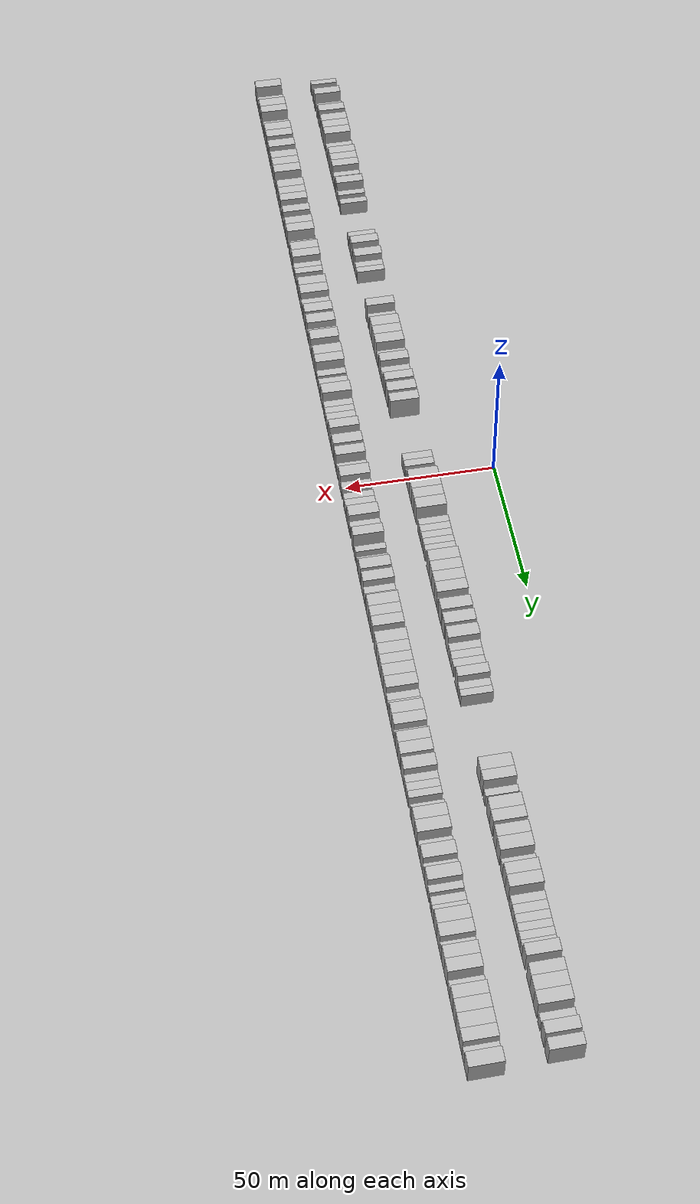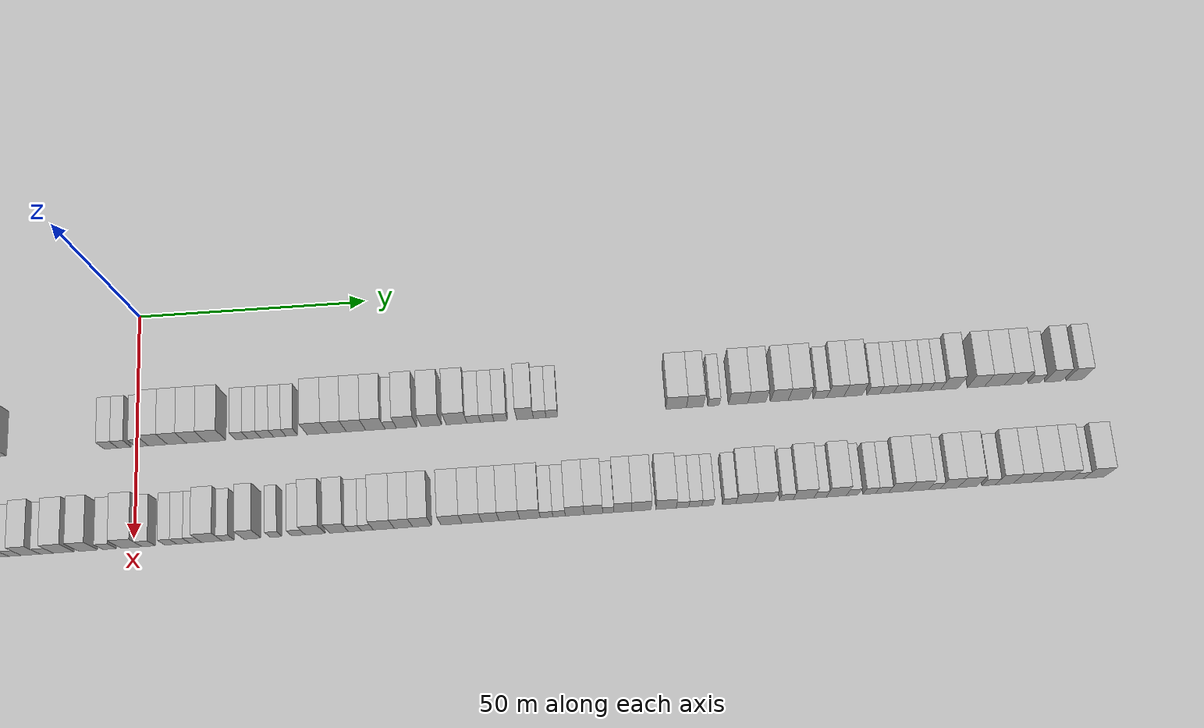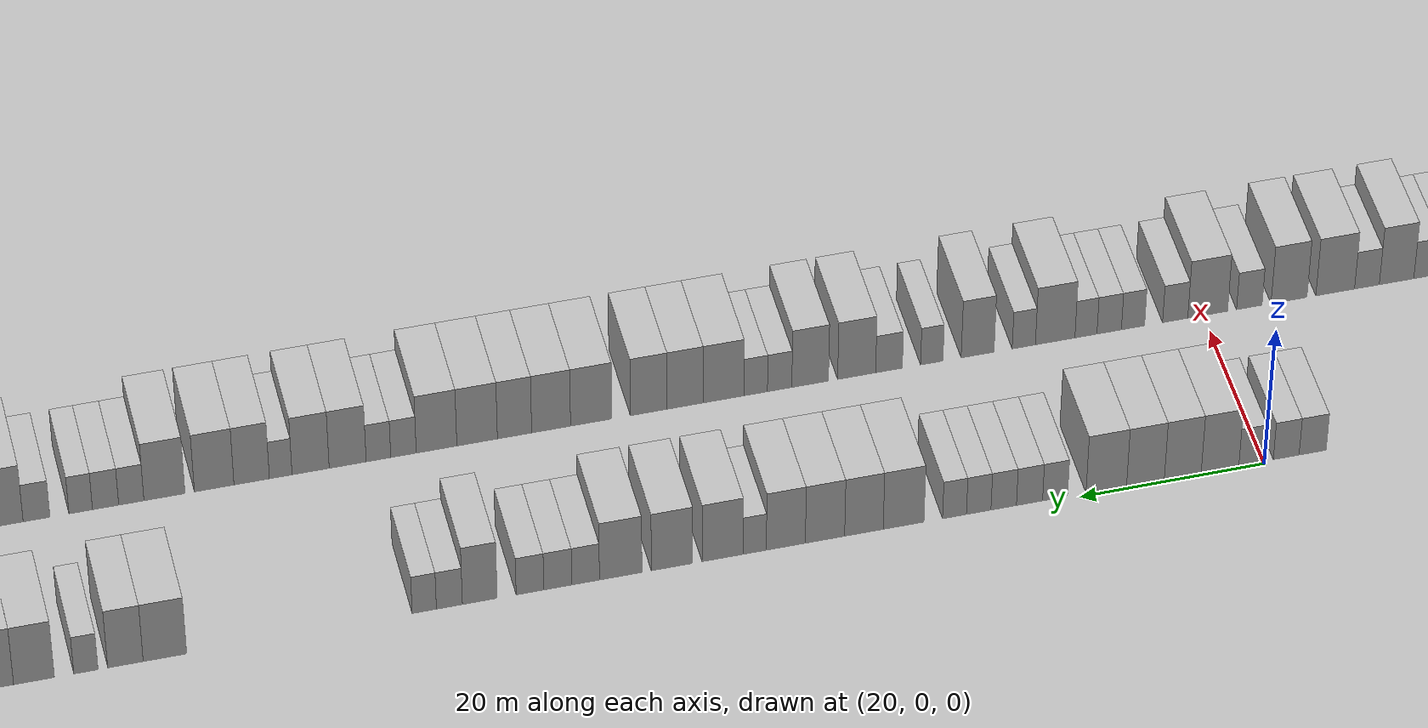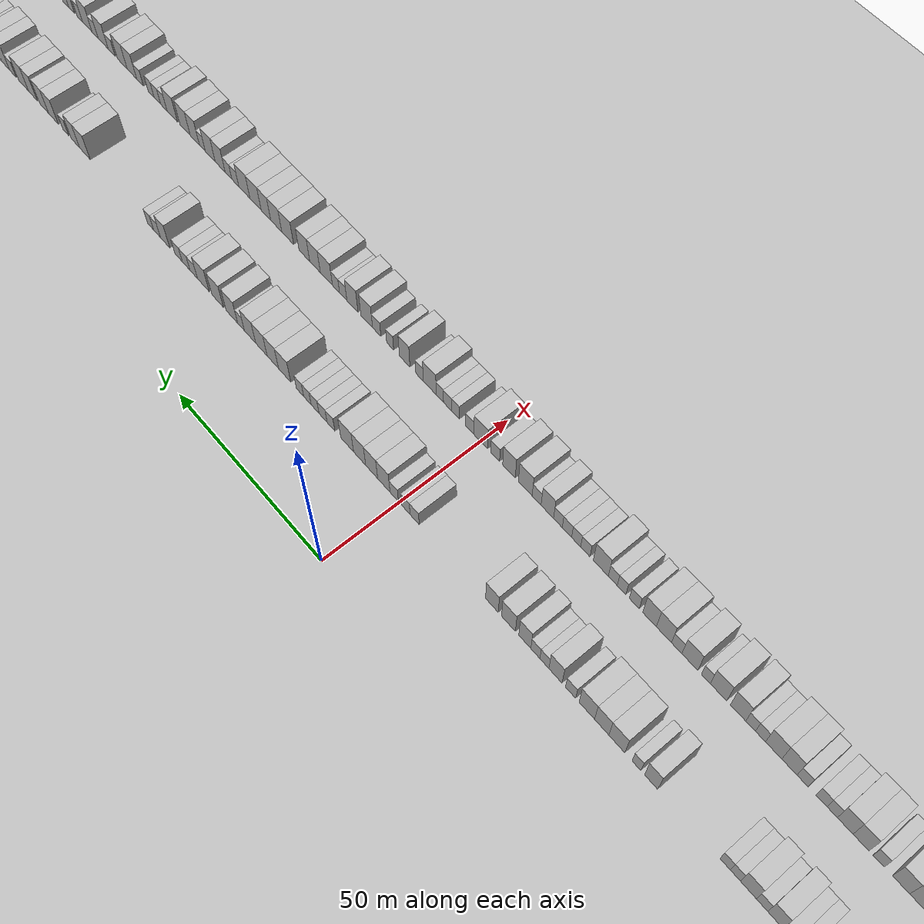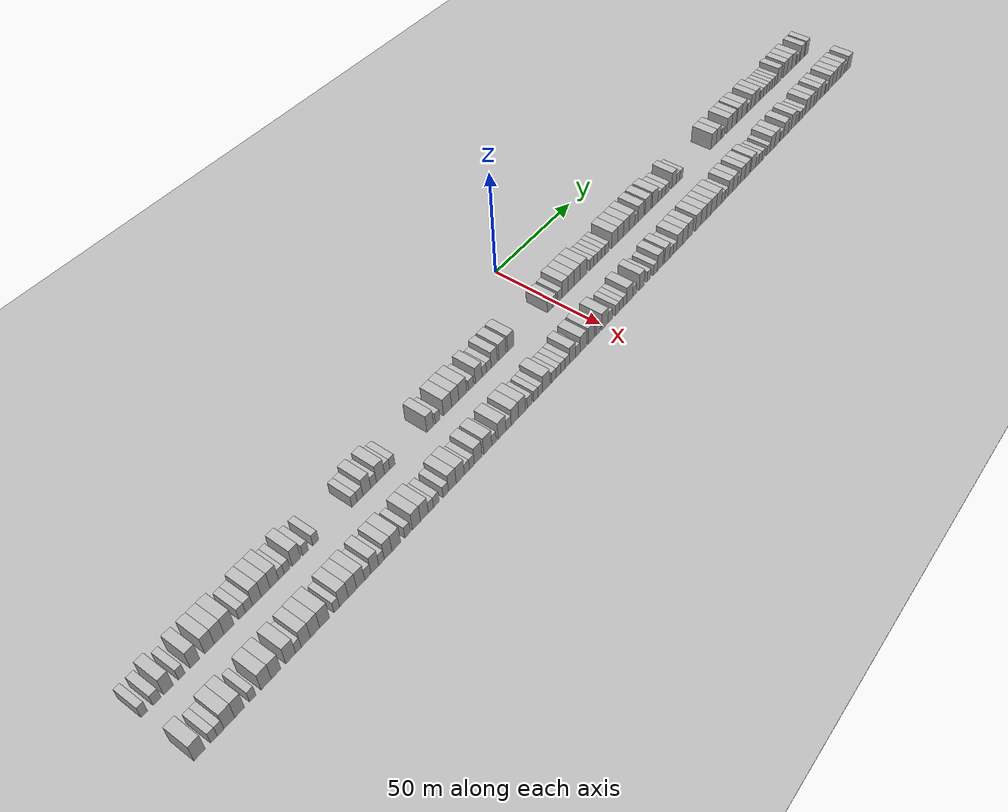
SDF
<?xml version="1.0" encoding="utf-8"?>

<sdf version="1.6">

   <world name="default">

      <gui fullscreen="0">

         <camera name="user_camera">

            <pose>-15 0 4.57585 0 0 0</pose>

            <view_controller>orbit</view_controller>

         </camera>

      </gui>

      <scene>

         <sky>

           <clouds>

             <speed>12</speed>

           </clouds>

         </sky>

         <ambient>0.4 0.4 0.4 1</ambient>

         <background>0.7 0.7 0.7 1</background>

         <shadows>1</shadows>

      </scene>

      <gravity>0 0 -9.8066</gravity>

      <magnetic_field>6e-06 2.3e-05 -4.2e-05</magnetic_field>

      <physics default="0" name="default_physics" type="ode">

         <ode>

            <solver>

               <type>quick</type>

               <iters>10</iters>

               <sor>1.0</sor>

               <use_dynamic_moi_rescaling>0</use_dynamic_moi_rescaling>

            </solver>

            <constraints>

               <cfm>0</cfm>

               <erp>0.2</erp>

               <contact_max_correcting_vel>100</contact_max_correcting_vel>

               <contact_surface_layer>0.001</contact_surface_layer>

            </constraints>

         </ode>

         <max_step_size>0.004</max_step_size>

         <real_time_factor>1</real_time_factor>

         <real_time_update_rate>250</real_time_update_rate>

      </physics>

      <light name="sun" type="directional">

         <cast_shadows>1</cast_shadows>

         <pose>0 0 10 0 0 0</pose>

         <diffuse>0.8 0.8 0.8 1</diffuse>

         <specular>0.2 0.2 0.2 1</specular>

         <attenuation>

            <range>1000</range>

            <constant>0.9</constant>

            <linear>0.01</linear>

            <quadratic>0.001</quadratic>

         </attenuation>

         <direction>-0.5 0.1 -0.9</direction>

      </light>

      <include>

         <name>ground_plane_1</name>

         <uri>model://HANNAS_ground_plane</uri>

         <pose>0 0 0  0 0 0</pose>

      </include>

      <include>

         <name>ground_plane_2</name>

         <uri>model://HANNAS_ground_plane</uri>

         <pose>100 0 0  0 0 0</pose>

      </include>

      <model name="building_1">

         <static>1</static>

         <pose frame="">25.0000 -202.7742 0 0.000000 0.000000 0.000000</pose>

         <link name="link">

            <pose frame="">0 0 3.00 0 0 0</pose>

            <collision name="collision">

               <geometry>

                  <box>

                     <size>10.0000 2.4517 6.0000</size>

                  </box>

               </geometry>

               <max_contacts>10</max_contacts>

               <surface>

                  <contact>

                     <ode/>

                  </contact>

                  <bounce/>

                  <friction>

                     <torsional>

                        <ode/>

                     </torsional>

                     <ode/>

                  </friction>

               </surface>

            </collision>

            <visual name="visual">

               <cast_shadows>0</cast_shadows>

               <geometry>

                  <box>

                     <size>10.0000 2.4517 6.0000</size>

                  </box>

               </geometry>

               <material>

                  <script>

                     <uri>model://HANNAS_wall/materials/scripts</uri>

                     <uri>model://HANNAS_wall/materials/textures</uri>

                     <name>vrc/HANNAS_wall</name>

                  </script>

               </material>

            </visual>

            <self_collide>0</self_collide>

            <enable_wind>0</enable_wind>

            <kinematic>0</kinematic>

         </link>

      </model>

      <model name="building_2">

         <static>1</static>

         <pose frame="">25.0000 -198.0626 0 0.000000 0.000000 0.000000</pose>

         <link name="link">

            <pose frame="">0 0 3.00 0 0 0</pose>

            <collision name="collision">

               <geometry>

                  <box>

                     <size>10.0000 2.9713 6.0000</size>

                  </box>

               </geometry>

               <max_contacts>10</max_contacts>

               <surface>

                  <contact>

                     <ode/>

                  </contact>

                  <bounce/>

                  <friction>

                     <torsional>

                        <ode/>

                     </torsional>

                     <ode/>

                  </friction>

               </surface>

            </collision>

            <visual name="visual">

               <cast_shadows>0</cast_shadows>

               <geometry>

                  <box>

                     <size>10.0000 2.9713 6.0000</size>

                  </box>

               </geometry>

               <material>

                  <script>

                     <uri>model://HANNAS_wall/materials/scripts</uri>

                     <uri>model://HANNAS_wall/materials/textures</uri>

                     <name>vrc/HANNAS_wall</name>

                  </script>

               </material>

            </visual>

            <self_collide>0</self_collide>

            <enable_wind>0</enable_wind>

            <kinematic>0</kinematic>

         </link>

      </model>

      <model name="building_3">

         <static>1</static>

         <pose frame="">25.0000 -193.7579 0 0.000000 0.000000 0.000000</pose>

         <link name="link">

            <pose frame="">0 0 4.50 0 0 0</pose>

            <collision name="collision">

               <geometry>

                  <box>

                     <size>10.0000 3.6382 9.0000</size>

                  </box>

               </geometry>

               <max_contacts>10</max_contacts>

               <surface>

                  <contact>

                     <ode/>

                  </contact>

                  <bounce/>

                  <friction>

                     <torsional>

                        <ode/>

                     </torsional>

                     <ode/>

                  </friction>

               </surface>

            </collision>

            <visual name="visual">

               <cast_shadows>0</cast_shadows>

               <geometry>

                  <box>

                     <size>10.0000 3.6382 9.0000</size>

                  </box>

               </geometry>

               <material>

                  <script>

                     <uri>model://HANNAS_wall/materials/scripts</uri>

                     <uri>model://HANNAS_wall/materials/textures</uri>

                     <name>vrc/HANNAS_wall</name>

                  </script>

               </material>

            </visual>

            <self_collide>0</self_collide>

            <enable_wind>0</enable_wind>

            <kinematic>0</kinematic>

         </link>

      </model>

      <model name="building_4">

         <static>1</static>

         <pose frame="">25.0000 -188.6675 0 0.000000 0.000000 0.000000</pose>

         <link name="link">

            <pose frame="">0 0 3.00 0 0 0</pose>

            <collision name="collision">

               <geometry>

                  <box>

                     <size>10.0000 2.5426 6.0000</size>

                  </box>

               </geometry>

               <max_contacts>10</max_contacts>

               <surface>

                  <contact>

                     <ode/>

                  </contact>

                  <bounce/>

                  <friction>

                     <torsional>

                        <ode/>

                     </torsional>

                     <ode/>

                  </friction>

               </surface>

            </collision>

            <visual name="visual">

               <cast_shadows>0</cast_shadows>

               <geometry>

                  <box>

                     <size>10.0000 2.5426 6.0000</size>

                  </box>

               </geometry>

               <material>

                  <script>

                     <uri>model://HANNAS_wall/materials/scripts</uri>

                     <uri>model://HANNAS_wall/materials/textures</uri>

                     <name>vrc/HANNAS_wall</name>

                  </script>

               </material>

            </visual>

            <self_collide>0</self_collide>

            <enable_wind>0</enable_wind>

            <kinematic>0</kinematic>

         </link>

      </model>

      <model name="building_5">

         <static>1</static>

         <pose frame="">25.0000 -183.5469 0 0.000000 0.000000 0.000000</pose>

         <link name="link">

            <pose frame="">0 0 4.50 0 0 0</pose>

            <collision name="collision">

               <geometry>

                  <box>

                     <size>10.0000 3.6987 9.0000</size>

                  </box>

               </geometry>

               <max_contacts>10</max_contacts>

               <surface>

                  <contact>

                     <ode/>

                  </contact>

                  <bounce/>

                  <friction>

                     <torsional>

                        <ode/>

                     </torsional>

                     <ode/>

                  </friction>

               </surface>

            </collision>

            <visual name="visual">

               <cast_shadows>0</cast_shadows>

               <geometry>

                  <box>

                     <size>10.0000 3.6987 9.0000</size>

                  </box>

               </geometry>

               <material>

                  <script>

                     <uri>model://HANNAS_wall/materials/scripts</uri>

                     <uri>model://HANNAS_wall/materials/textures</uri>

                     <name>vrc/HANNAS_wall</name>

                  </script>

               </material>

            </visual>

            <self_collide>0</self_collide>

            <enable_wind>0</enable_wind>

            <kinematic>0</kinematic>

         </link>

      </model>

      <model name="building_6">

         <static>1</static>

         <pose frame="">25.0000 -177.7807 0 0.000000 0.000000 0.000000</pose>

         <link name="link">

            <pose frame="">0 0 4.50 0 0 0</pose>

            <collision name="collision">

               <geometry>

                  <box>

                     <size>10.0000 3.8337 9.0000</size>

                  </box>

               </geometry>

               <max_contacts>10</max_contacts>

               <surface>

                  <contact>

                     <ode/>

                  </contact>

                  <bounce/>

                  <friction>

                     <torsional>

                        <ode/>

                     </torsional>

                     <ode/>

                  </friction>

               </surface>

            </collision>

            <visual name="visual">

               <cast_shadows>0</cast_shadows>

               <geometry>

                  <box>

                     <size>10.0000 3.8337 9.0000</size>

                  </box>

               </geometry>

               <material>

                  <script>

                     <uri>model://HANNAS_wall/materials/scripts</uri>

                     <uri>model://HANNAS_wall/materials/textures</uri>

                     <name>vrc/HANNAS_wall</name>

                  </script>

               </material>

            </visual>

            <self_collide>0</self_collide>

            <enable_wind>0</enable_wind>

            <kinematic>0</kinematic>

         </link>

      </model>

      <model name="building_7">

         <static>1</static>

         <pose frame="">25.0000 -173.8962 0 0.000000 0.000000 0.000000</pose>

         <link name="link">

            <pose frame="">0 0 4.50 0 0 0</pose>

            <collision name="collision">

               <geometry>

                  <box>

                     <size>10.0000 3.9352 9.0000</size>

                  </box>

               </geometry>

               <max_contacts>10</max_contacts>

               <surface>

                  <contact>

                     <ode/>

                  </contact>

                  <bounce/>

                  <friction>

                     <torsional>

                        <ode/>

                     </torsional>

                     <ode/>

                  </friction>

               </surface>

            </collision>

            <visual name="visual">

               <cast_shadows>0</cast_shadows>

               <geometry>

                  <box>

                     <size>10.0000 3.9352 9.0000</size>

                  </box>

               </geometry>

               <material>

                  <script>

                     <uri>model://HANNAS_wall/materials/scripts</uri>

                     <uri>model://HANNAS_wall/materials/textures</uri>

                     <name>vrc/HANNAS_wall</name>

                  </script>

               </material>

            </visual>

            <self_collide>0</self_collide>

            <enable_wind>0</enable_wind>

            <kinematic>0</kinematic>

         </link>

      </model>

      <model name="building_8">

         <static>1</static>

         <pose frame="">25.0000 -169.8892 0 0.000000 0.000000 0.000000</pose>

         <link name="link">

            <pose frame="">0 0 4.50 0 0 0</pose>

            <collision name="collision">

               <geometry>

                  <box>

                     <size>10.0000 4.0788 9.0000</size>

                  </box>

               </geometry>

               <max_contacts>10</max_contacts>

               <surface>

                  <contact>

                     <ode/>

                  </contact>

                  <bounce/>

                  <friction>

                     <torsional>

                        <ode/>

                     </torsional>

                     <ode/>

                  </friction>

               </surface>

            </collision>

            <visual name="visual">

               <cast_shadows>0</cast_shadows>

               <geometry>

                  <box>

                     <size>10.0000 4.0788 9.0000</size>

                  </box>

               </geometry>

               <material>

                  <script>

                     <uri>model://HANNAS_wall/materials/scripts</uri>

                     <uri>model://HANNAS_wall/materials/textures</uri>

                     <name>vrc/HANNAS_wall</name>

                  </script>

               </material>

            </visual>

            <self_collide>0</self_collide>

            <enable_wind>0</enable_wind>

            <kinematic>0</kinematic>

         </link>

      </model>

      <model name="building_9">

         <static>1</static>

         <pose frame="">25.0000 -164.4599 0 0.000000 0.000000 0.000000</pose>

         <link name="link">

            <pose frame="">0 0 3.00 0 0 0</pose>

            <collision name="collision">

               <geometry>

                  <box>

                     <size>10.0000 2.7798 6.0000</size>

                  </box>

               </geometry>

               <max_contacts>10</max_contacts>

               <surface>

                  <contact>

                     <ode/>

                  </contact>

                  <bounce/>

                  <friction>

                     <torsional>

                        <ode/>

                     </torsional>

                     <ode/>

                  </friction>

               </surface>

            </collision>

            <visual name="visual">

               <cast_shadows>0</cast_shadows>

               <geometry>

                  <box>

                     <size>10.0000 2.7798 6.0000</size>

                  </box>

               </geometry>

               <material>

                  <script>

                     <uri>model://HANNAS_wall/materials/scripts</uri>

                     <uri>model://HANNAS_wall/materials/textures</uri>

                     <name>vrc/HANNAS_wall</name>

                  </script>

               </material>

            </visual>

            <self_collide>0</self_collide>

            <enable_wind>0</enable_wind>

            <kinematic>0</kinematic>

         </link>

      </model>

      <model name="building_10">

         <static>1</static>

         <pose frame="">25.0000 -161.5999 0 0.000000 0.000000 0.000000</pose>

         <link name="link">

            <pose frame="">0 0 3.00 0 0 0</pose>

            <collision name="collision">

               <geometry>

                  <box>

                     <size>10.0000 2.9401 6.0000</size>

                  </box>

               </geometry>

               <max_contacts>10</max_contacts>

               <surface>

                  <contact>

                     <ode/>

                  </contact>

                  <bounce/>

                  <friction>

                     <torsional>

                        <ode/>

                     </torsional>

                     <ode/>

                  </friction>

               </surface>

            </collision>

            <visual name="visual">

               <cast_shadows>0</cast_shadows>

               <geometry>

                  <box>

                     <size>10.0000 2.9401 6.0000</size>

                  </box>

               </geometry>

               <material>

                  <script>

                     <uri>model://HANNAS_wall/materials/scripts</uri>

                     <uri>model://HANNAS_wall/materials/textures</uri>

                     <name>vrc/HANNAS_wall</name>

                  </script>

               </material>

            </visual>

            <self_collide>0</self_collide>

            <enable_wind>0</enable_wind>

            <kinematic>0</kinematic>

         </link>

      </model>

      <model name="building_11">

         <static>1</static>

         <pose frame="">25.0000 -158.2807 0 0.000000 0.000000 0.000000</pose>

         <link name="link">

            <pose frame="">0 0 4.50 0 0 0</pose>

            <collision name="collision">

               <geometry>

                  <box>

                     <size>10.0000 3.6983 9.0000</size>

                  </box>

               </geometry>

               <max_contacts>10</max_contacts>

               <surface>

                  <contact>

                     <ode/>

                  </contact>

                  <bounce/>

                  <friction>

                     <torsional>

                        <ode/>

                     </torsional>

                     <ode/>

                  </friction>

               </surface>

            </collision>

            <visual name="visual">

               <cast_shadows>0</cast_shadows>

               <geometry>

                  <box>

                     <size>10.0000 3.6983 9.0000</size>

                  </box>

               </geometry>

               <material>

                  <script>

                     <uri>model://HANNAS_wall/materials/scripts</uri>

                     <uri>model://HANNAS_wall/materials/textures</uri>

                     <name>vrc/HANNAS_wall</name>

                  </script>

               </material>

            </visual>

            <self_collide>0</self_collide>

            <enable_wind>0</enable_wind>

            <kinematic>0</kinematic>

         </link>

      </model>

      <model name="building_12">

         <static>1</static>

         <pose frame="">25.0000 -154.5642 0 0.000000 0.000000 0.000000</pose>

         <link name="link">

            <pose frame="">0 0 4.50 0 0 0</pose>

            <collision name="collision">

               <geometry>

                  <box>

                     <size>10.0000 3.7347 9.0000</size>

                  </box>

               </geometry>

               <max_contacts>10</max_contacts>

               <surface>

                  <contact>

                     <ode/>

                  </contact>

                  <bounce/>

                  <friction>

                     <torsional>

                        <ode/>

                     </torsional>

                     <ode/>

                  </friction>

               </surface>

            </collision>

            <visual name="visual">

               <cast_shadows>0</cast_shadows>

               <geometry>

                  <box>

                     <size>10.0000 3.7347 9.0000</size>

                  </box>

               </geometry>

               <material>

                  <script>

                     <uri>model://HANNAS_wall/materials/scripts</uri>

                     <uri>model://HANNAS_wall/materials/textures</uri>

                     <name>vrc/HANNAS_wall</name>

                  </script>

               </material>

            </visual>

            <self_collide>0</self_collide>

            <enable_wind>0</enable_wind>

            <kinematic>0</kinematic>

         </link>

      </model>

      <model name="building_13">

         <static>1</static>

         <pose frame="">25.0000 -150.8454 0 0.000000 0.000000 0.000000</pose>

         <link name="link">

            <pose frame="">0 0 4.50 0 0 0</pose>

            <collision name="collision">

               <geometry>

                  <box>

                     <size>10.0000 3.7028 9.0000</size>

                  </box>

               </geometry>

               <max_contacts>10</max_contacts>

               <surface>

                  <contact>

                     <ode/>

                  </contact>

                  <bounce/>

                  <friction>

                     <torsional>

                        <ode/>

                     </torsional>

                     <ode/>

                  </friction>

               </surface>

            </collision>

            <visual name="visual">

               <cast_shadows>0</cast_shadows>

               <geometry>

                  <box>

                     <size>10.0000 3.7028 9.0000</size>

                  </box>

               </geometry>

               <material>

                  <script>

                     <uri>model://HANNAS_wall/materials/scripts</uri>

                     <uri>model://HANNAS_wall/materials/textures</uri>

                     <name>vrc/HANNAS_wall</name>

                  </script>

               </material>

            </visual>

            <self_collide>0</self_collide>

            <enable_wind>0</enable_wind>

            <kinematic>0</kinematic>

         </link>

      </model>

      <model name="building_14">

         <static>1</static>

         <pose frame="">25.0000 -147.7914 0 0.000000 0.000000 0.000000</pose>

         <link name="link">

            <pose frame="">0 0 3.00 0 0 0</pose>

            <collision name="collision">

               <geometry>

                  <box>

                     <size>10.0000 2.4053 6.0000</size>

                  </box>

               </geometry>

               <max_contacts>10</max_contacts>

               <surface>

                  <contact>

                     <ode/>

                  </contact>

                  <bounce/>

                  <friction>

                     <torsional>

                        <ode/>

                     </torsional>

                     <ode/>

                  </friction>

               </surface>

            </collision>

            <visual name="visual">

               <cast_shadows>0</cast_shadows>

               <geometry>

                  <box>

                     <size>10.0000 2.4053 6.0000</size>

                  </box>

               </geometry>

               <material>

                  <script>

                     <uri>model://HANNAS_wall/materials/scripts</uri>

                     <uri>model://HANNAS_wall/materials/textures</uri>

                     <name>vrc/HANNAS_wall</name>

                  </script>

               </material>

            </visual>

            <self_collide>0</self_collide>

            <enable_wind>0</enable_wind>

            <kinematic>0</kinematic>

         </link>

      </model>

      <model name="building_15">

         <static>1</static>

         <pose frame="">25.0000 -145.2952 0 0.000000 0.000000 0.000000</pose>

         <link name="link">

            <pose frame="">0 0 3.00 0 0 0</pose>

            <collision name="collision">

               <geometry>

                  <box>

                     <size>10.0000 2.5870 6.0000</size>

                  </box>

               </geometry>

               <max_contacts>10</max_contacts>

               <surface>

                  <contact>

                     <ode/>

                  </contact>

                  <bounce/>

                  <friction>

                     <torsional>

                        <ode/>

                     </torsional>

                     <ode/>

                  </friction>

               </surface>

            </collision>

            <visual name="visual">

               <cast_shadows>0</cast_shadows>

               <geometry>

                  <box>

                     <size>10.0000 2.5870 6.0000</size>

                  </box>

               </geometry>

               <material>

                  <script>

                     <uri>model://HANNAS_wall/materials/scripts</uri>

                     <uri>model://HANNAS_wall/materials/textures</uri>

                     <name>vrc/HANNAS_wall</name>

                  </script>

               </material>

            </visual>

            <self_collide>0</self_collide>

            <enable_wind>0</enable_wind>

            <kinematic>0</kinematic>

         </link>

      </model>

      <model name="building_16">

         <static>1</static>

         <pose frame="">25.0000 -141.1525 0 0.000000 0.000000 0.000000</pose>

         <link name="link">

            <pose frame="">0 0 4.50 0 0 0</pose>

            <collision name="collision">

               <geometry>

                  <box>

                     <size>10.0000 3.6984 9.0000</size>

                  </box>

               </geometry>

               <max_contacts>10</max_contacts>

               <surface>

                  <contact>

                     <ode/>

                  </contact>

                  <bounce/>

                  <friction>

                     <torsional>

                        <ode/>

                     </torsional>

                     <ode/>

                  </friction>

               </surface>

            </collision>

            <visual name="visual">

               <cast_shadows>0</cast_shadows>

               <geometry>

                  <box>

                     <size>10.0000 3.6984 9.0000</size>

                  </box>

               </geometry>

               <material>

                  <script>

                     <uri>model://HANNAS_wall/materials/scripts</uri>

                     <uri>model://HANNAS_wall/materials/textures</uri>

                     <name>vrc/HANNAS_wall</name>

                  </script>

               </material>

            </visual>

            <self_collide>0</self_collide>

            <enable_wind>0</enable_wind>

            <kinematic>0</kinematic>

         </link>

      </model>

      <model name="building_17">

         <static>1</static>

         <pose frame="">25.0000 -137.0269 0 0.000000 0.000000 0.000000</pose>

         <link name="link">

            <pose frame="">0 0 3.00 0 0 0</pose>

            <collision name="collision">

               <geometry>

                  <box>

                     <size>10.0000 2.5526 6.0000</size>

                  </box>

               </geometry>

               <max_contacts>10</max_contacts>

               <surface>

                  <contact>

                     <ode/>

                  </contact>

                  <bounce/>

                  <friction>

                     <torsional>

                        <ode/>

                     </torsional>

                     <ode/>

                  </friction>

               </surface>

            </collision>

            <visual name="visual">

               <cast_shadows>0</cast_shadows>

               <geometry>

                  <box>

                     <size>10.0000 2.5526 6.0000</size>

                  </box>

               </geometry>

               <material>

                  <script>

                     <uri>model://HANNAS_wall/materials/scripts</uri>

                     <uri>model://HANNAS_wall/materials/textures</uri>

                     <name>vrc/HANNAS_wall</name>

                  </script>

               </material>

            </visual>

            <self_collide>0</self_collide>

            <enable_wind>0</enable_wind>

            <kinematic>0</kinematic>

         </link>

      </model>

      <model name="building_18">

         <static>1</static>

         <pose frame="">25.0000 -132.4183 0 0.000000 0.000000 0.000000</pose>

         <link name="link">

            <pose frame="">0 0 3.00 0 0 0</pose>

            <collision name="collision">

               <geometry>

                  <box>

                     <size>10.0000 2.6648 6.0000</size>

                  </box>

               </geometry>

               <max_contacts>10</max_contacts>

               <surface>

                  <contact>

                     <ode/>

                  </contact>

                  <bounce/>

                  <friction>

                     <torsional>

                        <ode/>

                     </torsional>

                     <ode/>

                  </friction>

               </surface>

            </collision>

            <visual name="visual">

               <cast_shadows>0</cast_shadows>

               <geometry>

                  <box>

                     <size>10.0000 2.6648 6.0000</size>

                  </box>

               </geometry>

               <material>

                  <script>

                     <uri>model://HANNAS_wall/materials/scripts</uri>

                     <uri>model://HANNAS_wall/materials/textures</uri>

                     <name>vrc/HANNAS_wall</name>

                  </script>

               </material>

            </visual>

            <self_collide>0</self_collide>

            <enable_wind>0</enable_wind>

            <kinematic>0</kinematic>

         </link>

      </model>

      <model name="building_19">

         <static>1</static>

         <pose frame="">25.0000 -114.2712 0 0.000000 0.000000 0.000000</pose>

         <link name="link">

            <pose frame="">0 0 3.00 0 0 0</pose>

            <collision name="collision">

               <geometry>

                  <box>

                     <size>10.0000 2.5431 6.0000</size>

                  </box>

               </geometry>

               <max_contacts>10</max_contacts>

               <surface>

                  <contact>

                     <ode/>

                  </contact>

                  <bounce/>

                  <friction>

                     <torsional>

                        <ode/>

                     </torsional>

                     <ode/>

                  </friction>

               </surface>

            </collision>

            <visual name="visual">

               <cast_shadows>0</cast_shadows>

               <geometry>

                  <box>

                     <size>10.0000 2.5431 6.0000</size>

                  </box>

               </geometry>

               <material>

                  <script>

                     <uri>model://HANNAS_wall/materials/scripts</uri>

                     <uri>model://HANNAS_wall/materials/textures</uri>

                     <name>vrc/HANNAS_wall</name>

                  </script>

               </material>

            </visual>

            <self_collide>0</self_collide>

            <enable_wind>0</enable_wind>

            <kinematic>0</kinematic>

         </link>

      </model>

      <model name="building_20">

         <static>1</static>

         <pose frame="">25.0000 -111.5728 0 0.000000 0.000000 0.000000</pose>

         <link name="link">

            <pose frame="">0 0 3.00 0 0 0</pose>

            <collision name="collision">

               <geometry>

                  <box>

                     <size>10.0000 2.8536 6.0000</size>

                  </box>

               </geometry>

               <max_contacts>10</max_contacts>

               <surface>

                  <contact>

                     <ode/>

                  </contact>

                  <bounce/>

                  <friction>

                     <torsional>

                        <ode/>

                     </torsional>

                     <ode/>

                  </friction>

               </surface>

            </collision>

            <visual name="visual">

               <cast_shadows>0</cast_shadows>

               <geometry>

                  <box>

                     <size>10.0000 2.8536 6.0000</size>

                  </box>

               </geometry>

               <material>

                  <script>

                     <uri>model://HANNAS_wall/materials/scripts</uri>

                     <uri>model://HANNAS_wall/materials/textures</uri>

                     <name>vrc/HANNAS_wall</name>

                  </script>

               </material>

            </visual>

            <self_collide>0</self_collide>

            <enable_wind>0</enable_wind>

            <kinematic>0</kinematic>

         </link>

      </model>

      <model name="building_21">

         <static>1</static>

         <pose frame="">25.0000 -108.2441 0 0.000000 0.000000 0.000000</pose>

         <link name="link">

            <pose frame="">0 0 4.50 0 0 0</pose>

            <collision name="collision">

               <geometry>

                  <box>

                     <size>10.0000 3.8039 9.0000</size>

                  </box>

               </geometry>

               <max_contacts>10</max_contacts>

               <surface>

                  <contact>

                     <ode/>

                  </contact>

                  <bounce/>

                  <friction>

                     <torsional>

                        <ode/>

                     </torsional>

                     <ode/>

                  </friction>

               </surface>

            </collision>

            <visual name="visual">

               <cast_shadows>0</cast_shadows>

               <geometry>

                  <box>

                     <size>10.0000 3.8039 9.0000</size>

                  </box>

               </geometry>

               <material>

                  <script>

                     <uri>model://HANNAS_wall/materials/scripts</uri>

                     <uri>model://HANNAS_wall/materials/textures</uri>

                     <name>vrc/HANNAS_wall</name>

                  </script>

               </material>

            </visual>

            <self_collide>0</self_collide>

            <enable_wind>0</enable_wind>

            <kinematic>0</kinematic>

         </link>

      </model>

      <model name="building_22">

         <static>1</static>

         <pose frame="">25.0000 -104.9059 0 0.000000 0.000000 0.000000</pose>

         <link name="link">

            <pose frame="">0 0 3.00 0 0 0</pose>

            <collision name="collision">

               <geometry>

                  <box>

                     <size>10.0000 2.8725 6.0000</size>

                  </box>

               </geometry>

               <max_contacts>10</max_contacts>

               <surface>

                  <contact>

                     <ode/>

                  </contact>

                  <bounce/>

                  <friction>

                     <torsional>

                        <ode/>

                     </torsional>

                     <ode/>

                  </friction>

               </surface>

            </collision>

            <visual name="visual">

               <cast_shadows>0</cast_shadows>

               <geometry>

                  <box>

                     <size>10.0000 2.8725 6.0000</size>

                  </box>

               </geometry>

               <material>

                  <script>

                     <uri>model://HANNAS_wall/materials/scripts</uri>

                     <uri>model://HANNAS_wall/materials/textures</uri>

                     <name>vrc/HANNAS_wall</name>

                  </script>

               </material>

            </visual>

            <self_collide>0</self_collide>

            <enable_wind>0</enable_wind>

            <kinematic>0</kinematic>

         </link>

      </model>

      <model name="building_23">

         <static>1</static>

         <pose frame="">25.0000 -101.4643 0 0.000000 0.000000 0.000000</pose>

         <link name="link">

            <pose frame="">0 0 4.50 0 0 0</pose>

            <collision name="collision">

               <geometry>

                  <box>

                     <size>10.0000 4.0108 9.0000</size>

                  </box>

               </geometry>

               <max_contacts>10</max_contacts>

               <surface>

                  <contact>

                     <ode/>

                  </contact>

                  <bounce/>

                  <friction>

                     <torsional>

                        <ode/>

                     </torsional>

                     <ode/>

                  </friction>

               </surface>

            </collision>

            <visual name="visual">

               <cast_shadows>0</cast_shadows>

               <geometry>

                  <box>

                     <size>10.0000 4.0108 9.0000</size>

                  </box>

               </geometry>

               <material>

                  <script>

                     <uri>model://HANNAS_wall/materials/scripts</uri>

                     <uri>model://HANNAS_wall/materials/textures</uri>

                     <name>vrc/HANNAS_wall</name>

                  </script>

               </material>

            </visual>

            <self_collide>0</self_collide>

            <enable_wind>0</enable_wind>

            <kinematic>0</kinematic>

         </link>

      </model>

      <model name="building_24">

         <static>1</static>

         <pose frame="">25.0000 -98.1248 0 0.000000 0.000000 0.000000</pose>

         <link name="link">

            <pose frame="">0 0 3.00 0 0 0</pose>

            <collision name="collision">

               <geometry>

                  <box>

                     <size>10.0000 2.6683 6.0000</size>

                  </box>

               </geometry>

               <max_contacts>10</max_contacts>

               <surface>

                  <contact>

                     <ode/>

                  </contact>

                  <bounce/>

                  <friction>

                     <torsional>

                        <ode/>

                     </torsional>

                     <ode/>

                  </friction>

               </surface>

            </collision>

            <visual name="visual">

               <cast_shadows>0</cast_shadows>

               <geometry>

                  <box>

                     <size>10.0000 2.6683 6.0000</size>

                  </box>

               </geometry>

               <material>

                  <script>

                     <uri>model://HANNAS_wall/materials/scripts</uri>

                     <uri>model://HANNAS_wall/materials/textures</uri>

                     <name>vrc/HANNAS_wall</name>

                  </script>

               </material>

            </visual>

            <self_collide>0</self_collide>

            <enable_wind>0</enable_wind>

            <kinematic>0</kinematic>

         </link>

      </model>

      <model name="building_25">

         <static>1</static>

         <pose frame="">25.0000 -95.4521 0 0.000000 0.000000 0.000000</pose>

         <link name="link">

            <pose frame="">0 0 3.00 0 0 0</pose>

            <collision name="collision">

               <geometry>

                  <box>

                     <size>10.0000 2.6770 6.0000</size>

                  </box>

               </geometry>

               <max_contacts>10</max_contacts>

               <surface>

                  <contact>

                     <ode/>

                  </contact>

                  <bounce/>

                  <friction>

                     <torsional>

                        <ode/>

                     </torsional>

                     <ode/>

                  </friction>

               </surface>

            </collision>

            <visual name="visual">

               <cast_shadows>0</cast_shadows>

               <geometry>

                  <box>

                     <size>10.0000 2.6770 6.0000</size>

                  </box>

               </geometry>

               <material>

                  <script>

                     <uri>model://HANNAS_wall/materials/scripts</uri>

                     <uri>model://HANNAS_wall/materials/textures</uri>

                     <name>vrc/HANNAS_wall</name>

                  </script>

               </material>

            </visual>

            <self_collide>0</self_collide>

            <enable_wind>0</enable_wind>

            <kinematic>0</kinematic>

         </link>

      </model>

      <model name="building_26">

         <static>1</static>

         <pose frame="">25.0000 -75.6816 0 0.000000 0.000000 0.000000</pose>

         <link name="link">

            <pose frame="">0 0 4.50 0 0 0</pose>

            <collision name="collision">

               <geometry>

                  <box>

                     <size>10.0000 3.6213 9.0000</size>

                  </box>

               </geometry>

               <max_contacts>10</max_contacts>

               <surface>

                  <contact>

                     <ode/>

                  </contact>

                  <bounce/>

                  <friction>

                     <torsional>

                        <ode/>

                     </torsional>

                     <ode/>

                  </friction>

               </surface>

            </collision>

            <visual name="visual">

               <cast_shadows>0</cast_shadows>

               <geometry>

                  <box>

                     <size>10.0000 3.6213 9.0000</size>

                  </box>

               </geometry>

               <material>

                  <script>

                     <uri>model://HANNAS_wall/materials/scripts</uri>

                     <uri>model://HANNAS_wall/materials/textures</uri>

                     <name>vrc/HANNAS_wall</name>

                  </script>

               </material>

            </visual>

            <self_collide>0</self_collide>

            <enable_wind>0</enable_wind>

            <kinematic>0</kinematic>

         </link>

      </model>

      <model name="building_27">

         <static>1</static>

         <pose frame="">25.0000 -71.6547 0 0.000000 0.000000 0.000000</pose>

         <link name="link">

            <pose frame="">0 0 3.00 0 0 0</pose>

            <collision name="collision">

               <geometry>

                  <box>

                     <size>10.0000 2.4325 6.0000</size>

                  </box>

               </geometry>

               <max_contacts>10</max_contacts>

               <surface>

                  <contact>

                     <ode/>

                  </contact>

                  <bounce/>

                  <friction>

                     <torsional>

                        <ode/>

                     </torsional>

                     <ode/>

                  </friction>

               </surface>

            </collision>

            <visual name="visual">

               <cast_shadows>0</cast_shadows>

               <geometry>

                  <box>

                     <size>10.0000 2.4325 6.0000</size>

                  </box>

               </geometry>

               <material>

                  <script>

                     <uri>model://HANNAS_wall/materials/scripts</uri>

                     <uri>model://HANNAS_wall/materials/textures</uri>

                     <name>vrc/HANNAS_wall</name>

                  </script>

               </material>

            </visual>

            <self_collide>0</self_collide>

            <enable_wind>0</enable_wind>

            <kinematic>0</kinematic>

         </link>

      </model>

      <model name="building_28">

         <static>1</static>

         <pose frame="">25.0000 -66.1913 0 0.000000 0.000000 0.000000</pose>

         <link name="link">

            <pose frame="">0 0 4.50 0 0 0</pose>

            <collision name="collision">

               <geometry>

                  <box>

                     <size>10.0000 4.4942 9.0000</size>

                  </box>

               </geometry>

               <max_contacts>10</max_contacts>

               <surface>

                  <contact>

                     <ode/>

                  </contact>

                  <bounce/>

                  <friction>

                     <torsional>

                        <ode/>

                     </torsional>

                     <ode/>

                  </friction>

               </surface>

            </collision>

            <visual name="visual">

               <cast_shadows>0</cast_shadows>

               <geometry>

                  <box>

                     <size>10.0000 4.4942 9.0000</size>

                  </box>

               </geometry>

               <material>

                  <script>

                     <uri>model://HANNAS_wall/materials/scripts</uri>

                     <uri>model://HANNAS_wall/materials/textures</uri>

                     <name>vrc/HANNAS_wall</name>

                  </script>

               </material>

            </visual>

            <self_collide>0</self_collide>

            <enable_wind>0</enable_wind>

            <kinematic>0</kinematic>

         </link>

      </model>

      <model name="building_29">

         <static>1</static>

         <pose frame="">25.0000 -61.9204 0 0.000000 0.000000 0.000000</pose>

         <link name="link">

            <pose frame="">0 0 4.50 0 0 0</pose>

            <collision name="collision">

               <geometry>

                  <box>

                     <size>10.0000 4.0477 9.0000</size>

                  </box>

               </geometry>

               <max_contacts>10</max_contacts>

               <surface>

                  <contact>

                     <ode/>

                  </contact>

                  <bounce/>

                  <friction>

                     <torsional>

                        <ode/>

                     </torsional>

                     <ode/>

                  </friction>

               </surface>

            </collision>

            <visual name="visual">

               <cast_shadows>0</cast_shadows>

               <geometry>

                  <box>

                     <size>10.0000 4.0477 9.0000</size>

                  </box>

               </geometry>

               <material>

                  <script>

                     <uri>model://HANNAS_wall/materials/scripts</uri>

                     <uri>model://HANNAS_wall/materials/textures</uri>

                     <name>vrc/HANNAS_wall</name>

                  </script>

               </material>

            </visual>

            <self_collide>0</self_collide>

            <enable_wind>0</enable_wind>

            <kinematic>0</kinematic>

         </link>

      </model>

      <model name="building_30">

         <static>1</static>

         <pose frame="">25.0000 -57.6876 0 0.000000 0.000000 0.000000</pose>

         <link name="link">

            <pose frame="">0 0 4.50 0 0 0</pose>

            <collision name="collision">

               <geometry>

                  <box>

                     <size>10.0000 4.4179 9.0000</size>

                  </box>

               </geometry>

               <max_contacts>10</max_contacts>

               <surface>

                  <contact>

                     <ode/>

                  </contact>

                  <bounce/>

                  <friction>

                     <torsional>

                        <ode/>

                     </torsional>

                     <ode/>

                  </friction>

               </surface>

            </collision>

            <visual name="visual">

               <cast_shadows>0</cast_shadows>

               <geometry>

                  <box>

                     <size>10.0000 4.4179 9.0000</size>

                  </box>

               </geometry>

               <material>

                  <script>

                     <uri>model://HANNAS_wall/materials/scripts</uri>

                     <uri>model://HANNAS_wall/materials/textures</uri>

                     <name>vrc/HANNAS_wall</name>

                  </script>

               </material>

            </visual>

            <self_collide>0</self_collide>

            <enable_wind>0</enable_wind>

            <kinematic>0</kinematic>

         </link>

      </model>

      <model name="building_31">

         <static>1</static>

         <pose frame="">25.0000 -53.0100 0 0.000000 0.000000 0.000000</pose>

         <link name="link">

            <pose frame="">0 0 3.00 0 0 0</pose>

            <collision name="collision">

               <geometry>

                  <box>

                     <size>10.0000 2.9374 6.0000</size>

                  </box>

               </geometry>

               <max_contacts>10</max_contacts>

               <surface>

                  <contact>

                     <ode/>

                  </contact>

                  <bounce/>

                  <friction>

                     <torsional>

                        <ode/>

                     </torsional>

                     <ode/>

                  </friction>

               </surface>

            </collision>

            <visual name="visual">

               <cast_shadows>0</cast_shadows>

               <geometry>

                  <box>

                     <size>10.0000 2.9374 6.0000</size>

                  </box>

               </geometry>

               <material>

                  <script>

                     <uri>model://HANNAS_wall/materials/scripts</uri>

                     <uri>model://HANNAS_wall/materials/textures</uri>

                     <name>vrc/HANNAS_wall</name>

                  </script>

               </material>

            </visual>

            <self_collide>0</self_collide>

            <enable_wind>0</enable_wind>

            <kinematic>0</kinematic>

         </link>

      </model>

      <model name="building_32">

         <static>1</static>

         <pose frame="">25.0000 -48.6133 0 0.000000 0.000000 0.000000</pose>

         <link name="link">

            <pose frame="">0 0 4.50 0 0 0</pose>

            <collision name="collision">

               <geometry>

                  <box>

                     <size>10.0000 3.8559 9.0000</size>

                  </box>

               </geometry>

               <max_contacts>10</max_contacts>

               <surface>

                  <contact>

                     <ode/>

                  </contact>

                  <bounce/>

                  <friction>

                     <torsional>

                        <ode/>

                     </torsional>

                     <ode/>

                  </friction>

               </surface>

            </collision>

            <visual name="visual">

               <cast_shadows>0</cast_shadows>

               <geometry>

                  <box>

                     <size>10.0000 3.8559 9.0000</size>

                  </box>

               </geometry>

               <material>

                  <script>

                     <uri>model://HANNAS_wall/materials/scripts</uri>

                     <uri>model://HANNAS_wall/materials/textures</uri>

                     <name>vrc/HANNAS_wall</name>

                  </script>

               </material>

            </visual>

            <self_collide>0</self_collide>

            <enable_wind>0</enable_wind>

            <kinematic>0</kinematic>

         </link>

      </model>

      <model name="building_33">

         <static>1</static>

         <pose frame="">25.0000 -45.3594 0 0.000000 0.000000 0.000000</pose>

         <link name="link">

            <pose frame="">0 0 3.00 0 0 0</pose>

            <collision name="collision">

               <geometry>

                  <box>

                     <size>10.0000 2.6521 6.0000</size>

                  </box>

               </geometry>

               <max_contacts>10</max_contacts>

               <surface>

                  <contact>

                     <ode/>

                  </contact>

                  <bounce/>

                  <friction>

                     <torsional>

                        <ode/>

                     </torsional>

                     <ode/>

                  </friction>

               </surface>

            </collision>

            <visual name="visual">

               <cast_shadows>0</cast_shadows>

               <geometry>

                  <box>

                     <size>10.0000 2.6521 6.0000</size>

                  </box>

               </geometry>

               <material>

                  <script>

                     <uri>model://HANNAS_wall/materials/scripts</uri>

                     <uri>model://HANNAS_wall/materials/textures</uri>

                     <name>vrc/HANNAS_wall</name>

                  </script>

               </material>

            </visual>

            <self_collide>0</self_collide>

            <enable_wind>0</enable_wind>

            <kinematic>0</kinematic>

         </link>

      </model>

      <model name="building_34">

         <static>1</static>

         <pose frame="">25.0000 -42.6899 0 0.000000 0.000000 0.000000</pose>

         <link name="link">

            <pose frame="">0 0 3.00 0 0 0</pose>

            <collision name="collision">

               <geometry>

                  <box>

                     <size>10.0000 2.6868 6.0000</size>

                  </box>

               </geometry>

               <max_contacts>10</max_contacts>

               <surface>

                  <contact>

                     <ode/>

                  </contact>

                  <bounce/>

                  <friction>

                     <torsional>

                        <ode/>

                     </torsional>

                     <ode/>

                  </friction>

               </surface>

            </collision>

            <visual name="visual">

               <cast_shadows>0</cast_shadows>

               <geometry>

                  <box>

                     <size>10.0000 2.6868 6.0000</size>

                  </box>

               </geometry>

               <material>

                  <script>

                     <uri>model://HANNAS_wall/materials/scripts</uri>

                     <uri>model://HANNAS_wall/materials/textures</uri>

                     <name>vrc/HANNAS_wall</name>

                  </script>

               </material>

            </visual>

            <self_collide>0</self_collide>

            <enable_wind>0</enable_wind>

            <kinematic>0</kinematic>

         </link>

      </model>

      <model name="building_35">

         <static>1</static>

         <pose frame="">25.0000 -39.5424 0 0.000000 0.000000 0.000000</pose>

         <link name="link">

            <pose frame="">0 0 4.50 0 0 0</pose>

            <collision name="collision">

               <geometry>

                  <box>

                     <size>10.0000 3.6082 9.0000</size>

                  </box>

               </geometry>

               <max_contacts>10</max_contacts>

               <surface>

                  <contact>

                     <ode/>

                  </contact>

                  <bounce/>

                  <friction>

                     <torsional>

                        <ode/>

                     </torsional>

                     <ode/>

                  </friction>

               </surface>

            </collision>

            <visual name="visual">

               <cast_shadows>0</cast_shadows>

               <geometry>

                  <box>

                     <size>10.0000 3.6082 9.0000</size>

                  </box>

               </geometry>

               <material>

                  <script>

                     <uri>model://HANNAS_wall/materials/scripts</uri>

                     <uri>model://HANNAS_wall/materials/textures</uri>

                     <name>vrc/HANNAS_wall</name>

                  </script>

               </material>

            </visual>

            <self_collide>0</self_collide>

            <enable_wind>0</enable_wind>

            <kinematic>0</kinematic>

         </link>

      </model>

      <model name="building_36">

         <static>1</static>

         <pose frame="">25.0000 -34.6428 0 0.000000 0.000000 0.000000</pose>

         <link name="link">

            <pose frame="">0 0 4.50 0 0 0</pose>

            <collision name="collision">

               <geometry>

                  <box>

                     <size>10.0000 4.1911 9.0000</size>

                  </box>

               </geometry>

               <max_contacts>10</max_contacts>

               <surface>

                  <contact>

                     <ode/>

                  </contact>

                  <bounce/>

                  <friction>

                     <torsional>

                        <ode/>

                     </torsional>

                     <ode/>

                  </friction>

               </surface>

            </collision>

            <visual name="visual">

               <cast_shadows>0</cast_shadows>

               <geometry>

                  <box>

                     <size>10.0000 4.1911 9.0000</size>

                  </box>

               </geometry>

               <material>

                  <script>

                     <uri>model://HANNAS_wall/materials/scripts</uri>

                     <uri>model://HANNAS_wall/materials/textures</uri>

                     <name>vrc/HANNAS_wall</name>

                  </script>

               </material>

            </visual>

            <self_collide>0</self_collide>

            <enable_wind>0</enable_wind>

            <kinematic>0</kinematic>

         </link>

      </model>

      <model name="building_37">

         <static>1</static>

         <pose frame="">25.0000 -29.5987 0 0.000000 0.000000 0.000000</pose>

         <link name="link">

            <pose frame="">0 0 4.50 0 0 0</pose>

            <collision name="collision">

               <geometry>

                  <box>

                     <size>10.0000 3.8973 9.0000</size>

                  </box>

               </geometry>

               <max_contacts>10</max_contacts>

               <surface>

                  <contact>

                     <ode/>

                  </contact>

                  <bounce/>

                  <friction>

                     <torsional>

                        <ode/>

                     </torsional>

                     <ode/>

                  </friction>

               </surface>

            </collision>

            <visual name="visual">

               <cast_shadows>0</cast_shadows>

               <geometry>

                  <box>

                     <size>10.0000 3.8973 9.0000</size>

                  </box>

               </geometry>

               <material>

                  <script>

                     <uri>model://HANNAS_wall/materials/scripts</uri>

                     <uri>model://HANNAS_wall/materials/textures</uri>

                     <name>vrc/HANNAS_wall</name>

                  </script>

               </material>

            </visual>

            <self_collide>0</self_collide>

            <enable_wind>0</enable_wind>

            <kinematic>0</kinematic>

         </link>

      </model>

      <model name="building_38">

         <static>1</static>

         <pose frame="">25.0000 -5.2154 0 0.000000 0.000000 0.000000</pose>

         <link name="link">

            <pose frame="">0 0 3.00 0 0 0</pose>

            <collision name="collision">

               <geometry>

                  <box>

                     <size>10.0000 2.9564 6.0000</size>

                  </box>

               </geometry>

               <max_contacts>10</max_contacts>

               <surface>

                  <contact>

                     <ode/>

                  </contact>

                  <bounce/>

                  <friction>

                     <torsional>

                        <ode/>

                     </torsional>

                     <ode/>

                  </friction>

               </surface>

            </collision>

            <visual name="visual">

               <cast_shadows>0</cast_shadows>

               <geometry>

                  <box>

                     <size>10.0000 2.9564 6.0000</size>

                  </box>

               </geometry>

               <material>

                  <script>

                     <uri>model://HANNAS_wall/materials/scripts</uri>

                     <uri>model://HANNAS_wall/materials/textures</uri>

                     <name>vrc/HANNAS_wall</name>

                  </script>

               </material>

            </visual>

            <self_collide>0</self_collide>

            <enable_wind>0</enable_wind>

            <kinematic>0</kinematic>

         </link>

      </model>

      <model name="building_39">

         <static>1</static>

         <pose frame="">25.0000 -2.3277 0 0.000000 0.000000 0.000000</pose>

         <link name="link">

            <pose frame="">0 0 3.00 0 0 0</pose>

            <collision name="collision">

               <geometry>

                  <box>

                     <size>10.0000 2.8189 6.0000</size>

                  </box>

               </geometry>

               <max_contacts>10</max_contacts>

               <surface>

                  <contact>

                     <ode/>

                  </contact>

                  <bounce/>

                  <friction>

                     <torsional>

                        <ode/>

                     </torsional>

                     <ode/>

                  </friction>

               </surface>

            </collision>

            <visual name="visual">

               <cast_shadows>0</cast_shadows>

               <geometry>

                  <box>

                     <size>10.0000 2.8189 6.0000</size>

                  </box>

               </geometry>

               <material>

                  <script>

                     <uri>model://HANNAS_wall/materials/scripts</uri>

                     <uri>model://HANNAS_wall/materials/textures</uri>

                     <name>vrc/HANNAS_wall</name>

                  </script>

               </material>

            </visual>

            <self_collide>0</self_collide>

            <enable_wind>0</enable_wind>

            <kinematic>0</kinematic>

         </link>

      </model>

      <model name="building_40">

         <static>1</static>

         <pose frame="">25.0000 1.4617 0 0.000000 0.000000 0.000000</pose>

         <link name="link">

            <pose frame="">0 0 3.00 0 0 0</pose>

            <collision name="collision">

               <geometry>

                  <box>

                     <size>10.0000 2.7599 6.0000</size>

                  </box>

               </geometry>

               <max_contacts>10</max_contacts>

               <surface>

                  <contact>

                     <ode/>

                  </contact>

                  <bounce/>

                  <friction>

                     <torsional>

                        <ode/>

                     </torsional>

                     <ode/>

                  </friction>

               </surface>

            </collision>

            <visual name="visual">

               <cast_shadows>0</cast_shadows>

               <geometry>

                  <box>

                     <size>10.0000 2.7599 6.0000</size>

                  </box>

               </geometry>

               <material>

                  <script>

                     <uri>model://HANNAS_wall/materials/scripts</uri>

                     <uri>model://HANNAS_wall/materials/textures</uri>

                     <name>vrc/HANNAS_wall</name>

                  </script>

               </material>

            </visual>

            <self_collide>0</self_collide>

            <enable_wind>0</enable_wind>

            <kinematic>0</kinematic>

         </link>

      </model>

      <model name="building_41">

         <static>1</static>

         <pose frame="">25.0000 4.8905 0 0.000000 0.000000 0.000000</pose>

         <link name="link">

            <pose frame="">0 0 4.50 0 0 0</pose>

            <collision name="collision">

               <geometry>

                  <box>

                     <size>10.0000 4.0977 9.0000</size>

                  </box>

               </geometry>

               <max_contacts>10</max_contacts>

               <surface>

                  <contact>

                     <ode/>

                  </contact>

                  <bounce/>

                  <friction>

                     <torsional>

                        <ode/>

                     </torsional>

                     <ode/>

                  </friction>

               </surface>

            </collision>

            <visual name="visual">

               <cast_shadows>0</cast_shadows>

               <geometry>

                  <box>

                     <size>10.0000 4.0977 9.0000</size>

                  </box>

               </geometry>

               <material>

                  <script>

                     <uri>model://HANNAS_wall/materials/scripts</uri>

                     <uri>model://HANNAS_wall/materials/textures</uri>

                     <name>vrc/HANNAS_wall</name>

                  </script>

               </material>

            </visual>

            <self_collide>0</self_collide>

            <enable_wind>0</enable_wind>

            <kinematic>0</kinematic>

         </link>

      </model>

      <model name="building_42">

         <static>1</static>

         <pose frame="">25.0000 8.9445 0 0.000000 0.000000 0.000000</pose>

         <link name="link">

            <pose frame="">0 0 4.50 0 0 0</pose>

            <collision name="collision">

               <geometry>

                  <box>

                     <size>10.0000 4.0104 9.0000</size>

                  </box>

               </geometry>

               <max_contacts>10</max_contacts>

               <surface>

                  <contact>

                     <ode/>

                  </contact>

                  <bounce/>

                  <friction>

                     <torsional>

                        <ode/>

                     </torsional>

                     <ode/>

                  </friction>

               </surface>

            </collision>

            <visual name="visual">

               <cast_shadows>0</cast_shadows>

               <geometry>

                  <box>

                     <size>10.0000 4.0104 9.0000</size>

                  </box>

               </geometry>

               <material>

                  <script>

                     <uri>model://HANNAS_wall/materials/scripts</uri>

                     <uri>model://HANNAS_wall/materials/textures</uri>

                     <name>vrc/HANNAS_wall</name>

                  </script>

               </material>

            </visual>

            <self_collide>0</self_collide>

            <enable_wind>0</enable_wind>

            <kinematic>0</kinematic>

         </link>

      </model>

      <model name="building_43">

         <static>1</static>

         <pose frame="">25.0000 12.9975 0 0.000000 0.000000 0.000000</pose>

         <link name="link">

            <pose frame="">0 0 4.50 0 0 0</pose>

            <collision name="collision">

               <geometry>

                  <box>

                     <size>10.0000 4.0955 9.0000</size>

                  </box>

               </geometry>

               <max_contacts>10</max_contacts>

               <surface>

                  <contact>

                     <ode/>

                  </contact>

                  <bounce/>

                  <friction>

                     <torsional>

                        <ode/>

                     </torsional>

                     <ode/>

                  </friction>

               </surface>

            </collision>

            <visual name="visual">

               <cast_shadows>0</cast_shadows>

               <geometry>

                  <box>

                     <size>10.0000 4.0955 9.0000</size>

                  </box>

               </geometry>

               <material>

                  <script>

                     <uri>model://HANNAS_wall/materials/scripts</uri>

                     <uri>model://HANNAS_wall/materials/textures</uri>

                     <name>vrc/HANNAS_wall</name>

                  </script>

               </material>

            </visual>

            <self_collide>0</self_collide>

            <enable_wind>0</enable_wind>

            <kinematic>0</kinematic>

         </link>

      </model>

      <model name="building_44">

         <static>1</static>

         <pose frame="">25.0000 17.2449 0 0.000000 0.000000 0.000000</pose>

         <link name="link">

            <pose frame="">0 0 4.50 0 0 0</pose>

            <collision name="collision">

               <geometry>

                  <box>

                     <size>10.0000 4.3993 9.0000</size>

                  </box>

               </geometry>

               <max_contacts>10</max_contacts>

               <surface>

                  <contact>

                     <ode/>

                  </contact>

                  <bounce/>

                  <friction>

                     <torsional>

                        <ode/>

                     </torsional>

                     <ode/>

                  </friction>

               </surface>

            </collision>

            <visual name="visual">

               <cast_shadows>0</cast_shadows>

               <geometry>

                  <box>

                     <size>10.0000 4.3993 9.0000</size>

                  </box>

               </geometry>

               <material>

                  <script>

                     <uri>model://HANNAS_wall/materials/scripts</uri>

                     <uri>model://HANNAS_wall/materials/textures</uri>

                     <name>vrc/HANNAS_wall</name>

                  </script>

               </material>

            </visual>

            <self_collide>0</self_collide>

            <enable_wind>0</enable_wind>

            <kinematic>0</kinematic>

         </link>

      </model>

      <model name="building_45">

         <static>1</static>

         <pose frame="">25.0000 22.7931 0 0.000000 0.000000 0.000000</pose>

         <link name="link">

            <pose frame="">0 0 3.00 0 0 0</pose>

            <collision name="collision">

               <geometry>

                  <box>

                     <size>10.0000 2.6971 6.0000</size>

                  </box>

               </geometry>

               <max_contacts>10</max_contacts>

               <surface>

                  <contact>

                     <ode/>

                  </contact>

                  <bounce/>

                  <friction>

                     <torsional>

                        <ode/>

                     </torsional>

                     <ode/>

                  </friction>

               </surface>

            </collision>

            <visual name="visual">

               <cast_shadows>0</cast_shadows>

               <geometry>

                  <box>

                     <size>10.0000 2.6971 6.0000</size>

                  </box>

               </geometry>

               <material>

                  <script>

                     <uri>model://HANNAS_wall/materials/scripts</uri>

                     <uri>model://HANNAS_wall/materials/textures</uri>

                     <name>vrc/HANNAS_wall</name>

                  </script>

               </material>

            </visual>

            <self_collide>0</self_collide>

            <enable_wind>0</enable_wind>

            <kinematic>0</kinematic>

         </link>

      </model>

      <model name="building_46">

         <static>1</static>

         <pose frame="">25.0000 25.5501 0 0.000000 0.000000 0.000000</pose>

         <link name="link">

            <pose frame="">0 0 3.00 0 0 0</pose>

            <collision name="collision">

               <geometry>

                  <box>

                     <size>10.0000 2.8170 6.0000</size>

                  </box>

               </geometry>

               <max_contacts>10</max_contacts>

               <surface>

                  <contact>

                     <ode/>

                  </contact>

                  <bounce/>

                  <friction>

                     <torsional>

                        <ode/>

                     </torsional>

                     <ode/>

                  </friction>

               </surface>

            </collision>

            <visual name="visual">

               <cast_shadows>0</cast_shadows>

               <geometry>

                  <box>

                     <size>10.0000 2.8170 6.0000</size>

                  </box>

               </geometry>

               <material>

                  <script>

                     <uri>model://HANNAS_wall/materials/scripts</uri>

                     <uri>model://HANNAS_wall/materials/textures</uri>

                     <name>vrc/HANNAS_wall</name>

                  </script>

               </material>

            </visual>

            <self_collide>0</self_collide>

            <enable_wind>0</enable_wind>

            <kinematic>0</kinematic>

         </link>

      </model>

      <model name="building_47">

         <static>1</static>

         <pose frame="">25.0000 28.3322 0 0.000000 0.000000 0.000000</pose>

         <link name="link">

            <pose frame="">0 0 3.00 0 0 0</pose>

            <collision name="collision">

               <geometry>

                  <box>

                     <size>10.0000 2.7472 6.0000</size>

                  </box>

               </geometry>

               <max_contacts>10</max_contacts>

               <surface>

                  <contact>

                     <ode/>

                  </contact>

                  <bounce/>

                  <friction>

                     <torsional>

                        <ode/>

                     </torsional>

                     <ode/>

                  </friction>

               </surface>

            </collision>

            <visual name="visual">

               <cast_shadows>0</cast_shadows>

               <geometry>

                  <box>

                     <size>10.0000 2.7472 6.0000</size>

                  </box>

               </geometry>

               <material>

                  <script>

                     <uri>model://HANNAS_wall/materials/scripts</uri>

                     <uri>model://HANNAS_wall/materials/textures</uri>

                     <name>vrc/HANNAS_wall</name>

                  </script>

               </material>

            </visual>

            <self_collide>0</self_collide>

            <enable_wind>0</enable_wind>

            <kinematic>0</kinematic>

         </link>

      </model>

      <model name="building_48">

         <static>1</static>

         <pose frame="">25.0000 31.0269 0 0.000000 0.000000 0.000000</pose>

         <link name="link">

            <pose frame="">0 0 3.00 0 0 0</pose>

            <collision name="collision">

               <geometry>

                  <box>

                     <size>10.0000 2.6422 6.0000</size>

                  </box>

               </geometry>

               <max_contacts>10</max_contacts>

               <surface>

                  <contact>

                     <ode/>

                  </contact>

                  <bounce/>

                  <friction>

                     <torsional>

                        <ode/>

                     </torsional>

                     <ode/>

                  </friction>

               </surface>

            </collision>

            <visual name="visual">

               <cast_shadows>0</cast_shadows>

               <geometry>

                  <box>

                     <size>10.0000 2.6422 6.0000</size>

                  </box>

               </geometry>

               <material>

                  <script>

                     <uri>model://HANNAS_wall/materials/scripts</uri>

                     <uri>model://HANNAS_wall/materials/textures</uri>

                     <name>vrc/HANNAS_wall</name>

                  </script>

               </material>

            </visual>

            <self_collide>0</self_collide>

            <enable_wind>0</enable_wind>

            <kinematic>0</kinematic>

         </link>

      </model>

      <model name="building_49">

         <static>1</static>

         <pose frame="">25.0000 33.6311 0 0.000000 0.000000 0.000000</pose>

         <link name="link">

            <pose frame="">0 0 3.00 0 0 0</pose>

            <collision name="collision">

               <geometry>

                  <box>

                     <size>10.0000 2.5661 6.0000</size>

                  </box>

               </geometry>

               <max_contacts>10</max_contacts>

               <surface>

                  <contact>

                     <ode/>

                  </contact>

                  <bounce/>

                  <friction>

                     <torsional>

                        <ode/>

                     </torsional>

                     <ode/>

                  </friction>

               </surface>

            </collision>

            <visual name="visual">

               <cast_shadows>0</cast_shadows>

               <geometry>

                  <box>

                     <size>10.0000 2.5661 6.0000</size>

                  </box>

               </geometry>

               <material>

                  <script>

                     <uri>model://HANNAS_wall/materials/scripts</uri>

                     <uri>model://HANNAS_wall/materials/textures</uri>

                     <name>vrc/HANNAS_wall</name>

                  </script>

               </material>

            </visual>

            <self_collide>0</self_collide>

            <enable_wind>0</enable_wind>

            <kinematic>0</kinematic>

         </link>

      </model>

      <model name="building_50">

         <static>1</static>

         <pose frame="">25.0000 39.0998 0 0.000000 0.000000 0.000000</pose>

         <link name="link">

            <pose frame="">0 0 4.50 0 0 0</pose>

            <collision name="collision">

               <geometry>

                  <box>

                     <size>10.0000 4.3714 9.0000</size>

                  </box>

               </geometry>

               <max_contacts>10</max_contacts>

               <surface>

                  <contact>

                     <ode/>

                  </contact>

                  <bounce/>

                  <friction>

                     <torsional>

                        <ode/>

                     </torsional>

                     <ode/>

                  </friction>

               </surface>

            </collision>

            <visual name="visual">

               <cast_shadows>0</cast_shadows>

               <geometry>

                  <box>

                     <size>10.0000 4.3714 9.0000</size>

                  </box>

               </geometry>

               <material>

                  <script>

                     <uri>model://HANNAS_wall/materials/scripts</uri>

                     <uri>model://HANNAS_wall/materials/textures</uri>

                     <name>vrc/HANNAS_wall</name>

                  </script>

               </material>

            </visual>

            <self_collide>0</self_collide>

            <enable_wind>0</enable_wind>

            <kinematic>0</kinematic>

         </link>

      </model>

      <model name="building_51">

         <static>1</static>

         <pose frame="">25.0000 43.3485 0 0.000000 0.000000 0.000000</pose>

         <link name="link">

            <pose frame="">0 0 4.50 0 0 0</pose>

            <collision name="collision">

               <geometry>

                  <box>

                     <size>10.0000 4.1260 9.0000</size>

                  </box>

               </geometry>

               <max_contacts>10</max_contacts>

               <surface>

                  <contact>

                     <ode/>

                  </contact>

                  <bounce/>

                  <friction>

                     <torsional>

                        <ode/>

                     </torsional>

                     <ode/>

                  </friction>

               </surface>

            </collision>

            <visual name="visual">

               <cast_shadows>0</cast_shadows>

               <geometry>

                  <box>

                     <size>10.0000 4.1260 9.0000</size>

                  </box>

               </geometry>

               <material>

                  <script>

                     <uri>model://HANNAS_wall/materials/scripts</uri>

                     <uri>model://HANNAS_wall/materials/textures</uri>

                     <name>vrc/HANNAS_wall</name>

                  </script>

               </material>

            </visual>

            <self_collide>0</self_collide>

            <enable_wind>0</enable_wind>

            <kinematic>0</kinematic>

         </link>

      </model>

      <model name="building_52">

         <static>1</static>

         <pose frame="">25.0000 47.5089 0 0.000000 0.000000 0.000000</pose>

         <link name="link">

            <pose frame="">0 0 4.50 0 0 0</pose>

            <collision name="collision">

               <geometry>

                  <box>

                     <size>10.0000 4.1948 9.0000</size>

                  </box>

               </geometry>

               <max_contacts>10</max_contacts>

               <surface>

                  <contact>

                     <ode/>

                  </contact>

                  <bounce/>

                  <friction>

                     <torsional>

                        <ode/>

                     </torsional>

                     <ode/>

                  </friction>

               </surface>

            </collision>

            <visual name="visual">

               <cast_shadows>0</cast_shadows>

               <geometry>

                  <box>

                     <size>10.0000 4.1948 9.0000</size>

                  </box>

               </geometry>

               <material>

                  <script>

                     <uri>model://HANNAS_wall/materials/scripts</uri>

                     <uri>model://HANNAS_wall/materials/textures</uri>

                     <name>vrc/HANNAS_wall</name>

                  </script>

               </material>

            </visual>

            <self_collide>0</self_collide>

            <enable_wind>0</enable_wind>

            <kinematic>0</kinematic>

         </link>

      </model>

      <model name="building_53">

         <static>1</static>

         <pose frame="">25.0000 51.6875 0 0.000000 0.000000 0.000000</pose>

         <link name="link">

            <pose frame="">0 0 4.50 0 0 0</pose>

            <collision name="collision">

               <geometry>

                  <box>

                     <size>10.0000 4.1624 9.0000</size>

                  </box>

               </geometry>

               <max_contacts>10</max_contacts>

               <surface>

                  <contact>

                     <ode/>

                  </contact>

                  <bounce/>

                  <friction>

                     <torsional>

                        <ode/>

                     </torsional>

                     <ode/>

                  </friction>

               </surface>

            </collision>

            <visual name="visual">

               <cast_shadows>0</cast_shadows>

               <geometry>

                  <box>

                     <size>10.0000 4.1624 9.0000</size>

                  </box>

               </geometry>

               <material>

                  <script>

                     <uri>model://HANNAS_wall/materials/scripts</uri>

                     <uri>model://HANNAS_wall/materials/textures</uri>

                     <name>vrc/HANNAS_wall</name>

                  </script>

               </material>

            </visual>

            <self_collide>0</self_collide>

            <enable_wind>0</enable_wind>

            <kinematic>0</kinematic>

         </link>

      </model>

      <model name="building_54">

         <static>1</static>

         <pose frame="">25.0000 55.0041 0 0.000000 0.000000 0.000000</pose>

         <link name="link">

            <pose frame="">0 0 3.00 0 0 0</pose>

            <collision name="collision">

               <geometry>

                  <box>

                     <size>10.0000 2.4706 6.0000</size>

                  </box>

               </geometry>

               <max_contacts>10</max_contacts>

               <surface>

                  <contact>

                     <ode/>

                  </contact>

                  <bounce/>

                  <friction>

                     <torsional>

                        <ode/>

                     </torsional>

                     <ode/>

                  </friction>

               </surface>

            </collision>

            <visual name="visual">

               <cast_shadows>0</cast_shadows>

               <geometry>

                  <box>

                     <size>10.0000 2.4706 6.0000</size>

                  </box>

               </geometry>

               <material>

                  <script>

                     <uri>model://HANNAS_wall/materials/scripts</uri>

                     <uri>model://HANNAS_wall/materials/textures</uri>

                     <name>vrc/HANNAS_wall</name>

                  </script>

               </material>

            </visual>

            <self_collide>0</self_collide>

            <enable_wind>0</enable_wind>

            <kinematic>0</kinematic>

         </link>

      </model>

      <model name="building_55">

         <static>1</static>

         <pose frame="">25.0000 58.4217 0 0.000000 0.000000 0.000000</pose>

         <link name="link">

            <pose frame="">0 0 4.50 0 0 0</pose>

            <collision name="collision">

               <geometry>

                  <box>

                     <size>10.0000 4.3647 9.0000</size>

                  </box>

               </geometry>

               <max_contacts>10</max_contacts>

               <surface>

                  <contact>

                     <ode/>

                  </contact>

                  <bounce/>

                  <friction>

                     <torsional>

                        <ode/>

                     </torsional>

                     <ode/>

                  </friction>

               </surface>

            </collision>

            <visual name="visual">

               <cast_shadows>0</cast_shadows>

               <geometry>

                  <box>

                     <size>10.0000 4.3647 9.0000</size>

                  </box>

               </geometry>

               <material>

                  <script>

                     <uri>model://HANNAS_wall/materials/scripts</uri>

                     <uri>model://HANNAS_wall/materials/textures</uri>

                     <name>vrc/HANNAS_wall</name>

                  </script>

               </material>

            </visual>

            <self_collide>0</self_collide>

            <enable_wind>0</enable_wind>

            <kinematic>0</kinematic>

         </link>

      </model>

      <model name="building_56">

         <static>1</static>

         <pose frame="">25.0000 63.7967 0 0.000000 0.000000 0.000000</pose>

         <link name="link">

            <pose frame="">0 0 4.50 0 0 0</pose>

            <collision name="collision">

               <geometry>

                  <box>

                     <size>10.0000 4.3852 9.0000</size>

                  </box>

               </geometry>

               <max_contacts>10</max_contacts>

               <surface>

                  <contact>

                     <ode/>

                  </contact>

                  <bounce/>

                  <friction>

                     <torsional>

                        <ode/>

                     </torsional>

                     <ode/>

                  </friction>

               </surface>

            </collision>

            <visual name="visual">

               <cast_shadows>0</cast_shadows>

               <geometry>

                  <box>

                     <size>10.0000 4.3852 9.0000</size>

                  </box>

               </geometry>

               <material>

                  <script>

                     <uri>model://HANNAS_wall/materials/scripts</uri>

                     <uri>model://HANNAS_wall/materials/textures</uri>

                     <name>vrc/HANNAS_wall</name>

                  </script>

               </material>

            </visual>

            <self_collide>0</self_collide>

            <enable_wind>0</enable_wind>

            <kinematic>0</kinematic>

         </link>

      </model>

      <model name="building_57">

         <static>1</static>

         <pose frame="">25.0000 69.2320 0 0.000000 0.000000 0.000000</pose>

         <link name="link">

            <pose frame="">0 0 4.50 0 0 0</pose>

            <collision name="collision">

               <geometry>

                  <box>

                     <size>10.0000 4.4853 9.0000</size>

                  </box>

               </geometry>

               <max_contacts>10</max_contacts>

               <surface>

                  <contact>

                     <ode/>

                  </contact>

                  <bounce/>

                  <friction>

                     <torsional>

                        <ode/>

                     </torsional>

                     <ode/>

                  </friction>

               </surface>

            </collision>

            <visual name="visual">

               <cast_shadows>0</cast_shadows>

               <geometry>

                  <box>

                     <size>10.0000 4.4853 9.0000</size>

                  </box>

               </geometry>

               <material>

                  <script>

                     <uri>model://HANNAS_wall/materials/scripts</uri>

                     <uri>model://HANNAS_wall/materials/textures</uri>

                     <name>vrc/HANNAS_wall</name>

                  </script>

               </material>

            </visual>

            <self_collide>0</self_collide>

            <enable_wind>0</enable_wind>

            <kinematic>0</kinematic>

         </link>

      </model>

      <model name="building_58">

         <static>1</static>

         <pose frame="">25.0000 72.9330 0 0.000000 0.000000 0.000000</pose>

         <link name="link">

            <pose frame="">0 0 3.00 0 0 0</pose>

            <collision name="collision">

               <geometry>

                  <box>

                     <size>10.0000 2.9168 6.0000</size>

                  </box>

               </geometry>

               <max_contacts>10</max_contacts>

               <surface>

                  <contact>

                     <ode/>

                  </contact>

                  <bounce/>

                  <friction>

                     <torsional>

                        <ode/>

                     </torsional>

                     <ode/>

                  </friction>

               </surface>

            </collision>

            <visual name="visual">

               <cast_shadows>0</cast_shadows>

               <geometry>

                  <box>

                     <size>10.0000 2.9168 6.0000</size>

                  </box>

               </geometry>

               <material>

                  <script>

                     <uri>model://HANNAS_wall/materials/scripts</uri>

                     <uri>model://HANNAS_wall/materials/textures</uri>

                     <name>vrc/HANNAS_wall</name>

                  </script>

               </material>

            </visual>

            <self_collide>0</self_collide>

            <enable_wind>0</enable_wind>

            <kinematic>0</kinematic>

         </link>

      </model>

      <model name="building_59">

         <static>1</static>

         <pose frame="">25.0000 75.8683 0 0.000000 0.000000 0.000000</pose>

         <link name="link">

            <pose frame="">0 0 3.00 0 0 0</pose>

            <collision name="collision">

               <geometry>

                  <box>

                     <size>10.0000 2.9537 6.0000</size>

                  </box>

               </geometry>

               <max_contacts>10</max_contacts>

               <surface>

                  <contact>

                     <ode/>

                  </contact>

                  <bounce/>

                  <friction>

                     <torsional>

                        <ode/>

                     </torsional>

                     <ode/>

                  </friction>

               </surface>

            </collision>

            <visual name="visual">

               <cast_shadows>0</cast_shadows>

               <geometry>

                  <box>

                     <size>10.0000 2.9537 6.0000</size>

                  </box>

               </geometry>

               <material>

                  <script>

                     <uri>model://HANNAS_wall/materials/scripts</uri>

                     <uri>model://HANNAS_wall/materials/textures</uri>

                     <name>vrc/HANNAS_wall</name>

                  </script>

               </material>

            </visual>

            <self_collide>0</self_collide>

            <enable_wind>0</enable_wind>

            <kinematic>0</kinematic>

         </link>

      </model>

      <model name="building_60">

         <static>1</static>

         <pose frame="">25.0000 78.8032 0 0.000000 0.000000 0.000000</pose>

         <link name="link">

            <pose frame="">0 0 3.00 0 0 0</pose>

            <collision name="collision">

               <geometry>

                  <box>

                     <size>10.0000 2.9161 6.0000</size>

                  </box>

               </geometry>

               <max_contacts>10</max_contacts>

               <surface>

                  <contact>

                     <ode/>

                  </contact>

                  <bounce/>

                  <friction>

                     <torsional>

                        <ode/>

                     </torsional>

                     <ode/>

                  </friction>

               </surface>

            </collision>

            <visual name="visual">

               <cast_shadows>0</cast_shadows>

               <geometry>

                  <box>

                     <size>10.0000 2.9161 6.0000</size>

                  </box>

               </geometry>

               <material>

                  <script>

                     <uri>model://HANNAS_wall/materials/scripts</uri>

                     <uri>model://HANNAS_wall/materials/textures</uri>

                     <name>vrc/HANNAS_wall</name>

                  </script>

               </material>

            </visual>

            <self_collide>0</self_collide>

            <enable_wind>0</enable_wind>

            <kinematic>0</kinematic>

         </link>

      </model>

      <model name="building_61">

         <static>1</static>

         <pose frame="">25.0000 84.0866 0 0.000000 0.000000 0.000000</pose>

         <link name="link">

            <pose frame="">0 0 4.50 0 0 0</pose>

            <collision name="collision">

               <geometry>

                  <box>

                     <size>10.0000 3.6506 9.0000</size>

                  </box>

               </geometry>

               <max_contacts>10</max_contacts>

               <surface>

                  <contact>

                     <ode/>

                  </contact>

                  <bounce/>

                  <friction>

                     <torsional>

                        <ode/>

                     </torsional>

                     <ode/>

                  </friction>

               </surface>

            </collision>

            <visual name="visual">

               <cast_shadows>0</cast_shadows>

               <geometry>

                  <box>

                     <size>10.0000 3.6506 9.0000</size>

                  </box>

               </geometry>

               <material>

                  <script>

                     <uri>model://HANNAS_wall/materials/scripts</uri>

                     <uri>model://HANNAS_wall/materials/textures</uri>

                     <name>vrc/HANNAS_wall</name>

                  </script>

               </material>

            </visual>

            <self_collide>0</self_collide>

            <enable_wind>0</enable_wind>

            <kinematic>0</kinematic>

         </link>

      </model>

      <model name="building_62">

         <static>1</static>

         <pose frame="">25.0000 87.2775 0 0.000000 0.000000 0.000000</pose>

         <link name="link">

            <pose frame="">0 0 3.00 0 0 0</pose>

            <collision name="collision">

               <geometry>

                  <box>

                     <size>10.0000 2.7312 6.0000</size>

                  </box>

               </geometry>

               <max_contacts>10</max_contacts>

               <surface>

                  <contact>

                     <ode/>

                  </contact>

                  <bounce/>

                  <friction>

                     <torsional>

                        <ode/>

                     </torsional>

                     <ode/>

                  </friction>

               </surface>

            </collision>

            <visual name="visual">

               <cast_shadows>0</cast_shadows>

               <geometry>

                  <box>

                     <size>10.0000 2.7312 6.0000</size>

                  </box>

               </geometry>

               <material>

                  <script>

                     <uri>model://HANNAS_wall/materials/scripts</uri>

                     <uri>model://HANNAS_wall/materials/textures</uri>

                     <name>vrc/HANNAS_wall</name>

                  </script>

               </material>

            </visual>

            <self_collide>0</self_collide>

            <enable_wind>0</enable_wind>

            <kinematic>0</kinematic>

         </link>

      </model>

      <model name="building_63">

         <static>1</static>

         <pose frame="">25.0000 89.9140 0 0.000000 0.000000 0.000000</pose>

         <link name="link">

            <pose frame="">0 0 3.00 0 0 0</pose>

            <collision name="collision">

               <geometry>

                  <box>

                     <size>10.0000 2.5418 6.0000</size>

                  </box>

               </geometry>

               <max_contacts>10</max_contacts>

               <surface>

                  <contact>

                     <ode/>

                  </contact>

                  <bounce/>

                  <friction>

                     <torsional>

                        <ode/>

                     </torsional>

                     <ode/>

                  </friction>

               </surface>

            </collision>

            <visual name="visual">

               <cast_shadows>0</cast_shadows>

               <geometry>

                  <box>

                     <size>10.0000 2.5418 6.0000</size>

                  </box>

               </geometry>

               <material>

                  <script>

                     <uri>model://HANNAS_wall/materials/scripts</uri>

                     <uri>model://HANNAS_wall/materials/textures</uri>

                     <name>vrc/HANNAS_wall</name>

                  </script>

               </material>

            </visual>

            <self_collide>0</self_collide>

            <enable_wind>0</enable_wind>

            <kinematic>0</kinematic>

         </link>

      </model>

      <model name="building_64">

         <static>1</static>

         <pose frame="">25.0000 116.9255 0 0.000000 0.000000 0.000000</pose>

         <link name="link">

            <pose frame="">0 0 4.50 0 0 0</pose>

            <collision name="collision">

               <geometry>

                  <box>

                     <size>10.0000 4.4937 9.0000</size>

                  </box>

               </geometry>

               <max_contacts>10</max_contacts>

               <surface>

                  <contact>

                     <ode/>

                  </contact>

                  <bounce/>

                  <friction>

                     <torsional>

                        <ode/>

                     </torsional>

                     <ode/>

                  </friction>

               </surface>

            </collision>

            <visual name="visual">

               <cast_shadows>0</cast_shadows>

               <geometry>

                  <box>

                     <size>10.0000 4.4937 9.0000</size>

                  </box>

               </geometry>

               <material>

                  <script>

                     <uri>model://HANNAS_wall/materials/scripts</uri>

                     <uri>model://HANNAS_wall/materials/textures</uri>

                     <name>vrc/HANNAS_wall</name>

                  </script>

               </material>

            </visual>

            <self_collide>0</self_collide>

            <enable_wind>0</enable_wind>

            <kinematic>0</kinematic>

         </link>

      </model>

      <model name="building_65">

         <static>1</static>

         <pose frame="">25.0000 121.0052 0 0.000000 0.000000 0.000000</pose>

         <link name="link">

            <pose frame="">0 0 4.50 0 0 0</pose>

            <collision name="collision">

               <geometry>

                  <box>

                     <size>10.0000 3.6657 9.0000</size>

                  </box>

               </geometry>

               <max_contacts>10</max_contacts>

               <surface>

                  <contact>

                     <ode/>

                  </contact>

                  <bounce/>

                  <friction>

                     <torsional>

                        <ode/>

                     </torsional>

                     <ode/>

                  </friction>

               </surface>

            </collision>

            <visual name="visual">

               <cast_shadows>0</cast_shadows>

               <geometry>

                  <box>

                     <size>10.0000 3.6657 9.0000</size>

                  </box>

               </geometry>

               <material>

                  <script>

                     <uri>model://HANNAS_wall/materials/scripts</uri>

                     <uri>model://HANNAS_wall/materials/textures</uri>

                     <name>vrc/HANNAS_wall</name>

                  </script>

               </material>

            </visual>

            <self_collide>0</self_collide>

            <enable_wind>0</enable_wind>

            <kinematic>0</kinematic>

         </link>

      </model>

      <model name="building_66">

         <static>1</static>

         <pose frame="">25.0000 125.0866 0 0.000000 0.000000 0.000000</pose>

         <link name="link">

            <pose frame="">0 0 3.00 0 0 0</pose>

            <collision name="collision">

               <geometry>

                  <box>

                     <size>10.0000 2.4970 6.0000</size>

                  </box>

               </geometry>

               <max_contacts>10</max_contacts>

               <surface>

                  <contact>

                     <ode/>

                  </contact>

                  <bounce/>

                  <friction>

                     <torsional>

                        <ode/>

                     </torsional>

                     <ode/>

                  </friction>

               </surface>

            </collision>

            <visual name="visual">

               <cast_shadows>0</cast_shadows>

               <geometry>

                  <box>

                     <size>10.0000 2.4970 6.0000</size>

                  </box>

               </geometry>

               <material>

                  <script>

                     <uri>model://HANNAS_wall/materials/scripts</uri>

                     <uri>model://HANNAS_wall/materials/textures</uri>

                     <name>vrc/HANNAS_wall</name>

                  </script>

               </material>

            </visual>

            <self_collide>0</self_collide>

            <enable_wind>0</enable_wind>

            <kinematic>0</kinematic>

         </link>

      </model>

      <model name="building_67">

         <static>1</static>

         <pose frame="">25.0000 130.4352 0 0.000000 0.000000 0.000000</pose>

         <link name="link">

            <pose frame="">0 0 4.50 0 0 0</pose>

            <collision name="collision">

               <geometry>

                  <box>

                     <size>10.0000 4.2004 9.0000</size>

                  </box>

               </geometry>

               <max_contacts>10</max_contacts>

               <surface>

                  <contact>

                     <ode/>

                  </contact>

                  <bounce/>

                  <friction>

                     <torsional>

                        <ode/>

                     </torsional>

                     <ode/>

                  </friction>

               </surface>

            </collision>

            <visual name="visual">

               <cast_shadows>0</cast_shadows>

               <geometry>

                  <box>

                     <size>10.0000 4.2004 9.0000</size>

                  </box>

               </geometry>

               <material>

                  <script>

                     <uri>model://HANNAS_wall/materials/scripts</uri>

                     <uri>model://HANNAS_wall/materials/textures</uri>

                     <name>vrc/HANNAS_wall</name>

                  </script>

               </material>

            </visual>

            <self_collide>0</self_collide>

            <enable_wind>0</enable_wind>

            <kinematic>0</kinematic>

         </link>

      </model>

      <model name="building_68">

         <static>1</static>

         <pose frame="">25.0000 134.5130 0 0.000000 0.000000 0.000000</pose>

         <link name="link">

            <pose frame="">0 0 4.50 0 0 0</pose>

            <collision name="collision">

               <geometry>

                  <box>

                     <size>10.0000 3.9551 9.0000</size>

                  </box>

               </geometry>

               <max_contacts>10</max_contacts>

               <surface>

                  <contact>

                     <ode/>

                  </contact>

                  <bounce/>

                  <friction>

                     <torsional>

                        <ode/>

                     </torsional>

                     <ode/>

                  </friction>

               </surface>

            </collision>

            <visual name="visual">

               <cast_shadows>0</cast_shadows>

               <geometry>

                  <box>

                     <size>10.0000 3.9551 9.0000</size>

                  </box>

               </geometry>

               <material>

                  <script>

                     <uri>model://HANNAS_wall/materials/scripts</uri>

                     <uri>model://HANNAS_wall/materials/textures</uri>

                     <name>vrc/HANNAS_wall</name>

                  </script>

               </material>

            </visual>

            <self_collide>0</self_collide>

            <enable_wind>0</enable_wind>

            <kinematic>0</kinematic>

         </link>

      </model>

      <model name="building_69">

         <static>1</static>

         <pose frame="">25.0000 139.4348 0 0.000000 0.000000 0.000000</pose>

         <link name="link">

            <pose frame="">0 0 4.50 0 0 0</pose>

            <collision name="collision">

               <geometry>

                  <box>

                     <size>10.0000 3.8885 9.0000</size>

                  </box>

               </geometry>

               <max_contacts>10</max_contacts>

               <surface>

                  <contact>

                     <ode/>

                  </contact>

                  <bounce/>

                  <friction>

                     <torsional>

                        <ode/>

                     </torsional>

                     <ode/>

                  </friction>

               </surface>

            </collision>

            <visual name="visual">

               <cast_shadows>0</cast_shadows>

               <geometry>

                  <box>

                     <size>10.0000 3.8885 9.0000</size>

                  </box>

               </geometry>

               <material>

                  <script>

                     <uri>model://HANNAS_wall/materials/scripts</uri>

                     <uri>model://HANNAS_wall/materials/textures</uri>

                     <name>vrc/HANNAS_wall</name>

                  </script>

               </material>

            </visual>

            <self_collide>0</self_collide>

            <enable_wind>0</enable_wind>

            <kinematic>0</kinematic>

         </link>

      </model>

      <model name="building_70">

         <static>1</static>

         <pose frame="">25.0000 143.6241 0 0.000000 0.000000 0.000000</pose>

         <link name="link">

            <pose frame="">0 0 4.50 0 0 0</pose>

            <collision name="collision">

               <geometry>

                  <box>

                     <size>10.0000 4.4902 9.0000</size>

                  </box>

               </geometry>

               <max_contacts>10</max_contacts>

               <surface>

                  <contact>

                     <ode/>

                  </contact>

                  <bounce/>

                  <friction>

                     <torsional>

                        <ode/>

                     </torsional>

                     <ode/>

                  </friction>

               </surface>

            </collision>

            <visual name="visual">

               <cast_shadows>0</cast_shadows>

               <geometry>

                  <box>

                     <size>10.0000 4.4902 9.0000</size>

                  </box>

               </geometry>

               <material>

                  <script>

                     <uri>model://HANNAS_wall/materials/scripts</uri>

                     <uri>model://HANNAS_wall/materials/textures</uri>

                     <name>vrc/HANNAS_wall</name>

                  </script>

               </material>

            </visual>

            <self_collide>0</self_collide>

            <enable_wind>0</enable_wind>

            <kinematic>0</kinematic>

         </link>

      </model>

      <model name="building_71">

         <static>1</static>

         <pose frame="">25.0000 148.3583 0 0.000000 0.000000 0.000000</pose>

         <link name="link">

            <pose frame="">0 0 3.00 0 0 0</pose>

            <collision name="collision">

               <geometry>

                  <box>

                     <size>10.0000 2.9782 6.0000</size>

                  </box>

               </geometry>

               <max_contacts>10</max_contacts>

               <surface>

                  <contact>

                     <ode/>

                  </contact>

                  <bounce/>

                  <friction>

                     <torsional>

                        <ode/>

                     </torsional>

                     <ode/>

                  </friction>

               </surface>

            </collision>

            <visual name="visual">

               <cast_shadows>0</cast_shadows>

               <geometry>

                  <box>

                     <size>10.0000 2.9782 6.0000</size>

                  </box>

               </geometry>

               <material>

                  <script>

                     <uri>model://HANNAS_wall/materials/scripts</uri>

                     <uri>model://HANNAS_wall/materials/textures</uri>

                     <name>vrc/HANNAS_wall</name>

                  </script>

               </material>

            </visual>

            <self_collide>0</self_collide>

            <enable_wind>0</enable_wind>

            <kinematic>0</kinematic>

         </link>

      </model>

      <model name="building_72">

         <static>1</static>

         <pose frame="">25.0000 151.7246 0 0.000000 0.000000 0.000000</pose>

         <link name="link">

            <pose frame="">0 0 4.50 0 0 0</pose>

            <collision name="collision">

               <geometry>

                  <box>

                     <size>10.0000 3.7546 9.0000</size>

                  </box>

               </geometry>

               <max_contacts>10</max_contacts>

               <surface>

                  <contact>

                     <ode/>

                  </contact>

                  <bounce/>

                  <friction>

                     <torsional>

                        <ode/>

                     </torsional>

                     <ode/>

                  </friction>

               </surface>

            </collision>

            <visual name="visual">

               <cast_shadows>0</cast_shadows>

               <geometry>

                  <box>

                     <size>10.0000 3.7546 9.0000</size>

                  </box>

               </geometry>

               <material>

                  <script>

                     <uri>model://HANNAS_wall/materials/scripts</uri>

                     <uri>model://HANNAS_wall/materials/textures</uri>

                     <name>vrc/HANNAS_wall</name>

                  </script>

               </material>

            </visual>

            <self_collide>0</self_collide>

            <enable_wind>0</enable_wind>

            <kinematic>0</kinematic>

         </link>

      </model>

      <model name="building_73">

         <static>1</static>

         <pose frame="">25.0000 155.6228 0 0.000000 0.000000 0.000000</pose>

         <link name="link">

            <pose frame="">0 0 4.50 0 0 0</pose>

            <collision name="collision">

               <geometry>

                  <box>

                     <size>10.0000 4.0418 9.0000</size>

                  </box>

               </geometry>

               <max_contacts>10</max_contacts>

               <surface>

                  <contact>

                     <ode/>

                  </contact>

                  <bounce/>

                  <friction>

                     <torsional>

                        <ode/>

                     </torsional>

                     <ode/>

                  </friction>

               </surface>

            </collision>

            <visual name="visual">

               <cast_shadows>0</cast_shadows>

               <geometry>

                  <box>

                     <size>10.0000 4.0418 9.0000</size>

                  </box>

               </geometry>

               <material>

                  <script>

                     <uri>model://HANNAS_wall/materials/scripts</uri>

                     <uri>model://HANNAS_wall/materials/textures</uri>

                     <name>vrc/HANNAS_wall</name>

                  </script>

               </material>

            </visual>

            <self_collide>0</self_collide>

            <enable_wind>0</enable_wind>

            <kinematic>0</kinematic>

         </link>

      </model>

      <model name="building_74">

         <static>1</static>

         <pose frame="">25.0000 160.0553 0 0.000000 0.000000 0.000000</pose>

         <link name="link">

            <pose frame="">0 0 3.00 0 0 0</pose>

            <collision name="collision">

               <geometry>

                  <box>

                     <size>10.0000 2.8232 6.0000</size>

                  </box>

               </geometry>

               <max_contacts>10</max_contacts>

               <surface>

                  <contact>

                     <ode/>

                  </contact>

                  <bounce/>

                  <friction>

                     <torsional>

                        <ode/>

                     </torsional>

                     <ode/>

                  </friction>

               </surface>

            </collision>

            <visual name="visual">

               <cast_shadows>0</cast_shadows>

               <geometry>

                  <box>

                     <size>10.0000 2.8232 6.0000</size>

                  </box>

               </geometry>

               <material>

                  <script>

                     <uri>model://HANNAS_wall/materials/scripts</uri>

                     <uri>model://HANNAS_wall/materials/textures</uri>

                     <name>vrc/HANNAS_wall</name>

                  </script>

               </material>

            </visual>

            <self_collide>0</self_collide>

            <enable_wind>0</enable_wind>

            <kinematic>0</kinematic>

         </link>

      </model>

      <model name="building_75">

         <static>1</static>

         <pose frame="">25.0000 162.9661 0 0.000000 0.000000 0.000000</pose>

         <link name="link">

            <pose frame="">0 0 3.00 0 0 0</pose>

            <collision name="collision">

               <geometry>

                  <box>

                     <size>10.0000 2.9983 6.0000</size>

                  </box>

               </geometry>

               <max_contacts>10</max_contacts>

               <surface>

                  <contact>

                     <ode/>

                  </contact>

                  <bounce/>

                  <friction>

                     <torsional>

                        <ode/>

                     </torsional>

                     <ode/>

                  </friction>

               </surface>

            </collision>

            <visual name="visual">

               <cast_shadows>0</cast_shadows>

               <geometry>

                  <box>

                     <size>10.0000 2.9983 6.0000</size>

                  </box>

               </geometry>

               <material>

                  <script>

                     <uri>model://HANNAS_wall/materials/scripts</uri>

                     <uri>model://HANNAS_wall/materials/textures</uri>

                     <name>vrc/HANNAS_wall</name>

                  </script>

               </material>

            </visual>

            <self_collide>0</self_collide>

            <enable_wind>0</enable_wind>

            <kinematic>0</kinematic>

         </link>

      </model>

      <model name="building_76">

         <static>1</static>

         <pose frame="">25.0000 165.8763 0 0.000000 0.000000 0.000000</pose>

         <link name="link">

            <pose frame="">0 0 3.00 0 0 0</pose>

            <collision name="collision">

               <geometry>

                  <box>

                     <size>10.0000 2.8222 6.0000</size>

                  </box>

               </geometry>

               <max_contacts>10</max_contacts>

               <surface>

                  <contact>

                     <ode/>

                  </contact>

                  <bounce/>

                  <friction>

                     <torsional>

                        <ode/>

                     </torsional>

                     <ode/>

                  </friction>

               </surface>

            </collision>

            <visual name="visual">

               <cast_shadows>0</cast_shadows>

               <geometry>

                  <box>

                     <size>10.0000 2.8222 6.0000</size>

                  </box>

               </geometry>

               <material>

                  <script>

                     <uri>model://HANNAS_wall/materials/scripts</uri>

                     <uri>model://HANNAS_wall/materials/textures</uri>

                     <name>vrc/HANNAS_wall</name>

                  </script>

               </material>

            </visual>

            <self_collide>0</self_collide>

            <enable_wind>0</enable_wind>

            <kinematic>0</kinematic>

         </link>

      </model>

      <model name="building_77">

         <static>1</static>

         <pose frame="">25.0000 168.5528 0 0.000000 0.000000 0.000000</pose>

         <link name="link">

            <pose frame="">0 0 3.00 0 0 0</pose>

            <collision name="collision">

               <geometry>

                  <box>

                     <size>10.0000 2.5307 6.0000</size>

                  </box>

               </geometry>

               <max_contacts>10</max_contacts>

               <surface>

                  <contact>

                     <ode/>

                  </contact>

                  <bounce/>

                  <friction>

                     <torsional>

                        <ode/>

                     </torsional>

                     <ode/>

                  </friction>

               </surface>

            </collision>

            <visual name="visual">

               <cast_shadows>0</cast_shadows>

               <geometry>

                  <box>

                     <size>10.0000 2.5307 6.0000</size>

                  </box>

               </geometry>

               <material>

                  <script>

                     <uri>model://HANNAS_wall/materials/scripts</uri>

                     <uri>model://HANNAS_wall/materials/textures</uri>

                     <name>vrc/HANNAS_wall</name>

                  </script>

               </material>

            </visual>

            <self_collide>0</self_collide>

            <enable_wind>0</enable_wind>

            <kinematic>0</kinematic>

         </link>

      </model>

      <model name="building_78">

         <static>1</static>

         <pose frame="">25.0000 171.1189 0 0.000000 0.000000 0.000000</pose>

         <link name="link">

            <pose frame="">0 0 3.00 0 0 0</pose>

            <collision name="collision">

               <geometry>

                  <box>

                     <size>10.0000 2.6015 6.0000</size>

                  </box>

               </geometry>

               <max_contacts>10</max_contacts>

               <surface>

                  <contact>

                     <ode/>

                  </contact>

                  <bounce/>

                  <friction>

                     <torsional>

                        <ode/>

                     </torsional>

                     <ode/>

                  </friction>

               </surface>

            </collision>

            <visual name="visual">

               <cast_shadows>0</cast_shadows>

               <geometry>

                  <box>

                     <size>10.0000 2.6015 6.0000</size>

                  </box>

               </geometry>

               <material>

                  <script>

                     <uri>model://HANNAS_wall/materials/scripts</uri>

                     <uri>model://HANNAS_wall/materials/textures</uri>

                     <name>vrc/HANNAS_wall</name>

                  </script>

               </material>

            </visual>

            <self_collide>0</self_collide>

            <enable_wind>0</enable_wind>

            <kinematic>0</kinematic>

         </link>

      </model>

      <model name="building_79">

         <static>1</static>

         <pose frame="">25.0000 173.6603 0 0.000000 0.000000 0.000000</pose>

         <link name="link">

            <pose frame="">0 0 3.00 0 0 0</pose>

            <collision name="collision">

               <geometry>

                  <box>

                     <size>10.0000 2.4813 6.0000</size>

                  </box>

               </geometry>

               <max_contacts>10</max_contacts>

               <surface>

                  <contact>

                     <ode/>

                  </contact>

                  <bounce/>

                  <friction>

                     <torsional>

                        <ode/>

                     </torsional>

                     <ode/>

                  </friction>

               </surface>

            </collision>

            <visual name="visual">

               <cast_shadows>0</cast_shadows>

               <geometry>

                  <box>

                     <size>10.0000 2.4813 6.0000</size>

                  </box>

               </geometry>

               <material>

                  <script>

                     <uri>model://HANNAS_wall/materials/scripts</uri>

                     <uri>model://HANNAS_wall/materials/textures</uri>

                     <name>vrc/HANNAS_wall</name>

                  </script>

               </material>

            </visual>

            <self_collide>0</self_collide>

            <enable_wind>0</enable_wind>

            <kinematic>0</kinematic>

         </link>

      </model>

      <model name="building_80">

         <static>1</static>

         <pose frame="">25.0000 176.8106 0 0.000000 0.000000 0.000000</pose>

         <link name="link">

            <pose frame="">0 0 4.50 0 0 0</pose>

            <collision name="collision">

               <geometry>

                  <box>

                     <size>10.0000 3.8193 9.0000</size>

                  </box>

               </geometry>

               <max_contacts>10</max_contacts>

               <surface>

                  <contact>

                     <ode/>

                  </contact>

                  <bounce/>

                  <friction>

                     <torsional>

                        <ode/>

                     </torsional>

                     <ode/>

                  </friction>

               </surface>

            </collision>

            <visual name="visual">

               <cast_shadows>0</cast_shadows>

               <geometry>

                  <box>

                     <size>10.0000 3.8193 9.0000</size>

                  </box>

               </geometry>

               <material>

                  <script>

                     <uri>model://HANNAS_wall/materials/scripts</uri>

                     <uri>model://HANNAS_wall/materials/textures</uri>

                     <name>vrc/HANNAS_wall</name>

                  </script>

               </material>

            </visual>

            <self_collide>0</self_collide>

            <enable_wind>0</enable_wind>

            <kinematic>0</kinematic>

         </link>

      </model>

      <model name="building_81">

         <static>1</static>

         <pose frame="">25.0000 182.6180 0 0.000000 0.000000 0.000000</pose>

         <link name="link">

            <pose frame="">0 0 4.50 0 0 0</pose>

            <collision name="collision">

               <geometry>

                  <box>

                     <size>10.0000 3.7956 9.0000</size>

                  </box>

               </geometry>

               <max_contacts>10</max_contacts>

               <surface>

                  <contact>

                     <ode/>

                  </contact>

                  <bounce/>

                  <friction>

                     <torsional>

                        <ode/>

                     </torsional>

                     <ode/>

                  </friction>

               </surface>

            </collision>

            <visual name="visual">

               <cast_shadows>0</cast_shadows>

               <geometry>

                  <box>

                     <size>10.0000 3.7956 9.0000</size>

                  </box>

               </geometry>

               <material>

                  <script>

                     <uri>model://HANNAS_wall/materials/scripts</uri>

                     <uri>model://HANNAS_wall/materials/textures</uri>

                     <name>vrc/HANNAS_wall</name>

                  </script>

               </material>

            </visual>

            <self_collide>0</self_collide>

            <enable_wind>0</enable_wind>

            <kinematic>0</kinematic>

         </link>

      </model>

      <model name="building_82">

         <static>1</static>

         <pose frame="">25.0000 186.7122 0 0.000000 0.000000 0.000000</pose>

         <link name="link">

            <pose frame="">0 0 4.50 0 0 0</pose>

            <collision name="collision">

               <geometry>

                  <box>

                     <size>10.0000 4.3926 9.0000</size>

                  </box>

               </geometry>

               <max_contacts>10</max_contacts>

               <surface>

                  <contact>

                     <ode/>

                  </contact>

                  <bounce/>

                  <friction>

                     <torsional>

                        <ode/>

                     </torsional>

                     <ode/>

                  </friction>

               </surface>

            </collision>

            <visual name="visual">

               <cast_shadows>0</cast_shadows>

               <geometry>

                  <box>

                     <size>10.0000 4.3926 9.0000</size>

                  </box>

               </geometry>

               <material>

                  <script>

                     <uri>model://HANNAS_wall/materials/scripts</uri>

                     <uri>model://HANNAS_wall/materials/textures</uri>

                     <name>vrc/HANNAS_wall</name>

                  </script>

               </material>

            </visual>

            <self_collide>0</self_collide>

            <enable_wind>0</enable_wind>

            <kinematic>0</kinematic>

         </link>

      </model>

      <model name="building_83">

         <static>1</static>

         <pose frame="">25.0000 191.0016 0 0.000000 0.000000 0.000000</pose>

         <link name="link">

            <pose frame="">0 0 4.50 0 0 0</pose>

            <collision name="collision">

               <geometry>

                  <box>

                     <size>10.0000 4.1864 9.0000</size>

                  </box>

               </geometry>

               <max_contacts>10</max_contacts>

               <surface>

                  <contact>

                     <ode/>

                  </contact>

                  <bounce/>

                  <friction>

                     <torsional>

                        <ode/>

                     </torsional>

                     <ode/>

                  </friction>

               </surface>

            </collision>

            <visual name="visual">

               <cast_shadows>0</cast_shadows>

               <geometry>

                  <box>

                     <size>10.0000 4.1864 9.0000</size>

                  </box>

               </geometry>

               <material>

                  <script>

                     <uri>model://HANNAS_wall/materials/scripts</uri>

                     <uri>model://HANNAS_wall/materials/textures</uri>

                     <name>vrc/HANNAS_wall</name>

                  </script>

               </material>

            </visual>

            <self_collide>0</self_collide>

            <enable_wind>0</enable_wind>

            <kinematic>0</kinematic>

         </link>

      </model>

      <model name="building_84">

         <static>1</static>

         <pose frame="">25.0000 195.4252 0 0.000000 0.000000 0.000000</pose>

         <link name="link">

            <pose frame="">0 0 3.00 0 0 0</pose>

            <collision name="collision">

               <geometry>

                  <box>

                     <size>10.0000 2.6609 6.0000</size>

                  </box>

               </geometry>

               <max_contacts>10</max_contacts>

               <surface>

                  <contact>

                     <ode/>

                  </contact>

                  <bounce/>

                  <friction>

                     <torsional>

                        <ode/>

                     </torsional>

                     <ode/>

                  </friction>

               </surface>

            </collision>

            <visual name="visual">

               <cast_shadows>0</cast_shadows>

               <geometry>

                  <box>

                     <size>10.0000 2.6609 6.0000</size>

                  </box>

               </geometry>

               <material>

                  <script>

                     <uri>model://HANNAS_wall/materials/scripts</uri>

                     <uri>model://HANNAS_wall/materials/textures</uri>

                     <name>vrc/HANNAS_wall</name>

                  </script>

               </material>

            </visual>

            <self_collide>0</self_collide>

            <enable_wind>0</enable_wind>

            <kinematic>0</kinematic>

         </link>

      </model>

      <model name="building_85">

         <static>1</static>

         <pose frame="">25.0000 199.6288 0 0.000000 0.000000 0.000000</pose>

         <link name="link">

            <pose frame="">0 0 4.50 0 0 0</pose>

            <collision name="collision">

               <geometry>

                  <box>

                     <size>10.0000 3.7462 9.0000</size>

                  </box>

               </geometry>

               <max_contacts>10</max_contacts>

               <surface>

                  <contact>

                     <ode/>

                  </contact>

                  <bounce/>

                  <friction>

                     <torsional>

                        <ode/>

                     </torsional>

                     <ode/>

                  </friction>

               </surface>

            </collision>

            <visual name="visual">

               <cast_shadows>0</cast_shadows>

               <geometry>

                  <box>

                     <size>10.0000 3.7462 9.0000</size>

                  </box>

               </geometry>

               <material>

                  <script>

                     <uri>model://HANNAS_wall/materials/scripts</uri>

                     <uri>model://HANNAS_wall/materials/textures</uri>

                     <name>vrc/HANNAS_wall</name>

                  </script>

               </material>

            </visual>

            <self_collide>0</self_collide>

            <enable_wind>0</enable_wind>

            <kinematic>0</kinematic>

         </link>

      </model>

      <model name="building_86">

         <static>1</static>

         <pose frame="">25.0000 204.3061 0 0.000000 0.000000 0.000000</pose>

         <link name="link">

            <pose frame="">0 0 4.50 0 0 0</pose>

            <collision name="collision">

               <geometry>

                  <box>

                     <size>10.0000 3.6085 9.0000</size>

                  </box>

               </geometry>

               <max_contacts>10</max_contacts>

               <surface>

                  <contact>

                     <ode/>

                  </contact>

                  <bounce/>

                  <friction>

                     <torsional>

                        <ode/>

                     </torsional>

                     <ode/>

                  </friction>

               </surface>

            </collision>

            <visual name="visual">

               <cast_shadows>0</cast_shadows>

               <geometry>

                  <box>

                     <size>10.0000 3.6085 9.0000</size>

                  </box>

               </geometry>

               <material>

                  <script>

                     <uri>model://HANNAS_wall/materials/scripts</uri>

                     <uri>model://HANNAS_wall/materials/textures</uri>

                     <name>vrc/HANNAS_wall</name>

                  </script>

               </material>

            </visual>

            <self_collide>0</self_collide>

            <enable_wind>0</enable_wind>

            <kinematic>0</kinematic>

         </link>

      </model>

      <model name="building_87">

         <static>1</static>

         <pose frame="">47.0000 -201.8964 0 0.000000 0.000000 0.000000</pose>

         <link name="link">

            <pose frame="">0 0 4.50 0 0 0</pose>

            <collision name="collision">

               <geometry>

                  <box>

                     <size>10.0000 4.2072 9.0000</size>

                  </box>

               </geometry>

               <max_contacts>10</max_contacts>

               <surface>

                  <contact>

                     <ode/>

                  </contact>

                  <bounce/>

                  <friction>

                     <torsional>

                        <ode/>

                     </torsional>

                     <ode/>

                  </friction>

               </surface>

            </collision>

            <visual name="visual">

               <cast_shadows>0</cast_shadows>

               <geometry>

                  <box>

                     <size>10.0000 4.2072 9.0000</size>

                  </box>

               </geometry>

               <material>

                  <script>

                     <uri>model://HANNAS_wall/materials/scripts</uri>

                     <uri>model://HANNAS_wall/materials/textures</uri>

                     <name>vrc/HANNAS_wall</name>

                  </script>

               </material>

            </visual>

            <self_collide>0</self_collide>

            <enable_wind>0</enable_wind>

            <kinematic>0</kinematic>

         </link>

      </model>

      <model name="building_88">

         <static>1</static>

         <pose frame="">47.0000 -196.5256 0 0.000000 0.000000 0.000000</pose>

         <link name="link">

            <pose frame="">0 0 3.00 0 0 0</pose>

            <collision name="collision">

               <geometry>

                  <box>

                     <size>10.0000 2.5345 6.0000</size>

                  </box>

               </geometry>

               <max_contacts>10</max_contacts>

               <surface>

                  <contact>

                     <ode/>

                  </contact>

                  <bounce/>

                  <friction>

                     <torsional>

                        <ode/>

                     </torsional>

                     <ode/>

                  </friction>

               </surface>

            </collision>

            <visual name="visual">

               <cast_shadows>0</cast_shadows>

               <geometry>

                  <box>

                     <size>10.0000 2.5345 6.0000</size>

                  </box>

               </geometry>

               <material>

                  <script>

                     <uri>model://HANNAS_wall/materials/scripts</uri>

                     <uri>model://HANNAS_wall/materials/textures</uri>

                     <name>vrc/HANNAS_wall</name>

                  </script>

               </material>

            </visual>

            <self_collide>0</self_collide>

            <enable_wind>0</enable_wind>

            <kinematic>0</kinematic>

         </link>

      </model>

      <model name="building_89">

         <static>1</static>

         <pose frame="">47.0000 -193.9909 0 0.000000 0.000000 0.000000</pose>

         <link name="link">

            <pose frame="">0 0 3.00 0 0 0</pose>

            <collision name="collision">

               <geometry>

                  <box>

                     <size>10.0000 2.5350 6.0000</size>

                  </box>

               </geometry>

               <max_contacts>10</max_contacts>

               <surface>

                  <contact>

                     <ode/>

                  </contact>

                  <bounce/>

                  <friction>

                     <torsional>

                        <ode/>

                     </torsional>

                     <ode/>

                  </friction>

               </surface>

            </collision>

            <visual name="visual">

               <cast_shadows>0</cast_shadows>

               <geometry>

                  <box>

                     <size>10.0000 2.5350 6.0000</size>

                  </box>

               </geometry>

               <material>

                  <script>

                     <uri>model://HANNAS_wall/materials/scripts</uri>

                     <uri>model://HANNAS_wall/materials/textures</uri>

                     <name>vrc/HANNAS_wall</name>

                  </script>

               </material>

            </visual>

            <self_collide>0</self_collide>

            <enable_wind>0</enable_wind>

            <kinematic>0</kinematic>

         </link>

      </model>

      <model name="building_90">

         <static>1</static>

         <pose frame="">47.0000 -190.6429 0 0.000000 0.000000 0.000000</pose>

         <link name="link">

            <pose frame="">0 0 4.50 0 0 0</pose>

            <collision name="collision">

               <geometry>

                  <box>

                     <size>10.0000 4.1609 9.0000</size>

                  </box>

               </geometry>

               <max_contacts>10</max_contacts>

               <surface>

                  <contact>

                     <ode/>

                  </contact>

                  <bounce/>

                  <friction>

                     <torsional>

                        <ode/>

                     </torsional>

                     <ode/>

                  </friction>

               </surface>

            </collision>

            <visual name="visual">

               <cast_shadows>0</cast_shadows>

               <geometry>

                  <box>

                     <size>10.0000 4.1609 9.0000</size>

                  </box>

               </geometry>

               <material>

                  <script>

                     <uri>model://HANNAS_wall/materials/scripts</uri>

                     <uri>model://HANNAS_wall/materials/textures</uri>

                     <name>vrc/HANNAS_wall</name>

                  </script>

               </material>

            </visual>

            <self_collide>0</self_collide>

            <enable_wind>0</enable_wind>

            <kinematic>0</kinematic>

         </link>

      </model>

      <model name="building_91">

         <static>1</static>

         <pose frame="">47.0000 -186.6748 0 0.000000 0.000000 0.000000</pose>

         <link name="link">

            <pose frame="">0 0 4.50 0 0 0</pose>

            <collision name="collision">

               <geometry>

                  <box>

                     <size>10.0000 3.7754 9.0000</size>

                  </box>

               </geometry>

               <max_contacts>10</max_contacts>

               <surface>

                  <contact>

                     <ode/>

                  </contact>

                  <bounce/>

                  <friction>

                     <torsional>

                        <ode/>

                     </torsional>

                     <ode/>

                  </friction>

               </surface>

            </collision>

            <visual name="visual">

               <cast_shadows>0</cast_shadows>

               <geometry>

                  <box>

                     <size>10.0000 3.7754 9.0000</size>

                  </box>

               </geometry>

               <material>

                  <script>

                     <uri>model://HANNAS_wall/materials/scripts</uri>

                     <uri>model://HANNAS_wall/materials/textures</uri>

                     <name>vrc/HANNAS_wall</name>

                  </script>

               </material>

            </visual>

            <self_collide>0</self_collide>

            <enable_wind>0</enable_wind>

            <kinematic>0</kinematic>

         </link>

      </model>

      <model name="building_92">

         <static>1</static>

         <pose frame="">47.0000 -181.5037 0 0.000000 0.000000 0.000000</pose>

         <link name="link">

            <pose frame="">0 0 3.00 0 0 0</pose>

            <collision name="collision">

               <geometry>

                  <box>

                     <size>10.0000 2.5666 6.0000</size>

                  </box>

               </geometry>

               <max_contacts>10</max_contacts>

               <surface>

                  <contact>

                     <ode/>

                  </contact>

                  <bounce/>

                  <friction>

                     <torsional>

                        <ode/>

                     </torsional>

                     <ode/>

                  </friction>

               </surface>

            </collision>

            <visual name="visual">

               <cast_shadows>0</cast_shadows>

               <geometry>

                  <box>

                     <size>10.0000 2.5666 6.0000</size>

                  </box>

               </geometry>

               <material>

                  <script>

                     <uri>model://HANNAS_wall/materials/scripts</uri>

                     <uri>model://HANNAS_wall/materials/textures</uri>

                     <name>vrc/HANNAS_wall</name>

                  </script>

               </material>

            </visual>

            <self_collide>0</self_collide>

            <enable_wind>0</enable_wind>

            <kinematic>0</kinematic>

         </link>

      </model>

      <model name="building_93">

         <static>1</static>

         <pose frame="">47.0000 -176.1572 0 0.000000 0.000000 0.000000</pose>

         <link name="link">

            <pose frame="">0 0 4.50 0 0 0</pose>

            <collision name="collision">

               <geometry>

                  <box>

                     <size>10.0000 4.1265 9.0000</size>

                  </box>

               </geometry>

               <max_contacts>10</max_contacts>

               <surface>

                  <contact>

                     <ode/>

                  </contact>

                  <bounce/>

                  <friction>

                     <torsional>

                        <ode/>

                     </torsional>

                     <ode/>

                  </friction>

               </surface>

            </collision>

            <visual name="visual">

               <cast_shadows>0</cast_shadows>

               <geometry>

                  <box>

                     <size>10.0000 4.1265 9.0000</size>

                  </box>

               </geometry>

               <material>

                  <script>

                     <uri>model://HANNAS_wall/materials/scripts</uri>

                     <uri>model://HANNAS_wall/materials/textures</uri>

                     <name>vrc/HANNAS_wall</name>

                  </script>

               </material>

            </visual>

            <self_collide>0</self_collide>

            <enable_wind>0</enable_wind>

            <kinematic>0</kinematic>

         </link>

      </model>

      <model name="building_94">

         <static>1</static>

         <pose frame="">47.0000 -172.1310 0 0.000000 0.000000 0.000000</pose>

         <link name="link">

            <pose frame="">0 0 4.50 0 0 0</pose>

            <collision name="collision">

               <geometry>

                  <box>

                     <size>10.0000 3.9259 9.0000</size>

                  </box>

               </geometry>

               <max_contacts>10</max_contacts>

               <surface>

                  <contact>

                     <ode/>

                  </contact>

                  <bounce/>

                  <friction>

                     <torsional>

                        <ode/>

                     </torsional>

                     <ode/>

                  </friction>

               </surface>

            </collision>

            <visual name="visual">

               <cast_shadows>0</cast_shadows>

               <geometry>

                  <box>

                     <size>10.0000 3.9259 9.0000</size>

                  </box>

               </geometry>

               <material>

                  <script>

                     <uri>model://HANNAS_wall/materials/scripts</uri>

                     <uri>model://HANNAS_wall/materials/textures</uri>

                     <name>vrc/HANNAS_wall</name>

                  </script>

               </material>

            </visual>

            <self_collide>0</self_collide>

            <enable_wind>0</enable_wind>

            <kinematic>0</kinematic>

         </link>

      </model>

      <model name="building_95">

         <static>1</static>

         <pose frame="">47.0000 -166.1115 0 0.000000 0.000000 0.000000</pose>

         <link name="link">

            <pose frame="">0 0 4.50 0 0 0</pose>

            <collision name="collision">

               <geometry>

                  <box>

                     <size>10.0000 4.1133 9.0000</size>

                  </box>

               </geometry>

               <max_contacts>10</max_contacts>

               <surface>

                  <contact>

                     <ode/>

                  </contact>

                  <bounce/>

                  <friction>

                     <torsional>

                        <ode/>

                     </torsional>

                     <ode/>

                  </friction>

               </surface>

            </collision>

            <visual name="visual">

               <cast_shadows>0</cast_shadows>

               <geometry>

                  <box>

                     <size>10.0000 4.1133 9.0000</size>

                  </box>

               </geometry>

               <material>

                  <script>

                     <uri>model://HANNAS_wall/materials/scripts</uri>

                     <uri>model://HANNAS_wall/materials/textures</uri>

                     <name>vrc/HANNAS_wall</name>

                  </script>

               </material>

            </visual>

            <self_collide>0</self_collide>

            <enable_wind>0</enable_wind>

            <kinematic>0</kinematic>

         </link>

      </model>

      <model name="building_96">

         <static>1</static>

         <pose frame="">47.0000 -162.8544 0 0.000000 0.000000 0.000000</pose>

         <link name="link">

            <pose frame="">0 0 3.00 0 0 0</pose>

            <collision name="collision">

               <geometry>

                  <box>

                     <size>10.0000 2.4008 6.0000</size>

                  </box>

               </geometry>

               <max_contacts>10</max_contacts>

               <surface>

                  <contact>

                     <ode/>

                  </contact>

                  <bounce/>

                  <friction>

                     <torsional>

                        <ode/>

                     </torsional>

                     <ode/>

                  </friction>

               </surface>

            </collision>

            <visual name="visual">

               <cast_shadows>0</cast_shadows>

               <geometry>

                  <box>

                     <size>10.0000 2.4008 6.0000</size>

                  </box>

               </geometry>

               <material>

                  <script>

                     <uri>model://HANNAS_wall/materials/scripts</uri>

                     <uri>model://HANNAS_wall/materials/textures</uri>

                     <name>vrc/HANNAS_wall</name>

                  </script>

               </material>

            </visual>

            <self_collide>0</self_collide>

            <enable_wind>0</enable_wind>

            <kinematic>0</kinematic>

         </link>

      </model>

      <model name="building_97">

         <static>1</static>

         <pose frame="">47.0000 -159.7162 0 0.000000 0.000000 0.000000</pose>

         <link name="link">

            <pose frame="">0 0 4.50 0 0 0</pose>

            <collision name="collision">

               <geometry>

                  <box>

                     <size>10.0000 3.8755 9.0000</size>

                  </box>

               </geometry>

               <max_contacts>10</max_contacts>

               <surface>

                  <contact>

                     <ode/>

                  </contact>

                  <bounce/>

                  <friction>

                     <torsional>

                        <ode/>

                     </torsional>

                     <ode/>

                  </friction>

               </surface>

            </collision>

            <visual name="visual">

               <cast_shadows>0</cast_shadows>

               <geometry>

                  <box>

                     <size>10.0000 3.8755 9.0000</size>

                  </box>

               </geometry>

               <material>

                  <script>

                     <uri>model://HANNAS_wall/materials/scripts</uri>

                     <uri>model://HANNAS_wall/materials/textures</uri>

                     <name>vrc/HANNAS_wall</name>

                  </script>

               </material>

            </visual>

            <self_collide>0</self_collide>

            <enable_wind>0</enable_wind>

            <kinematic>0</kinematic>

         </link>

      </model>

      <model name="building_98">

         <static>1</static>

         <pose frame="">47.0000 -155.7651 0 0.000000 0.000000 0.000000</pose>

         <link name="link">

            <pose frame="">0 0 4.50 0 0 0</pose>

            <collision name="collision">

               <geometry>

                  <box>

                     <size>10.0000 4.0269 9.0000</size>

                  </box>

               </geometry>

               <max_contacts>10</max_contacts>

               <surface>

                  <contact>

                     <ode/>

                  </contact>

                  <bounce/>

                  <friction>

                     <torsional>

                        <ode/>

                     </torsional>

                     <ode/>

                  </friction>

               </surface>

            </collision>

            <visual name="visual">

               <cast_shadows>0</cast_shadows>

               <geometry>

                  <box>

                     <size>10.0000 4.0269 9.0000</size>

                  </box>

               </geometry>

               <material>

                  <script>

                     <uri>model://HANNAS_wall/materials/scripts</uri>

                     <uri>model://HANNAS_wall/materials/textures</uri>

                     <name>vrc/HANNAS_wall</name>

                  </script>

               </material>

            </visual>

            <self_collide>0</self_collide>

            <enable_wind>0</enable_wind>

            <kinematic>0</kinematic>

         </link>

      </model>

      <model name="building_99">

         <static>1</static>

         <pose frame="">47.0000 -151.6254 0 0.000000 0.000000 0.000000</pose>

         <link name="link">

            <pose frame="">0 0 4.50 0 0 0</pose>

            <collision name="collision">

               <geometry>

                  <box>

                     <size>10.0000 4.2524 9.0000</size>

                  </box>

               </geometry>

               <max_contacts>10</max_contacts>

               <surface>

                  <contact>

                     <ode/>

                  </contact>

                  <bounce/>

                  <friction>

                     <torsional>

                        <ode/>

                     </torsional>

                     <ode/>

                  </friction>

               </surface>

            </collision>

            <visual name="visual">

               <cast_shadows>0</cast_shadows>

               <geometry>

                  <box>

                     <size>10.0000 4.2524 9.0000</size>

                  </box>

               </geometry>

               <material>

                  <script>

                     <uri>model://HANNAS_wall/materials/scripts</uri>

                     <uri>model://HANNAS_wall/materials/textures</uri>

                     <name>vrc/HANNAS_wall</name>

                  </script>

               </material>

            </visual>

            <self_collide>0</self_collide>

            <enable_wind>0</enable_wind>

            <kinematic>0</kinematic>

         </link>

      </model>

      <model name="building_100">

         <static>1</static>

         <pose frame="">47.0000 -146.2927 0 0.000000 0.000000 0.000000</pose>

         <link name="link">

            <pose frame="">0 0 3.00 0 0 0</pose>

            <collision name="collision">

               <geometry>

                  <box>

                     <size>10.0000 2.4131 6.0000</size>

                  </box>

               </geometry>

               <max_contacts>10</max_contacts>

               <surface>

                  <contact>

                     <ode/>

                  </contact>

                  <bounce/>

                  <friction>

                     <torsional>

                        <ode/>

                     </torsional>

                     <ode/>

                  </friction>

               </surface>

            </collision>

            <visual name="visual">

               <cast_shadows>0</cast_shadows>

               <geometry>

                  <box>

                     <size>10.0000 2.4131 6.0000</size>

                  </box>

               </geometry>

               <material>

                  <script>

                     <uri>model://HANNAS_wall/materials/scripts</uri>

                     <uri>model://HANNAS_wall/materials/textures</uri>

                     <name>vrc/HANNAS_wall</name>

                  </script>

               </material>

            </visual>

            <self_collide>0</self_collide>

            <enable_wind>0</enable_wind>

            <kinematic>0</kinematic>

         </link>

      </model>

      <model name="building_101">

         <static>1</static>

         <pose frame="">47.0000 -143.0731 0 0.000000 0.000000 0.000000</pose>

         <link name="link">

            <pose frame="">0 0 4.50 0 0 0</pose>

            <collision name="collision">

               <geometry>

                  <box>

                     <size>10.0000 4.0261 9.0000</size>

                  </box>

               </geometry>

               <max_contacts>10</max_contacts>

               <surface>

                  <contact>

                     <ode/>

                  </contact>

                  <bounce/>

                  <friction>

                     <torsional>

                        <ode/>

                     </torsional>

                     <ode/>

                  </friction>

               </surface>

            </collision>

            <visual name="visual">

               <cast_shadows>0</cast_shadows>

               <geometry>

                  <box>

                     <size>10.0000 4.0261 9.0000</size>

                  </box>

               </geometry>

               <material>

                  <script>

                     <uri>model://HANNAS_wall/materials/scripts</uri>

                     <uri>model://HANNAS_wall/materials/textures</uri>

                     <name>vrc/HANNAS_wall</name>

                  </script>

               </material>

            </visual>

            <self_collide>0</self_collide>

            <enable_wind>0</enable_wind>

            <kinematic>0</kinematic>

         </link>

      </model>

      <model name="building_102">

         <static>1</static>

         <pose frame="">47.0000 -139.1915 0 0.000000 0.000000 0.000000</pose>

         <link name="link">

            <pose frame="">0 0 4.50 0 0 0</pose>

            <collision name="collision">

               <geometry>

                  <box>

                     <size>10.0000 3.7372 9.0000</size>

                  </box>

               </geometry>

               <max_contacts>10</max_contacts>

               <surface>

                  <contact>

                     <ode/>

                  </contact>

                  <bounce/>

                  <friction>

                     <torsional>

                        <ode/>

                     </torsional>

                     <ode/>

                  </friction>

               </surface>

            </collision>

            <visual name="visual">

               <cast_shadows>0</cast_shadows>

               <geometry>

                  <box>

                     <size>10.0000 3.7372 9.0000</size>

                  </box>

               </geometry>

               <material>

                  <script>

                     <uri>model://HANNAS_wall/materials/scripts</uri>

                     <uri>model://HANNAS_wall/materials/textures</uri>

                     <name>vrc/HANNAS_wall</name>

                  </script>

               </material>

            </visual>

            <self_collide>0</self_collide>

            <enable_wind>0</enable_wind>

            <kinematic>0</kinematic>

         </link>

      </model>

      <model name="building_103">

         <static>1</static>

         <pose frame="">47.0000 -135.4441 0 0.000000 0.000000 0.000000</pose>

         <link name="link">

            <pose frame="">0 0 4.50 0 0 0</pose>

            <collision name="collision">

               <geometry>

                  <box>

                     <size>10.0000 3.7575 9.0000</size>

                  </box>

               </geometry>

               <max_contacts>10</max_contacts>

               <surface>

                  <contact>

                     <ode/>

                  </contact>

                  <bounce/>

                  <friction>

                     <torsional>

                        <ode/>

                     </torsional>

                     <ode/>

                  </friction>

               </surface>

            </collision>

            <visual name="visual">

               <cast_shadows>0</cast_shadows>

               <geometry>

                  <box>

                     <size>10.0000 3.7575 9.0000</size>

                  </box>

               </geometry>

               <material>

                  <script>

                     <uri>model://HANNAS_wall/materials/scripts</uri>

                     <uri>model://HANNAS_wall/materials/textures</uri>

                     <name>vrc/HANNAS_wall</name>

                  </script>

               </material>

            </visual>

            <self_collide>0</self_collide>

            <enable_wind>0</enable_wind>

            <kinematic>0</kinematic>

         </link>

      </model>

      <model name="building_104">

         <static>1</static>

         <pose frame="">47.0000 -132.1372 0 0.000000 0.000000 0.000000</pose>

         <link name="link">

            <pose frame="">0 0 3.00 0 0 0</pose>

            <collision name="collision">

               <geometry>

                  <box>

                     <size>10.0000 2.8563 6.0000</size>

                  </box>

               </geometry>

               <max_contacts>10</max_contacts>

               <surface>

                  <contact>

                     <ode/>

                  </contact>

                  <bounce/>

                  <friction>

                     <torsional>

                        <ode/>

                     </torsional>

                     <ode/>

                  </friction>

               </surface>

            </collision>

            <visual name="visual">

               <cast_shadows>0</cast_shadows>

               <geometry>

                  <box>

                     <size>10.0000 2.8563 6.0000</size>

                  </box>

               </geometry>

               <material>

                  <script>

                     <uri>model://HANNAS_wall/materials/scripts</uri>

                     <uri>model://HANNAS_wall/materials/textures</uri>

                     <name>vrc/HANNAS_wall</name>

                  </script>

               </material>

            </visual>

            <self_collide>0</self_collide>

            <enable_wind>0</enable_wind>

            <kinematic>0</kinematic>

         </link>

      </model>

      <model name="building_105">

         <static>1</static>

         <pose frame="">47.0000 -128.9010 0 0.000000 0.000000 0.000000</pose>

         <link name="link">

            <pose frame="">0 0 4.50 0 0 0</pose>

            <collision name="collision">

               <geometry>

                  <box>

                     <size>10.0000 3.6161 9.0000</size>

                  </box>

               </geometry>

               <max_contacts>10</max_contacts>

               <surface>

                  <contact>

                     <ode/>

                  </contact>

                  <bounce/>

                  <friction>

                     <torsional>

                        <ode/>

                     </torsional>

                     <ode/>

                  </friction>

               </surface>

            </collision>

            <visual name="visual">

               <cast_shadows>0</cast_shadows>

               <geometry>

                  <box>

                     <size>10.0000 3.6161 9.0000</size>

                  </box>

               </geometry>

               <material>

                  <script>

                     <uri>model://HANNAS_wall/materials/scripts</uri>

                     <uri>model://HANNAS_wall/materials/textures</uri>

                     <name>vrc/HANNAS_wall</name>

                  </script>

               </material>

            </visual>

            <self_collide>0</self_collide>

            <enable_wind>0</enable_wind>

            <kinematic>0</kinematic>

         </link>

      </model>

      <model name="building_106">

         <static>1</static>

         <pose frame="">47.0000 -125.7627 0 0.000000 0.000000 0.000000</pose>

         <link name="link">

            <pose frame="">0 0 3.00 0 0 0</pose>

            <collision name="collision">

               <geometry>

                  <box>

                     <size>10.0000 2.6606 6.0000</size>

                  </box>

               </geometry>

               <max_contacts>10</max_contacts>

               <surface>

                  <contact>

                     <ode/>

                  </contact>

                  <bounce/>

                  <friction>

                     <torsional>

                        <ode/>

                     </torsional>

                     <ode/>

                  </friction>

               </surface>

            </collision>

            <visual name="visual">

               <cast_shadows>0</cast_shadows>

               <geometry>

                  <box>

                     <size>10.0000 2.6606 6.0000</size>

                  </box>

               </geometry>

               <material>

                  <script>

                     <uri>model://HANNAS_wall/materials/scripts</uri>

                     <uri>model://HANNAS_wall/materials/textures</uri>

                     <name>vrc/HANNAS_wall</name>

                  </script>

               </material>

            </visual>

            <self_collide>0</self_collide>

            <enable_wind>0</enable_wind>

            <kinematic>0</kinematic>

         </link>

      </model>

      <model name="building_107">

         <static>1</static>

         <pose frame="">47.0000 -122.6169 0 0.000000 0.000000 0.000000</pose>

         <link name="link">

            <pose frame="">0 0 4.50 0 0 0</pose>

            <collision name="collision">

               <geometry>

                  <box>

                     <size>10.0000 3.6309 9.0000</size>

                  </box>

               </geometry>

               <max_contacts>10</max_contacts>

               <surface>

                  <contact>

                     <ode/>

                  </contact>

                  <bounce/>

                  <friction>

                     <torsional>

                        <ode/>

                     </torsional>

                     <ode/>

                  </friction>

               </surface>

            </collision>

            <visual name="visual">

               <cast_shadows>0</cast_shadows>

               <geometry>

                  <box>

                     <size>10.0000 3.6309 9.0000</size>

                  </box>

               </geometry>

               <material>

                  <script>

                     <uri>model://HANNAS_wall/materials/scripts</uri>

                     <uri>model://HANNAS_wall/materials/textures</uri>

                     <name>vrc/HANNAS_wall</name>

                  </script>

               </material>

            </visual>

            <self_collide>0</self_collide>

            <enable_wind>0</enable_wind>

            <kinematic>0</kinematic>

         </link>

      </model>

      <model name="building_108">

         <static>1</static>

         <pose frame="">47.0000 -118.6958 0 0.000000 0.000000 0.000000</pose>

         <link name="link">

            <pose frame="">0 0 4.50 0 0 0</pose>

            <collision name="collision">

               <geometry>

                  <box>

                     <size>10.0000 4.2112 9.0000</size>

                  </box>

               </geometry>

               <max_contacts>10</max_contacts>

               <surface>

                  <contact>

                     <ode/>

                  </contact>

                  <bounce/>

                  <friction>

                     <torsional>

                        <ode/>

                     </torsional>

                     <ode/>

                  </friction>

               </surface>

            </collision>

            <visual name="visual">

               <cast_shadows>0</cast_shadows>

               <geometry>

                  <box>

                     <size>10.0000 4.2112 9.0000</size>

                  </box>

               </geometry>

               <material>

                  <script>

                     <uri>model://HANNAS_wall/materials/scripts</uri>

                     <uri>model://HANNAS_wall/materials/textures</uri>

                     <name>vrc/HANNAS_wall</name>

                  </script>

               </material>

            </visual>

            <self_collide>0</self_collide>

            <enable_wind>0</enable_wind>

            <kinematic>0</kinematic>

         </link>

      </model>

      <model name="building_109">

         <static>1</static>

         <pose frame="">47.0000 -113.2084 0 0.000000 0.000000 0.000000</pose>

         <link name="link">

            <pose frame="">0 0 3.00 0 0 0</pose>

            <collision name="collision">

               <geometry>

                  <box>

                     <size>10.0000 2.7637 6.0000</size>

                  </box>

               </geometry>

               <max_contacts>10</max_contacts>

               <surface>

                  <contact>

                     <ode/>

                  </contact>

                  <bounce/>

                  <friction>

                     <torsional>

                        <ode/>

                     </torsional>

                     <ode/>

                  </friction>

               </surface>

            </collision>

            <visual name="visual">

               <cast_shadows>0</cast_shadows>

               <geometry>

                  <box>

                     <size>10.0000 2.7637 6.0000</size>

                  </box>

               </geometry>

               <material>

                  <script>

                     <uri>model://HANNAS_wall/materials/scripts</uri>

                     <uri>model://HANNAS_wall/materials/textures</uri>

                     <name>vrc/HANNAS_wall</name>

                  </script>

               </material>

            </visual>

            <self_collide>0</self_collide>

            <enable_wind>0</enable_wind>

            <kinematic>0</kinematic>

         </link>

      </model>

      <model name="building_110">

         <static>1</static>

         <pose frame="">47.0000 -108.8260 0 0.000000 0.000000 0.000000</pose>

         <link name="link">

            <pose frame="">0 0 4.50 0 0 0</pose>

            <collision name="collision">

               <geometry>

                  <box>

                     <size>10.0000 4.0009 9.0000</size>

                  </box>

               </geometry>

               <max_contacts>10</max_contacts>

               <surface>

                  <contact>

                     <ode/>

                  </contact>

                  <bounce/>

                  <friction>

                     <torsional>

                        <ode/>

                     </torsional>

                     <ode/>

                  </friction>

               </surface>

            </collision>

            <visual name="visual">

               <cast_shadows>0</cast_shadows>

               <geometry>

                  <box>

                     <size>10.0000 4.0009 9.0000</size>

                  </box>

               </geometry>

               <material>

                  <script>

                     <uri>model://HANNAS_wall/materials/scripts</uri>

                     <uri>model://HANNAS_wall/materials/textures</uri>

                     <name>vrc/HANNAS_wall</name>

                  </script>

               </material>

            </visual>

            <self_collide>0</self_collide>

            <enable_wind>0</enable_wind>

            <kinematic>0</kinematic>

         </link>

      </model>

      <model name="building_111">

         <static>1</static>

         <pose frame="">47.0000 -104.8471 0 0.000000 0.000000 0.000000</pose>

         <link name="link">

            <pose frame="">0 0 4.50 0 0 0</pose>

            <collision name="collision">

               <geometry>

                  <box>

                     <size>10.0000 3.9571 9.0000</size>

                  </box>

               </geometry>

               <max_contacts>10</max_contacts>

               <surface>

                  <contact>

                     <ode/>

                  </contact>

                  <bounce/>

                  <friction>

                     <torsional>

                        <ode/>

                     </torsional>

                     <ode/>

                  </friction>

               </surface>

            </collision>

            <visual name="visual">

               <cast_shadows>0</cast_shadows>

               <geometry>

                  <box>

                     <size>10.0000 3.9571 9.0000</size>

                  </box>

               </geometry>

               <material>

                  <script>

                     <uri>model://HANNAS_wall/materials/scripts</uri>

                     <uri>model://HANNAS_wall/materials/textures</uri>

                     <name>vrc/HANNAS_wall</name>

                  </script>

               </material>

            </visual>

            <self_collide>0</self_collide>

            <enable_wind>0</enable_wind>

            <kinematic>0</kinematic>

         </link>

      </model>

      <model name="building_112">

         <static>1</static>

         <pose frame="">47.0000 -101.5576 0 0.000000 0.000000 0.000000</pose>

         <link name="link">

            <pose frame="">0 0 3.00 0 0 0</pose>

            <collision name="collision">

               <geometry>

                  <box>

                     <size>10.0000 2.6218 6.0000</size>

                  </box>

               </geometry>

               <max_contacts>10</max_contacts>

               <surface>

                  <contact>

                     <ode/>

                  </contact>

                  <bounce/>

                  <friction>

                     <torsional>

                        <ode/>

                     </torsional>

                     <ode/>

                  </friction>

               </surface>

            </collision>

            <visual name="visual">

               <cast_shadows>0</cast_shadows>

               <geometry>

                  <box>

                     <size>10.0000 2.6218 6.0000</size>

                  </box>

               </geometry>

               <material>

                  <script>

                     <uri>model://HANNAS_wall/materials/scripts</uri>

                     <uri>model://HANNAS_wall/materials/textures</uri>

                     <name>vrc/HANNAS_wall</name>

                  </script>

               </material>

            </visual>

            <self_collide>0</self_collide>

            <enable_wind>0</enable_wind>

            <kinematic>0</kinematic>

         </link>

      </model>

      <model name="building_113">

         <static>1</static>

         <pose frame="">47.0000 -98.8159 0 0.000000 0.000000 0.000000</pose>

         <link name="link">

            <pose frame="">0 0 3.00 0 0 0</pose>

            <collision name="collision">

               <geometry>

                  <box>

                     <size>10.0000 2.8615 6.0000</size>

                  </box>

               </geometry>

               <max_contacts>10</max_contacts>

               <surface>

                  <contact>

                     <ode/>

                  </contact>

                  <bounce/>

                  <friction>

                     <torsional>

                        <ode/>

                     </torsional>

                     <ode/>

                  </friction>

               </surface>

            </collision>

            <visual name="visual">

               <cast_shadows>0</cast_shadows>

               <geometry>

                  <box>

                     <size>10.0000 2.8615 6.0000</size>

                  </box>

               </geometry>

               <material>

                  <script>

                     <uri>model://HANNAS_wall/materials/scripts</uri>

                     <uri>model://HANNAS_wall/materials/textures</uri>

                     <name>vrc/HANNAS_wall</name>

                  </script>

               </material>

            </visual>

            <self_collide>0</self_collide>

            <enable_wind>0</enable_wind>

            <kinematic>0</kinematic>

         </link>

      </model>

      <model name="building_114">

         <static>1</static>

         <pose frame="">47.0000 -93.9337 0 0.000000 0.000000 0.000000</pose>

         <link name="link">

            <pose frame="">0 0 3.00 0 0 0</pose>

            <collision name="collision">

               <geometry>

                  <box>

                     <size>10.0000 2.9030 6.0000</size>

                  </box>

               </geometry>

               <max_contacts>10</max_contacts>

               <surface>

                  <contact>

                     <ode/>

                  </contact>

                  <bounce/>

                  <friction>

                     <torsional>

                        <ode/>

                     </torsional>

                     <ode/>

                  </friction>

               </surface>

            </collision>

            <visual name="visual">

               <cast_shadows>0</cast_shadows>

               <geometry>

                  <box>

                     <size>10.0000 2.9030 6.0000</size>

                  </box>

               </geometry>

               <material>

                  <script>

                     <uri>model://HANNAS_wall/materials/scripts</uri>

                     <uri>model://HANNAS_wall/materials/textures</uri>

                     <name>vrc/HANNAS_wall</name>

                  </script>

               </material>

            </visual>

            <self_collide>0</self_collide>

            <enable_wind>0</enable_wind>

            <kinematic>0</kinematic>

         </link>

      </model>

      <model name="building_115">

         <static>1</static>

         <pose frame="">47.0000 -90.4831 0 0.000000 0.000000 0.000000</pose>

         <link name="link">

            <pose frame="">0 0 4.50 0 0 0</pose>

            <collision name="collision">

               <geometry>

                  <box>

                     <size>10.0000 3.9983 9.0000</size>

                  </box>

               </geometry>

               <max_contacts>10</max_contacts>

               <surface>

                  <contact>

                     <ode/>

                  </contact>

                  <bounce/>

                  <friction>

                     <torsional>

                        <ode/>

                     </torsional>

                     <ode/>

                  </friction>

               </surface>

            </collision>

            <visual name="visual">

               <cast_shadows>0</cast_shadows>

               <geometry>

                  <box>

                     <size>10.0000 3.9983 9.0000</size>

                  </box>

               </geometry>

               <material>

                  <script>

                     <uri>model://HANNAS_wall/materials/scripts</uri>

                     <uri>model://HANNAS_wall/materials/textures</uri>

                     <name>vrc/HANNAS_wall</name>

                  </script>

               </material>

            </visual>

            <self_collide>0</self_collide>

            <enable_wind>0</enable_wind>

            <kinematic>0</kinematic>

         </link>

      </model>

      <model name="building_116">

         <static>1</static>

         <pose frame="">47.0000 -86.3221 0 0.000000 0.000000 0.000000</pose>

         <link name="link">

            <pose frame="">0 0 4.50 0 0 0</pose>

            <collision name="collision">

               <geometry>

                  <box>

                     <size>10.0000 4.3236 9.0000</size>

                  </box>

               </geometry>

               <max_contacts>10</max_contacts>

               <surface>

                  <contact>

                     <ode/>

                  </contact>

                  <bounce/>

                  <friction>

                     <torsional>

                        <ode/>

                     </torsional>

                     <ode/>

                  </friction>

               </surface>

            </collision>

            <visual name="visual">

               <cast_shadows>0</cast_shadows>

               <geometry>

                  <box>

                     <size>10.0000 4.3236 9.0000</size>

                  </box>

               </geometry>

               <material>

                  <script>

                     <uri>model://HANNAS_wall/materials/scripts</uri>

                     <uri>model://HANNAS_wall/materials/textures</uri>

                     <name>vrc/HANNAS_wall</name>

                  </script>

               </material>

            </visual>

            <self_collide>0</self_collide>

            <enable_wind>0</enable_wind>

            <kinematic>0</kinematic>

         </link>

      </model>

      <model name="building_117">

         <static>1</static>

         <pose frame="">47.0000 -82.8091 0 0.000000 0.000000 0.000000</pose>

         <link name="link">

            <pose frame="">0 0 3.00 0 0 0</pose>

            <collision name="collision">

               <geometry>

                  <box>

                     <size>10.0000 2.7023 6.0000</size>

                  </box>

               </geometry>

               <max_contacts>10</max_contacts>

               <surface>

                  <contact>

                     <ode/>

                  </contact>

                  <bounce/>

                  <friction>

                     <torsional>

                        <ode/>

                     </torsional>

                     <ode/>

                  </friction>

               </surface>

            </collision>

            <visual name="visual">

               <cast_shadows>0</cast_shadows>

               <geometry>

                  <box>

                     <size>10.0000 2.7023 6.0000</size>

                  </box>

               </geometry>

               <material>

                  <script>

                     <uri>model://HANNAS_wall/materials/scripts</uri>

                     <uri>model://HANNAS_wall/materials/textures</uri>

                     <name>vrc/HANNAS_wall</name>

                  </script>

               </material>

            </visual>

            <self_collide>0</self_collide>

            <enable_wind>0</enable_wind>

            <kinematic>0</kinematic>

         </link>

      </model>

      <model name="building_118">

         <static>1</static>

         <pose frame="">47.0000 -80.1593 0 0.000000 0.000000 0.000000</pose>

         <link name="link">

            <pose frame="">0 0 3.00 0 0 0</pose>

            <collision name="collision">

               <geometry>

                  <box>

                     <size>10.0000 2.5973 6.0000</size>

                  </box>

               </geometry>

               <max_contacts>10</max_contacts>

               <surface>

                  <contact>

                     <ode/>

                  </contact>

                  <bounce/>

                  <friction>

                     <torsional>

                        <ode/>

                     </torsional>

                     <ode/>

                  </friction>

               </surface>

            </collision>

            <visual name="visual">

               <cast_shadows>0</cast_shadows>

               <geometry>

                  <box>

                     <size>10.0000 2.5973 6.0000</size>

                  </box>

               </geometry>

               <material>

                  <script>

                     <uri>model://HANNAS_wall/materials/scripts</uri>

                     <uri>model://HANNAS_wall/materials/textures</uri>

                     <name>vrc/HANNAS_wall</name>

                  </script>

               </material>

            </visual>

            <self_collide>0</self_collide>

            <enable_wind>0</enable_wind>

            <kinematic>0</kinematic>

         </link>

      </model>

      <model name="building_119">

         <static>1</static>

         <pose frame="">47.0000 -76.7648 0 0.000000 0.000000 0.000000</pose>

         <link name="link">

            <pose frame="">0 0 4.50 0 0 0</pose>

            <collision name="collision">

               <geometry>

                  <box>

                     <size>10.0000 4.1915 9.0000</size>

                  </box>

               </geometry>

               <max_contacts>10</max_contacts>

               <surface>

                  <contact>

                     <ode/>

                  </contact>

                  <bounce/>

                  <friction>

                     <torsional>

                        <ode/>

                     </torsional>

                     <ode/>

                  </friction>

               </surface>

            </collision>

            <visual name="visual">

               <cast_shadows>0</cast_shadows>

               <geometry>

                  <box>

                     <size>10.0000 4.1915 9.0000</size>

                  </box>

               </geometry>

               <material>

                  <script>

                     <uri>model://HANNAS_wall/materials/scripts</uri>

                     <uri>model://HANNAS_wall/materials/textures</uri>

                     <name>vrc/HANNAS_wall</name>

                  </script>

               </material>

            </visual>

            <self_collide>0</self_collide>

            <enable_wind>0</enable_wind>

            <kinematic>0</kinematic>

         </link>

      </model>

      <model name="building_120">

         <static>1</static>

         <pose frame="">47.0000 -71.4220 0 0.000000 0.000000 0.000000</pose>

         <link name="link">

            <pose frame="">0 0 4.50 0 0 0</pose>

            <collision name="collision">

               <geometry>

                  <box>

                     <size>10.0000 4.4941 9.0000</size>

                  </box>

               </geometry>

               <max_contacts>10</max_contacts>

               <surface>

                  <contact>

                     <ode/>

                  </contact>

                  <bounce/>

                  <friction>

                     <torsional>

                        <ode/>

                     </torsional>

                     <ode/>

                  </friction>

               </surface>

            </collision>

            <visual name="visual">

               <cast_shadows>0</cast_shadows>

               <geometry>

                  <box>

                     <size>10.0000 4.4941 9.0000</size>

                  </box>

               </geometry>

               <material>

                  <script>

                     <uri>model://HANNAS_wall/materials/scripts</uri>

                     <uri>model://HANNAS_wall/materials/textures</uri>

                     <name>vrc/HANNAS_wall</name>

                  </script>

               </material>

            </visual>

            <self_collide>0</self_collide>

            <enable_wind>0</enable_wind>

            <kinematic>0</kinematic>

         </link>

      </model>

      <model name="building_121">

         <static>1</static>

         <pose frame="">47.0000 -67.9248 0 0.000000 0.000000 0.000000</pose>

         <link name="link">

            <pose frame="">0 0 3.00 0 0 0</pose>

            <collision name="collision">

               <geometry>

                  <box>

                     <size>10.0000 2.5004 6.0000</size>

                  </box>

               </geometry>

               <max_contacts>10</max_contacts>

               <surface>

                  <contact>

                     <ode/>

                  </contact>

                  <bounce/>

                  <friction>

                     <torsional>

                        <ode/>

                     </torsional>

                     <ode/>

                  </friction>

               </surface>

            </collision>

            <visual name="visual">

               <cast_shadows>0</cast_shadows>

               <geometry>

                  <box>

                     <size>10.0000 2.5004 6.0000</size>

                  </box>

               </geometry>

               <material>

                  <script>

                     <uri>model://HANNAS_wall/materials/scripts</uri>

                     <uri>model://HANNAS_wall/materials/textures</uri>

                     <name>vrc/HANNAS_wall</name>

                  </script>

               </material>

            </visual>

            <self_collide>0</self_collide>

            <enable_wind>0</enable_wind>

            <kinematic>0</kinematic>

         </link>

      </model>

      <model name="building_122">

         <static>1</static>

         <pose frame="">47.0000 -63.4450 0 0.000000 0.000000 0.000000</pose>

         <link name="link">

            <pose frame="">0 0 4.50 0 0 0</pose>

            <collision name="collision">

               <geometry>

                  <box>

                     <size>10.0000 4.4591 9.0000</size>

                  </box>

               </geometry>

               <max_contacts>10</max_contacts>

               <surface>

                  <contact>

                     <ode/>

                  </contact>

                  <bounce/>

                  <friction>

                     <torsional>

                        <ode/>

                     </torsional>

                     <ode/>

                  </friction>

               </surface>

            </collision>

            <visual name="visual">

               <cast_shadows>0</cast_shadows>

               <geometry>

                  <box>

                     <size>10.0000 4.4591 9.0000</size>

                  </box>

               </geometry>

               <material>

                  <script>

                     <uri>model://HANNAS_wall/materials/scripts</uri>

                     <uri>model://HANNAS_wall/materials/textures</uri>

                     <name>vrc/HANNAS_wall</name>

                  </script>

               </material>

            </visual>

            <self_collide>0</self_collide>

            <enable_wind>0</enable_wind>

            <kinematic>0</kinematic>

         </link>

      </model>

      <model name="building_123">

         <static>1</static>

         <pose frame="">47.0000 -59.7444 0 0.000000 0.000000 0.000000</pose>

         <link name="link">

            <pose frame="">0 0 3.00 0 0 0</pose>

            <collision name="collision">

               <geometry>

                  <box>

                     <size>10.0000 2.9421 6.0000</size>

                  </box>

               </geometry>

               <max_contacts>10</max_contacts>

               <surface>

                  <contact>

                     <ode/>

                  </contact>

                  <bounce/>

                  <friction>

                     <torsional>

                        <ode/>

                     </torsional>

                     <ode/>

                  </friction>

               </surface>

            </collision>

            <visual name="visual">

               <cast_shadows>0</cast_shadows>

               <geometry>

                  <box>

                     <size>10.0000 2.9421 6.0000</size>

                  </box>

               </geometry>

               <material>

                  <script>

                     <uri>model://HANNAS_wall/materials/scripts</uri>

                     <uri>model://HANNAS_wall/materials/textures</uri>

                     <name>vrc/HANNAS_wall</name>

                  </script>

               </material>

            </visual>

            <self_collide>0</self_collide>

            <enable_wind>0</enable_wind>

            <kinematic>0</kinematic>

         </link>

      </model>

      <model name="building_124">

         <static>1</static>

         <pose frame="">47.0000 -56.1147 0 0.000000 0.000000 0.000000</pose>

         <link name="link">

            <pose frame="">0 0 4.50 0 0 0</pose>

            <collision name="collision">

               <geometry>

                  <box>

                     <size>10.0000 4.3173 9.0000</size>

                  </box>

               </geometry>

               <max_contacts>10</max_contacts>

               <surface>

                  <contact>

                     <ode/>

                  </contact>

                  <bounce/>

                  <friction>

                     <torsional>

                        <ode/>

                     </torsional>

                     <ode/>

                  </friction>

               </surface>

            </collision>

            <visual name="visual">

               <cast_shadows>0</cast_shadows>

               <geometry>

                  <box>

                     <size>10.0000 4.3173 9.0000</size>

                  </box>

               </geometry>

               <material>

                  <script>

                     <uri>model://HANNAS_wall/materials/scripts</uri>

                     <uri>model://HANNAS_wall/materials/textures</uri>

                     <name>vrc/HANNAS_wall</name>

                  </script>

               </material>

            </visual>

            <self_collide>0</self_collide>

            <enable_wind>0</enable_wind>

            <kinematic>0</kinematic>

         </link>

      </model>

      <model name="building_125">

         <static>1</static>

         <pose frame="">47.0000 -51.9781 0 0.000000 0.000000 0.000000</pose>

         <link name="link">

            <pose frame="">0 0 4.50 0 0 0</pose>

            <collision name="collision">

               <geometry>

                  <box>

                     <size>10.0000 3.9560 9.0000</size>

                  </box>

               </geometry>

               <max_contacts>10</max_contacts>

               <surface>

                  <contact>

                     <ode/>

                  </contact>

                  <bounce/>

                  <friction>

                     <torsional>

                        <ode/>

                     </torsional>

                     <ode/>

                  </friction>

               </surface>

            </collision>

            <visual name="visual">

               <cast_shadows>0</cast_shadows>

               <geometry>

                  <box>

                     <size>10.0000 3.9560 9.0000</size>

                  </box>

               </geometry>

               <material>

                  <script>

                     <uri>model://HANNAS_wall/materials/scripts</uri>

                     <uri>model://HANNAS_wall/materials/textures</uri>

                     <name>vrc/HANNAS_wall</name>

                  </script>

               </material>

            </visual>

            <self_collide>0</self_collide>

            <enable_wind>0</enable_wind>

            <kinematic>0</kinematic>

         </link>

      </model>

      <model name="building_126">

         <static>1</static>

         <pose frame="">47.0000 -47.5521 0 0.000000 0.000000 0.000000</pose>

         <link name="link">

            <pose frame="">0 0 3.00 0 0 0</pose>

            <collision name="collision">

               <geometry>

                  <box>

                     <size>10.0000 2.8960 6.0000</size>

                  </box>

               </geometry>

               <max_contacts>10</max_contacts>

               <surface>

                  <contact>

                     <ode/>

                  </contact>

                  <bounce/>

                  <friction>

                     <torsional>

                        <ode/>

                     </torsional>

                     <ode/>

                  </friction>

               </surface>

            </collision>

            <visual name="visual">

               <cast_shadows>0</cast_shadows>

               <geometry>

                  <box>

                     <size>10.0000 2.8960 6.0000</size>

                  </box>

               </geometry>

               <material>

                  <script>

                     <uri>model://HANNAS_wall/materials/scripts</uri>

                     <uri>model://HANNAS_wall/materials/textures</uri>

                     <name>vrc/HANNAS_wall</name>

                  </script>

               </material>

            </visual>

            <self_collide>0</self_collide>

            <enable_wind>0</enable_wind>

            <kinematic>0</kinematic>

         </link>

      </model>

      <model name="building_127">

         <static>1</static>

         <pose frame="">47.0000 -43.8346 0 0.000000 0.000000 0.000000</pose>

         <link name="link">

            <pose frame="">0 0 3.00 0 0 0</pose>

            <collision name="collision">

               <geometry>

                  <box>

                     <size>10.0000 2.5390 6.0000</size>

                  </box>

               </geometry>

               <max_contacts>10</max_contacts>

               <surface>

                  <contact>

                     <ode/>

                  </contact>

                  <bounce/>

                  <friction>

                     <torsional>

                        <ode/>

                     </torsional>

                     <ode/>

                  </friction>

               </surface>

            </collision>

            <visual name="visual">

               <cast_shadows>0</cast_shadows>

               <geometry>

                  <box>

                     <size>10.0000 2.5390 6.0000</size>

                  </box>

               </geometry>

               <material>

                  <script>

                     <uri>model://HANNAS_wall/materials/scripts</uri>

                     <uri>model://HANNAS_wall/materials/textures</uri>

                     <name>vrc/HANNAS_wall</name>

                  </script>

               </material>

            </visual>

            <self_collide>0</self_collide>

            <enable_wind>0</enable_wind>

            <kinematic>0</kinematic>

         </link>

      </model>

      <model name="building_128">

         <static>1</static>

         <pose frame="">47.0000 -41.2404 0 0.000000 0.000000 0.000000</pose>

         <link name="link">

            <pose frame="">0 0 3.00 0 0 0</pose>

            <collision name="collision">

               <geometry>

                  <box>

                     <size>10.0000 2.6493 6.0000</size>

                  </box>

               </geometry>

               <max_contacts>10</max_contacts>

               <surface>

                  <contact>

                     <ode/>

                  </contact>

                  <bounce/>

                  <friction>

                     <torsional>

                        <ode/>

                     </torsional>

                     <ode/>

                  </friction>

               </surface>

            </collision>

            <visual name="visual">

               <cast_shadows>0</cast_shadows>

               <geometry>

                  <box>

                     <size>10.0000 2.6493 6.0000</size>

                  </box>

               </geometry>

               <material>

                  <script>

                     <uri>model://HANNAS_wall/materials/scripts</uri>

                     <uri>model://HANNAS_wall/materials/textures</uri>

                     <name>vrc/HANNAS_wall</name>

                  </script>

               </material>

            </visual>

            <self_collide>0</self_collide>

            <enable_wind>0</enable_wind>

            <kinematic>0</kinematic>

         </link>

      </model>

      <model name="building_129">

         <static>1</static>

         <pose frame="">47.0000 -37.6759 0 0.000000 0.000000 0.000000</pose>

         <link name="link">

            <pose frame="">0 0 4.50 0 0 0</pose>

            <collision name="collision">

               <geometry>

                  <box>

                     <size>10.0000 4.4796 9.0000</size>

                  </box>

               </geometry>

               <max_contacts>10</max_contacts>

               <surface>

                  <contact>

                     <ode/>

                  </contact>

                  <bounce/>

                  <friction>

                     <torsional>

                        <ode/>

                     </torsional>

                     <ode/>

                  </friction>

               </surface>

            </collision>

            <visual name="visual">

               <cast_shadows>0</cast_shadows>

               <geometry>

                  <box>

                     <size>10.0000 4.4796 9.0000</size>

                  </box>

               </geometry>

               <material>

                  <script>

                     <uri>model://HANNAS_wall/materials/scripts</uri>

                     <uri>model://HANNAS_wall/materials/textures</uri>

                     <name>vrc/HANNAS_wall</name>

                  </script>

               </material>

            </visual>

            <self_collide>0</self_collide>

            <enable_wind>0</enable_wind>

            <kinematic>0</kinematic>

         </link>

      </model>

      <model name="building_130">

         <static>1</static>

         <pose frame="">47.0000 -33.0294 0 0.000000 0.000000 0.000000</pose>

         <link name="link">

            <pose frame="">0 0 3.00 0 0 0</pose>

            <collision name="collision">

               <geometry>

                  <box>

                     <size>10.0000 2.8134 6.0000</size>

                  </box>

               </geometry>

               <max_contacts>10</max_contacts>

               <surface>

                  <contact>

                     <ode/>

                  </contact>

                  <bounce/>

                  <friction>

                     <torsional>

                        <ode/>

                     </torsional>

                     <ode/>

                  </friction>

               </surface>

            </collision>

            <visual name="visual">

               <cast_shadows>0</cast_shadows>

               <geometry>

                  <box>

                     <size>10.0000 2.8134 6.0000</size>

                  </box>

               </geometry>

               <material>

                  <script>

                     <uri>model://HANNAS_wall/materials/scripts</uri>

                     <uri>model://HANNAS_wall/materials/textures</uri>

                     <name>vrc/HANNAS_wall</name>

                  </script>

               </material>

            </visual>

            <self_collide>0</self_collide>

            <enable_wind>0</enable_wind>

            <kinematic>0</kinematic>

         </link>

      </model>

      <model name="building_131">

         <static>1</static>

         <pose frame="">47.0000 -30.2578 0 0.000000 0.000000 0.000000</pose>

         <link name="link">

            <pose frame="">0 0 3.00 0 0 0</pose>

            <collision name="collision">

               <geometry>

                  <box>

                     <size>10.0000 2.7298 6.0000</size>

                  </box>

               </geometry>

               <max_contacts>10</max_contacts>

               <surface>

                  <contact>

                     <ode/>

                  </contact>

                  <bounce/>

                  <friction>

                     <torsional>

                        <ode/>

                     </torsional>

                     <ode/>

                  </friction>

               </surface>

            </collision>

            <visual name="visual">

               <cast_shadows>0</cast_shadows>

               <geometry>

                  <box>

                     <size>10.0000 2.7298 6.0000</size>

                  </box>

               </geometry>

               <material>

                  <script>

                     <uri>model://HANNAS_wall/materials/scripts</uri>

                     <uri>model://HANNAS_wall/materials/textures</uri>

                     <name>vrc/HANNAS_wall</name>

                  </script>

               </material>

            </visual>

            <self_collide>0</self_collide>

            <enable_wind>0</enable_wind>

            <kinematic>0</kinematic>

         </link>

      </model>

      <model name="building_132">

         <static>1</static>

         <pose frame="">47.0000 -27.4557 0 0.000000 0.000000 0.000000</pose>

         <link name="link">

            <pose frame="">0 0 3.00 0 0 0</pose>

            <collision name="collision">

               <geometry>

                  <box>

                     <size>10.0000 2.8744 6.0000</size>

                  </box>

               </geometry>

               <max_contacts>10</max_contacts>

               <surface>

                  <contact>

                     <ode/>

                  </contact>

                  <bounce/>

                  <friction>

                     <torsional>

                        <ode/>

                     </torsional>

                     <ode/>

                  </friction>

               </surface>

            </collision>

            <visual name="visual">

               <cast_shadows>0</cast_shadows>

               <geometry>

                  <box>

                     <size>10.0000 2.8744 6.0000</size>

                  </box>

               </geometry>

               <material>

                  <script>

                     <uri>model://HANNAS_wall/materials/scripts</uri>

                     <uri>model://HANNAS_wall/materials/textures</uri>

                     <name>vrc/HANNAS_wall</name>

                  </script>

               </material>

            </visual>

            <self_collide>0</self_collide>

            <enable_wind>0</enable_wind>

            <kinematic>0</kinematic>

         </link>

      </model>

      <model name="building_133">

         <static>1</static>

         <pose frame="">47.0000 -24.6837 0 0.000000 0.000000 0.000000</pose>

         <link name="link">

            <pose frame="">0 0 3.00 0 0 0</pose>

            <collision name="collision">

               <geometry>

                  <box>

                     <size>10.0000 2.6696 6.0000</size>

                  </box>

               </geometry>

               <max_contacts>10</max_contacts>

               <surface>

                  <contact>

                     <ode/>

                  </contact>

                  <bounce/>

                  <friction>

                     <torsional>

                        <ode/>

                     </torsional>

                     <ode/>

                  </friction>

               </surface>

            </collision>

            <visual name="visual">

               <cast_shadows>0</cast_shadows>

               <geometry>

                  <box>

                     <size>10.0000 2.6696 6.0000</size>

                  </box>

               </geometry>

               <material>

                  <script>

                     <uri>model://HANNAS_wall/materials/scripts</uri>

                     <uri>model://HANNAS_wall/materials/textures</uri>

                     <name>vrc/HANNAS_wall</name>

                  </script>

               </material>

            </visual>

            <self_collide>0</self_collide>

            <enable_wind>0</enable_wind>

            <kinematic>0</kinematic>

         </link>

      </model>

      <model name="building_134">

         <static>1</static>

         <pose frame="">47.0000 -21.4109 0 0.000000 0.000000 0.000000</pose>

         <link name="link">

            <pose frame="">0 0 4.50 0 0 0</pose>

            <collision name="collision">

               <geometry>

                  <box>

                     <size>10.0000 3.8761 9.0000</size>

                  </box>

               </geometry>

               <max_contacts>10</max_contacts>

               <surface>

                  <contact>

                     <ode/>

                  </contact>

                  <bounce/>

                  <friction>

                     <torsional>

                        <ode/>

                     </torsional>

                     <ode/>

                  </friction>

               </surface>

            </collision>

            <visual name="visual">

               <cast_shadows>0</cast_shadows>

               <geometry>

                  <box>

                     <size>10.0000 3.8761 9.0000</size>

                  </box>

               </geometry>

               <material>

                  <script>

                     <uri>model://HANNAS_wall/materials/scripts</uri>

                     <uri>model://HANNAS_wall/materials/textures</uri>

                     <name>vrc/HANNAS_wall</name>

                  </script>

               </material>

            </visual>

            <self_collide>0</self_collide>

            <enable_wind>0</enable_wind>

            <kinematic>0</kinematic>

         </link>

      </model>

      <model name="building_135">

         <static>1</static>

         <pose frame="">47.0000 -18.0861 0 0.000000 0.000000 0.000000</pose>

         <link name="link">

            <pose frame="">0 0 3.00 0 0 0</pose>

            <collision name="collision">

               <geometry>

                  <box>

                     <size>10.0000 2.7736 6.0000</size>

                  </box>

               </geometry>

               <max_contacts>10</max_contacts>

               <surface>

                  <contact>

                     <ode/>

                  </contact>

                  <bounce/>

                  <friction>

                     <torsional>

                        <ode/>

                     </torsional>

                     <ode/>

                  </friction>

               </surface>

            </collision>

            <visual name="visual">

               <cast_shadows>0</cast_shadows>

               <geometry>

                  <box>

                     <size>10.0000 2.7736 6.0000</size>

                  </box>

               </geometry>

               <material>

                  <script>

                     <uri>model://HANNAS_wall/materials/scripts</uri>

                     <uri>model://HANNAS_wall/materials/textures</uri>

                     <name>vrc/HANNAS_wall</name>

                  </script>

               </material>

            </visual>

            <self_collide>0</self_collide>

            <enable_wind>0</enable_wind>

            <kinematic>0</kinematic>

         </link>

      </model>

      <model name="building_136">

         <static>1</static>

         <pose frame="">47.0000 -14.5358 0 0.000000 0.000000 0.000000</pose>

         <link name="link">

            <pose frame="">0 0 4.50 0 0 0</pose>

            <collision name="collision">

               <geometry>

                  <box>

                     <size>10.0000 4.3270 9.0000</size>

                  </box>

               </geometry>

               <max_contacts>10</max_contacts>

               <surface>

                  <contact>

                     <ode/>

                  </contact>

                  <bounce/>

                  <friction>

                     <torsional>

                        <ode/>

                     </torsional>

                     <ode/>

                  </friction>

               </surface>

            </collision>

            <visual name="visual">

               <cast_shadows>0</cast_shadows>

               <geometry>

                  <box>

                     <size>10.0000 4.3270 9.0000</size>

                  </box>

               </geometry>

               <material>

                  <script>

                     <uri>model://HANNAS_wall/materials/scripts</uri>

                     <uri>model://HANNAS_wall/materials/textures</uri>

                     <name>vrc/HANNAS_wall</name>

                  </script>

               </material>

            </visual>

            <self_collide>0</self_collide>

            <enable_wind>0</enable_wind>

            <kinematic>0</kinematic>

         </link>

      </model>

      <model name="building_137">

         <static>1</static>

         <pose frame="">47.0000 -9.3653 0 0.000000 0.000000 0.000000</pose>

         <link name="link">

            <pose frame="">0 0 4.50 0 0 0</pose>

            <collision name="collision">

               <geometry>

                  <box>

                     <size>10.0000 4.0140 9.0000</size>

                  </box>

               </geometry>

               <max_contacts>10</max_contacts>

               <surface>

                  <contact>

                     <ode/>

                  </contact>

                  <bounce/>

                  <friction>

                     <torsional>

                        <ode/>

                     </torsional>

                     <ode/>

                  </friction>

               </surface>

            </collision>

            <visual name="visual">

               <cast_shadows>0</cast_shadows>

               <geometry>

                  <box>

                     <size>10.0000 4.0140 9.0000</size>

                  </box>

               </geometry>

               <material>

                  <script>

                     <uri>model://HANNAS_wall/materials/scripts</uri>

                     <uri>model://HANNAS_wall/materials/textures</uri>

                     <name>vrc/HANNAS_wall</name>

                  </script>

               </material>

            </visual>

            <self_collide>0</self_collide>

            <enable_wind>0</enable_wind>

            <kinematic>0</kinematic>

         </link>

      </model>

      <model name="building_138">

         <static>1</static>

         <pose frame="">47.0000 -4.9376 0 0.000000 0.000000 0.000000</pose>

         <link name="link">

            <pose frame="">0 0 3.00 0 0 0</pose>

            <collision name="collision">

               <geometry>

                  <box>

                     <size>10.0000 2.8413 6.0000</size>

                  </box>

               </geometry>

               <max_contacts>10</max_contacts>

               <surface>

                  <contact>

                     <ode/>

                  </contact>

                  <bounce/>

                  <friction>

                     <torsional>

                        <ode/>

                     </torsional>

                     <ode/>

                  </friction>

               </surface>

            </collision>

            <visual name="visual">

               <cast_shadows>0</cast_shadows>

               <geometry>

                  <box>

                     <size>10.0000 2.8413 6.0000</size>

                  </box>

               </geometry>

               <material>

                  <script>

                     <uri>model://HANNAS_wall/materials/scripts</uri>

                     <uri>model://HANNAS_wall/materials/textures</uri>

                     <name>vrc/HANNAS_wall</name>

                  </script>

               </material>

            </visual>

            <self_collide>0</self_collide>

            <enable_wind>0</enable_wind>

            <kinematic>0</kinematic>

         </link>

      </model>

      <model name="building_139">

         <static>1</static>

         <pose frame="">47.0000 -0.3030 0 0.000000 0.000000 0.000000</pose>

         <link name="link">

            <pose frame="">0 0 4.50 0 0 0</pose>

            <collision name="collision">

               <geometry>

                  <box>

                     <size>10.0000 4.4280 9.0000</size>

                  </box>

               </geometry>

               <max_contacts>10</max_contacts>

               <surface>

                  <contact>

                     <ode/>

                  </contact>

                  <bounce/>

                  <friction>

                     <torsional>

                        <ode/>

                     </torsional>

                     <ode/>

                  </friction>

               </surface>

            </collision>

            <visual name="visual">

               <cast_shadows>0</cast_shadows>

               <geometry>

                  <box>

                     <size>10.0000 4.4280 9.0000</size>

                  </box>

               </geometry>

               <material>

                  <script>

                     <uri>model://HANNAS_wall/materials/scripts</uri>

                     <uri>model://HANNAS_wall/materials/textures</uri>

                     <name>vrc/HANNAS_wall</name>

                  </script>

               </material>

            </visual>

            <self_collide>0</self_collide>

            <enable_wind>0</enable_wind>

            <kinematic>0</kinematic>

         </link>

      </model>

      <model name="building_140">

         <static>1</static>

         <pose frame="">47.0000 3.3090 0 0.000000 0.000000 0.000000</pose>

         <link name="link">

            <pose frame="">0 0 3.00 0 0 0</pose>

            <collision name="collision">

               <geometry>

                  <box>

                     <size>10.0000 2.7961 6.0000</size>

                  </box>

               </geometry>

               <max_contacts>10</max_contacts>

               <surface>

                  <contact>

                     <ode/>

                  </contact>

                  <bounce/>

                  <friction>

                     <torsional>

                        <ode/>

                     </torsional>

                     <ode/>

                  </friction>

               </surface>

            </collision>

            <visual name="visual">

               <cast_shadows>0</cast_shadows>

               <geometry>

                  <box>

                     <size>10.0000 2.7961 6.0000</size>

                  </box>

               </geometry>

               <material>

                  <script>

                     <uri>model://HANNAS_wall/materials/scripts</uri>

                     <uri>model://HANNAS_wall/materials/textures</uri>

                     <name>vrc/HANNAS_wall</name>

                  </script>

               </material>

            </visual>

            <self_collide>0</self_collide>

            <enable_wind>0</enable_wind>

            <kinematic>0</kinematic>

         </link>

      </model>

      <model name="building_141">

         <static>1</static>

         <pose frame="">47.0000 7.9910 0 0.000000 0.000000 0.000000</pose>

         <link name="link">

            <pose frame="">0 0 3.00 0 0 0</pose>

            <collision name="collision">

               <geometry>

                  <box>

                     <size>10.0000 2.5679 6.0000</size>

                  </box>

               </geometry>

               <max_contacts>10</max_contacts>

               <surface>

                  <contact>

                     <ode/>

                  </contact>

                  <bounce/>

                  <friction>

                     <torsional>

                        <ode/>

                     </torsional>

                     <ode/>

                  </friction>

               </surface>

            </collision>

            <visual name="visual">

               <cast_shadows>0</cast_shadows>

               <geometry>

                  <box>

                     <size>10.0000 2.5679 6.0000</size>

                  </box>

               </geometry>

               <material>

                  <script>

                     <uri>model://HANNAS_wall/materials/scripts</uri>

                     <uri>model://HANNAS_wall/materials/textures</uri>

                     <name>vrc/HANNAS_wall</name>

                  </script>

               </material>

            </visual>

            <self_collide>0</self_collide>

            <enable_wind>0</enable_wind>

            <kinematic>0</kinematic>

         </link>

      </model>

      <model name="building_142">

         <static>1</static>

         <pose frame="">47.0000 10.6283 0 0.000000 0.000000 0.000000</pose>

         <link name="link">

            <pose frame="">0 0 3.00 0 0 0</pose>

            <collision name="collision">

               <geometry>

                  <box>

                     <size>10.0000 2.7068 6.0000</size>

                  </box>

               </geometry>

               <max_contacts>10</max_contacts>

               <surface>

                  <contact>

                     <ode/>

                  </contact>

                  <bounce/>

                  <friction>

                     <torsional>

                        <ode/>

                     </torsional>

                     <ode/>

                  </friction>

               </surface>

            </collision>

            <visual name="visual">

               <cast_shadows>0</cast_shadows>

               <geometry>

                  <box>

                     <size>10.0000 2.7068 6.0000</size>

                  </box>

               </geometry>

               <material>

                  <script>

                     <uri>model://HANNAS_wall/materials/scripts</uri>

                     <uri>model://HANNAS_wall/materials/textures</uri>

                     <name>vrc/HANNAS_wall</name>

                  </script>

               </material>

            </visual>

            <self_collide>0</self_collide>

            <enable_wind>0</enable_wind>

            <kinematic>0</kinematic>

         </link>

      </model>

      <model name="building_143">

         <static>1</static>

         <pose frame="">47.0000 13.2009 0 0.000000 0.000000 0.000000</pose>

         <link name="link">

            <pose frame="">0 0 3.00 0 0 0</pose>

            <collision name="collision">

               <geometry>

                  <box>

                     <size>10.0000 2.4383 6.0000</size>

                  </box>

               </geometry>

               <max_contacts>10</max_contacts>

               <surface>

                  <contact>

                     <ode/>

                  </contact>

                  <bounce/>

                  <friction>

                     <torsional>

                        <ode/>

                     </torsional>

                     <ode/>

                  </friction>

               </surface>

            </collision>

            <visual name="visual">

               <cast_shadows>0</cast_shadows>

               <geometry>

                  <box>

                     <size>10.0000 2.4383 6.0000</size>

                  </box>

               </geometry>

               <material>

                  <script>

                     <uri>model://HANNAS_wall/materials/scripts</uri>

                     <uri>model://HANNAS_wall/materials/textures</uri>

                     <name>vrc/HANNAS_wall</name>

                  </script>

               </material>

            </visual>

            <self_collide>0</self_collide>

            <enable_wind>0</enable_wind>

            <kinematic>0</kinematic>

         </link>

      </model>

      <model name="building_144">

         <static>1</static>

         <pose frame="">47.0000 16.6026 0 0.000000 0.000000 0.000000</pose>

         <link name="link">

            <pose frame="">0 0 4.50 0 0 0</pose>

            <collision name="collision">

               <geometry>

                  <box>

                     <size>10.0000 4.3652 9.0000</size>

                  </box>

               </geometry>

               <max_contacts>10</max_contacts>

               <surface>

                  <contact>

                     <ode/>

                  </contact>

                  <bounce/>

                  <friction>

                     <torsional>

                        <ode/>

                     </torsional>

                     <ode/>

                  </friction>

               </surface>

            </collision>

            <visual name="visual">

               <cast_shadows>0</cast_shadows>

               <geometry>

                  <box>

                     <size>10.0000 4.3652 9.0000</size>

                  </box>

               </geometry>

               <material>

                  <script>

                     <uri>model://HANNAS_wall/materials/scripts</uri>

                     <uri>model://HANNAS_wall/materials/textures</uri>

                     <name>vrc/HANNAS_wall</name>

                  </script>

               </material>

            </visual>

            <self_collide>0</self_collide>

            <enable_wind>0</enable_wind>

            <kinematic>0</kinematic>

         </link>

      </model>

      <model name="building_145">

         <static>1</static>

         <pose frame="">47.0000 20.0640 0 0.000000 0.000000 0.000000</pose>

         <link name="link">

            <pose frame="">0 0 3.00 0 0 0</pose>

            <collision name="collision">

               <geometry>

                  <box>

                     <size>10.0000 2.5575 6.0000</size>

                  </box>

               </geometry>

               <max_contacts>10</max_contacts>

               <surface>

                  <contact>

                     <ode/>

                  </contact>

                  <bounce/>

                  <friction>

                     <torsional>

                        <ode/>

                     </torsional>

                     <ode/>

                  </friction>

               </surface>

            </collision>

            <visual name="visual">

               <cast_shadows>0</cast_shadows>

               <geometry>

                  <box>

                     <size>10.0000 2.5575 6.0000</size>

                  </box>

               </geometry>

               <material>

                  <script>

                     <uri>model://HANNAS_wall/materials/scripts</uri>

                     <uri>model://HANNAS_wall/materials/textures</uri>

                     <name>vrc/HANNAS_wall</name>

                  </script>

               </material>

            </visual>

            <self_collide>0</self_collide>

            <enable_wind>0</enable_wind>

            <kinematic>0</kinematic>

         </link>

      </model>

      <model name="building_146">

         <static>1</static>

         <pose frame="">47.0000 25.1513 0 0.000000 0.000000 0.000000</pose>

         <link name="link">

            <pose frame="">0 0 4.50 0 0 0</pose>

            <collision name="collision">

               <geometry>

                  <box>

                     <size>10.0000 3.6171 9.0000</size>

                  </box>

               </geometry>

               <max_contacts>10</max_contacts>

               <surface>

                  <contact>

                     <ode/>

                  </contact>

                  <bounce/>

                  <friction>

                     <torsional>

                        <ode/>

                     </torsional>

                     <ode/>

                  </friction>

               </surface>

            </collision>

            <visual name="visual">

               <cast_shadows>0</cast_shadows>

               <geometry>

                  <box>

                     <size>10.0000 3.6171 9.0000</size>

                  </box>

               </geometry>

               <material>

                  <script>

                     <uri>model://HANNAS_wall/materials/scripts</uri>

                     <uri>model://HANNAS_wall/materials/textures</uri>

                     <name>vrc/HANNAS_wall</name>

                  </script>

               </material>

            </visual>

            <self_collide>0</self_collide>

            <enable_wind>0</enable_wind>

            <kinematic>0</kinematic>

         </link>

      </model>

      <model name="building_147">

         <static>1</static>

         <pose frame="">47.0000 30.1877 0 0.000000 0.000000 0.000000</pose>

         <link name="link">

            <pose frame="">0 0 3.00 0 0 0</pose>

            <collision name="collision">

               <geometry>

                  <box>

                     <size>10.0000 2.4557 6.0000</size>

                  </box>

               </geometry>

               <max_contacts>10</max_contacts>

               <surface>

                  <contact>

                     <ode/>

                  </contact>

                  <bounce/>

                  <friction>

                     <torsional>

                        <ode/>

                     </torsional>

                     <ode/>

                  </friction>

               </surface>

            </collision>

            <visual name="visual">

               <cast_shadows>0</cast_shadows>

               <geometry>

                  <box>

                     <size>10.0000 2.4557 6.0000</size>

                  </box>

               </geometry>

               <material>

                  <script>

                     <uri>model://HANNAS_wall/materials/scripts</uri>

                     <uri>model://HANNAS_wall/materials/textures</uri>

                     <name>vrc/HANNAS_wall</name>

                  </script>

               </material>

            </visual>

            <self_collide>0</self_collide>

            <enable_wind>0</enable_wind>

            <kinematic>0</kinematic>

         </link>

      </model>

      <model name="building_148">

         <static>1</static>

         <pose frame="">47.0000 34.8791 0 0.000000 0.000000 0.000000</pose>

         <link name="link">

            <pose frame="">0 0 3.00 0 0 0</pose>

            <collision name="collision">

               <geometry>

                  <box>

                     <size>10.0000 2.9271 6.0000</size>

                  </box>

               </geometry>

               <max_contacts>10</max_contacts>

               <surface>

                  <contact>

                     <ode/>

                  </contact>

                  <bounce/>

                  <friction>

                     <torsional>

                        <ode/>

                     </torsional>

                     <ode/>

                  </friction>

               </surface>

            </collision>

            <visual name="visual">

               <cast_shadows>0</cast_shadows>

               <geometry>

                  <box>

                     <size>10.0000 2.9271 6.0000</size>

                  </box>

               </geometry>

               <material>

                  <script>

                     <uri>model://HANNAS_wall/materials/scripts</uri>

                     <uri>model://HANNAS_wall/materials/textures</uri>

                     <name>vrc/HANNAS_wall</name>

                  </script>

               </material>

            </visual>

            <self_collide>0</self_collide>

            <enable_wind>0</enable_wind>

            <kinematic>0</kinematic>

         </link>

      </model>

      <model name="building_149">

         <static>1</static>

         <pose frame="">47.0000 38.4181 0 0.000000 0.000000 0.000000</pose>

         <link name="link">

            <pose frame="">0 0 4.50 0 0 0</pose>

            <collision name="collision">

               <geometry>

                  <box>

                     <size>10.0000 4.1508 9.0000</size>

                  </box>

               </geometry>

               <max_contacts>10</max_contacts>

               <surface>

                  <contact>

                     <ode/>

                  </contact>

                  <bounce/>

                  <friction>

                     <torsional>

                        <ode/>

                     </torsional>

                     <ode/>

                  </friction>

               </surface>

            </collision>

            <visual name="visual">

               <cast_shadows>0</cast_shadows>

               <geometry>

                  <box>

                     <size>10.0000 4.1508 9.0000</size>

                  </box>

               </geometry>

               <material>

                  <script>

                     <uri>model://HANNAS_wall/materials/scripts</uri>

                     <uri>model://HANNAS_wall/materials/textures</uri>

                     <name>vrc/HANNAS_wall</name>

                  </script>

               </material>

            </visual>

            <self_collide>0</self_collide>

            <enable_wind>0</enable_wind>

            <kinematic>0</kinematic>

         </link>

      </model>

      <model name="building_150">

         <static>1</static>

         <pose frame="">47.0000 43.4911 0 0.000000 0.000000 0.000000</pose>

         <link name="link">

            <pose frame="">0 0 4.50 0 0 0</pose>

            <collision name="collision">

               <geometry>

                  <box>

                     <size>10.0000 3.9951 9.0000</size>

                  </box>

               </geometry>

               <max_contacts>10</max_contacts>

               <surface>

                  <contact>

                     <ode/>

                  </contact>

                  <bounce/>

                  <friction>

                     <torsional>

                        <ode/>

                     </torsional>

                     <ode/>

                  </friction>

               </surface>

            </collision>

            <visual name="visual">

               <cast_shadows>0</cast_shadows>

               <geometry>

                  <box>

                     <size>10.0000 3.9951 9.0000</size>

                  </box>

               </geometry>

               <material>

                  <script>

                     <uri>model://HANNAS_wall/materials/scripts</uri>

                     <uri>model://HANNAS_wall/materials/textures</uri>

                     <name>vrc/HANNAS_wall</name>

                  </script>

               </material>

            </visual>

            <self_collide>0</self_collide>

            <enable_wind>0</enable_wind>

            <kinematic>0</kinematic>

         </link>

      </model>

      <model name="building_151">

         <static>1</static>

         <pose frame="">47.0000 46.8173 0 0.000000 0.000000 0.000000</pose>

         <link name="link">

            <pose frame="">0 0 3.00 0 0 0</pose>

            <collision name="collision">

               <geometry>

                  <box>

                     <size>10.0000 2.6574 6.0000</size>

                  </box>

               </geometry>

               <max_contacts>10</max_contacts>

               <surface>

                  <contact>

                     <ode/>

                  </contact>

                  <bounce/>

                  <friction>

                     <torsional>

                        <ode/>

                     </torsional>

                     <ode/>

                  </friction>

               </surface>

            </collision>

            <visual name="visual">

               <cast_shadows>0</cast_shadows>

               <geometry>

                  <box>

                     <size>10.0000 2.6574 6.0000</size>

                  </box>

               </geometry>

               <material>

                  <script>

                     <uri>model://HANNAS_wall/materials/scripts</uri>

                     <uri>model://HANNAS_wall/materials/textures</uri>

                     <name>vrc/HANNAS_wall</name>

                  </script>

               </material>

            </visual>

            <self_collide>0</self_collide>

            <enable_wind>0</enable_wind>

            <kinematic>0</kinematic>

         </link>

      </model>

      <model name="building_152">

         <static>1</static>

         <pose frame="">47.0000 49.4257 0 0.000000 0.000000 0.000000</pose>

         <link name="link">

            <pose frame="">0 0 3.00 0 0 0</pose>

            <collision name="collision">

               <geometry>

                  <box>

                     <size>10.0000 2.5595 6.0000</size>

                  </box>

               </geometry>

               <max_contacts>10</max_contacts>

               <surface>

                  <contact>

                     <ode/>

                  </contact>

                  <bounce/>

                  <friction>

                     <torsional>

                        <ode/>

                     </torsional>

                     <ode/>

                  </friction>

               </surface>

            </collision>

            <visual name="visual">

               <cast_shadows>0</cast_shadows>

               <geometry>

                  <box>

                     <size>10.0000 2.5595 6.0000</size>

                  </box>

               </geometry>

               <material>

                  <script>

                     <uri>model://HANNAS_wall/materials/scripts</uri>

                     <uri>model://HANNAS_wall/materials/textures</uri>

                     <name>vrc/HANNAS_wall</name>

                  </script>

               </material>

            </visual>

            <self_collide>0</self_collide>

            <enable_wind>0</enable_wind>

            <kinematic>0</kinematic>

         </link>

      </model>

      <model name="building_153">

         <static>1</static>

         <pose frame="">47.0000 52.9204 0 0.000000 0.000000 0.000000</pose>

         <link name="link">

            <pose frame="">0 0 4.50 0 0 0</pose>

            <collision name="collision">

               <geometry>

                  <box>

                     <size>10.0000 4.4298 9.0000</size>

                  </box>

               </geometry>

               <max_contacts>10</max_contacts>

               <surface>

                  <contact>

                     <ode/>

                  </contact>

                  <bounce/>

                  <friction>

                     <torsional>

                        <ode/>

                     </torsional>

                     <ode/>

                  </friction>

               </surface>

            </collision>

            <visual name="visual">

               <cast_shadows>0</cast_shadows>

               <geometry>

                  <box>

                     <size>10.0000 4.4298 9.0000</size>

                  </box>

               </geometry>

               <material>

                  <script>

                     <uri>model://HANNAS_wall/materials/scripts</uri>

                     <uri>model://HANNAS_wall/materials/textures</uri>

                     <name>vrc/HANNAS_wall</name>

                  </script>

               </material>

            </visual>

            <self_collide>0</self_collide>

            <enable_wind>0</enable_wind>

            <kinematic>0</kinematic>

         </link>

      </model>

      <model name="building_154">

         <static>1</static>

         <pose frame="">47.0000 57.0869 0 0.000000 0.000000 0.000000</pose>

         <link name="link">

            <pose frame="">0 0 4.50 0 0 0</pose>

            <collision name="collision">

               <geometry>

                  <box>

                     <size>10.0000 3.9032 9.0000</size>

                  </box>

               </geometry>

               <max_contacts>10</max_contacts>

               <surface>

                  <contact>

                     <ode/>

                  </contact>

                  <bounce/>

                  <friction>

                     <torsional>

                        <ode/>

                     </torsional>

                     <ode/>

                  </friction>

               </surface>

            </collision>

            <visual name="visual">

               <cast_shadows>0</cast_shadows>

               <geometry>

                  <box>

                     <size>10.0000 3.9032 9.0000</size>

                  </box>

               </geometry>

               <material>

                  <script>

                     <uri>model://HANNAS_wall/materials/scripts</uri>

                     <uri>model://HANNAS_wall/materials/textures</uri>

                     <name>vrc/HANNAS_wall</name>

                  </script>

               </material>

            </visual>

            <self_collide>0</self_collide>

            <enable_wind>0</enable_wind>

            <kinematic>0</kinematic>

         </link>

      </model>

      <model name="building_155">

         <static>1</static>

         <pose frame="">47.0000 61.0333 0 0.000000 0.000000 0.000000</pose>

         <link name="link">

            <pose frame="">0 0 4.50 0 0 0</pose>

            <collision name="collision">

               <geometry>

                  <box>

                     <size>10.0000 3.9895 9.0000</size>

                  </box>

               </geometry>

               <max_contacts>10</max_contacts>

               <surface>

                  <contact>

                     <ode/>

                  </contact>

                  <bounce/>

                  <friction>

                     <torsional>

                        <ode/>

                     </torsional>

                     <ode/>

                  </friction>

               </surface>

            </collision>

            <visual name="visual">

               <cast_shadows>0</cast_shadows>

               <geometry>

                  <box>

                     <size>10.0000 3.9895 9.0000</size>

                  </box>

               </geometry>

               <material>

                  <script>

                     <uri>model://HANNAS_wall/materials/scripts</uri>

                     <uri>model://HANNAS_wall/materials/textures</uri>

                     <name>vrc/HANNAS_wall</name>

                  </script>

               </material>

            </visual>

            <self_collide>0</self_collide>

            <enable_wind>0</enable_wind>

            <kinematic>0</kinematic>

         </link>

      </model>

      <model name="building_156">

         <static>1</static>

         <pose frame="">47.0000 67.2549 0 0.000000 0.000000 0.000000</pose>

         <link name="link">

            <pose frame="">0 0 4.50 0 0 0</pose>

            <collision name="collision">

               <geometry>

                  <box>

                     <size>10.0000 4.4538 9.0000</size>

                  </box>

               </geometry>

               <max_contacts>10</max_contacts>

               <surface>

                  <contact>

                     <ode/>

                  </contact>

                  <bounce/>

                  <friction>

                     <torsional>

                        <ode/>

                     </torsional>

                     <ode/>

                  </friction>

               </surface>

            </collision>

            <visual name="visual">

               <cast_shadows>0</cast_shadows>

               <geometry>

                  <box>

                     <size>10.0000 4.4538 9.0000</size>

                  </box>

               </geometry>

               <material>

                  <script>

                     <uri>model://HANNAS_wall/materials/scripts</uri>

                     <uri>model://HANNAS_wall/materials/textures</uri>

                     <name>vrc/HANNAS_wall</name>

                  </script>

               </material>

            </visual>

            <self_collide>0</self_collide>

            <enable_wind>0</enable_wind>

            <kinematic>0</kinematic>

         </link>

      </model>

      <model name="building_157">

         <static>1</static>

         <pose frame="">47.0000 71.5760 0 0.000000 0.000000 0.000000</pose>

         <link name="link">

            <pose frame="">0 0 4.50 0 0 0</pose>

            <collision name="collision">

               <geometry>

                  <box>

                     <size>10.0000 4.1885 9.0000</size>

                  </box>

               </geometry>

               <max_contacts>10</max_contacts>

               <surface>

                  <contact>

                     <ode/>

                  </contact>

                  <bounce/>

                  <friction>

                     <torsional>

                        <ode/>

                     </torsional>

                     <ode/>

                  </friction>

               </surface>

            </collision>

            <visual name="visual">

               <cast_shadows>0</cast_shadows>

               <geometry>

                  <box>

                     <size>10.0000 4.1885 9.0000</size>

                  </box>

               </geometry>

               <material>

                  <script>

                     <uri>model://HANNAS_wall/materials/scripts</uri>

                     <uri>model://HANNAS_wall/materials/textures</uri>

                     <name>vrc/HANNAS_wall</name>

                  </script>

               </material>

            </visual>

            <self_collide>0</self_collide>

            <enable_wind>0</enable_wind>

            <kinematic>0</kinematic>

         </link>

      </model>

      <model name="building_158">

         <static>1</static>

         <pose frame="">47.0000 75.5130 0 0.000000 0.000000 0.000000</pose>

         <link name="link">

            <pose frame="">0 0 4.50 0 0 0</pose>

            <collision name="collision">

               <geometry>

                  <box>

                     <size>10.0000 3.6854 9.0000</size>

                  </box>

               </geometry>

               <max_contacts>10</max_contacts>

               <surface>

                  <contact>

                     <ode/>

                  </contact>

                  <bounce/>

                  <friction>

                     <torsional>

                        <ode/>

                     </torsional>

                     <ode/>

                  </friction>

               </surface>

            </collision>

            <visual name="visual">

               <cast_shadows>0</cast_shadows>

               <geometry>

                  <box>

                     <size>10.0000 3.6854 9.0000</size>

                  </box>

               </geometry>

               <material>

                  <script>

                     <uri>model://HANNAS_wall/materials/scripts</uri>

                     <uri>model://HANNAS_wall/materials/textures</uri>

                     <name>vrc/HANNAS_wall</name>

                  </script>

               </material>

            </visual>

            <self_collide>0</self_collide>

            <enable_wind>0</enable_wind>

            <kinematic>0</kinematic>

         </link>

      </model>

      <model name="building_159">

         <static>1</static>

         <pose frame="">47.0000 79.5340 0 0.000000 0.000000 0.000000</pose>

         <link name="link">

            <pose frame="">0 0 4.50 0 0 0</pose>

            <collision name="collision">

               <geometry>

                  <box>

                     <size>10.0000 4.3566 9.0000</size>

                  </box>

               </geometry>

               <max_contacts>10</max_contacts>

               <surface>

                  <contact>

                     <ode/>

                  </contact>

                  <bounce/>

                  <friction>

                     <torsional>

                        <ode/>

                     </torsional>

                     <ode/>

                  </friction>

               </surface>

            </collision>

            <visual name="visual">

               <cast_shadows>0</cast_shadows>

               <geometry>

                  <box>

                     <size>10.0000 4.3566 9.0000</size>

                  </box>

               </geometry>

               <material>

                  <script>

                     <uri>model://HANNAS_wall/materials/scripts</uri>

                     <uri>model://HANNAS_wall/materials/textures</uri>

                     <name>vrc/HANNAS_wall</name>

                  </script>

               </material>

            </visual>

            <self_collide>0</self_collide>

            <enable_wind>0</enable_wind>

            <kinematic>0</kinematic>

         </link>

      </model>

      <model name="building_160">

         <static>1</static>

         <pose frame="">47.0000 83.8882 0 0.000000 0.000000 0.000000</pose>

         <link name="link">

            <pose frame="">0 0 4.50 0 0 0</pose>

            <collision name="collision">

               <geometry>

                  <box>

                     <size>10.0000 4.3517 9.0000</size>

                  </box>

               </geometry>

               <max_contacts>10</max_contacts>

               <surface>

                  <contact>

                     <ode/>

                  </contact>

                  <bounce/>

                  <friction>

                     <torsional>

                        <ode/>

                     </torsional>

                     <ode/>

                  </friction>

               </surface>

            </collision>

            <visual name="visual">

               <cast_shadows>0</cast_shadows>

               <geometry>

                  <box>

                     <size>10.0000 4.3517 9.0000</size>

                  </box>

               </geometry>

               <material>

                  <script>

                     <uri>model://HANNAS_wall/materials/scripts</uri>

                     <uri>model://HANNAS_wall/materials/textures</uri>

                     <name>vrc/HANNAS_wall</name>

                  </script>

               </material>

            </visual>

            <self_collide>0</self_collide>

            <enable_wind>0</enable_wind>

            <kinematic>0</kinematic>

         </link>

      </model>

      <model name="building_161">

         <static>1</static>

         <pose frame="">47.0000 87.4265 0 0.000000 0.000000 0.000000</pose>

         <link name="link">

            <pose frame="">0 0 3.00 0 0 0</pose>

            <collision name="collision">

               <geometry>

                  <box>

                     <size>10.0000 2.7249 6.0000</size>

                  </box>

               </geometry>

               <max_contacts>10</max_contacts>

               <surface>

                  <contact>

                     <ode/>

                  </contact>

                  <bounce/>

                  <friction>

                     <torsional>

                        <ode/>

                     </torsional>

                     <ode/>

                  </friction>

               </surface>

            </collision>

            <visual name="visual">

               <cast_shadows>0</cast_shadows>

               <geometry>

                  <box>

                     <size>10.0000 2.7249 6.0000</size>

                  </box>

               </geometry>

               <material>

                  <script>

                     <uri>model://HANNAS_wall/materials/scripts</uri>

                     <uri>model://HANNAS_wall/materials/textures</uri>

                     <name>vrc/HANNAS_wall</name>

                  </script>

               </material>

            </visual>

            <self_collide>0</self_collide>

            <enable_wind>0</enable_wind>

            <kinematic>0</kinematic>

         </link>

      </model>

      <model name="building_162">

         <static>1</static>

         <pose frame="">47.0000 90.1028 0 0.000000 0.000000 0.000000</pose>

         <link name="link">

            <pose frame="">0 0 3.00 0 0 0</pose>

            <collision name="collision">

               <geometry>

                  <box>

                     <size>10.0000 2.6276 6.0000</size>

                  </box>

               </geometry>

               <max_contacts>10</max_contacts>

               <surface>

                  <contact>

                     <ode/>

                  </contact>

                  <bounce/>

                  <friction>

                     <torsional>

                        <ode/>

                     </torsional>

                     <ode/>

                  </friction>

               </surface>

            </collision>

            <visual name="visual">

               <cast_shadows>0</cast_shadows>

               <geometry>

                  <box>

                     <size>10.0000 2.6276 6.0000</size>

                  </box>

               </geometry>

               <material>

                  <script>

                     <uri>model://HANNAS_wall/materials/scripts</uri>

                     <uri>model://HANNAS_wall/materials/textures</uri>

                     <name>vrc/HANNAS_wall</name>

                  </script>

               </material>

            </visual>

            <self_collide>0</self_collide>

            <enable_wind>0</enable_wind>

            <kinematic>0</kinematic>

         </link>

      </model>

      <model name="building_163">

         <static>1</static>

         <pose frame="">47.0000 93.3906 0 0.000000 0.000000 0.000000</pose>

         <link name="link">

            <pose frame="">0 0 4.50 0 0 0</pose>

            <collision name="collision">

               <geometry>

                  <box>

                     <size>10.0000 3.9480 9.0000</size>

                  </box>

               </geometry>

               <max_contacts>10</max_contacts>

               <surface>

                  <contact>

                     <ode/>

                  </contact>

                  <bounce/>

                  <friction>

                     <torsional>

                        <ode/>

                     </torsional>

                     <ode/>

                  </friction>

               </surface>

            </collision>

            <visual name="visual">

               <cast_shadows>0</cast_shadows>

               <geometry>

                  <box>

                     <size>10.0000 3.9480 9.0000</size>

                  </box>

               </geometry>

               <material>

                  <script>

                     <uri>model://HANNAS_wall/materials/scripts</uri>

                     <uri>model://HANNAS_wall/materials/textures</uri>

                     <name>vrc/HANNAS_wall</name>

                  </script>

               </material>

            </visual>

            <self_collide>0</self_collide>

            <enable_wind>0</enable_wind>

            <kinematic>0</kinematic>

         </link>

      </model>

      <model name="building_164">

         <static>1</static>

         <pose frame="">47.0000 97.3415 0 0.000000 0.000000 0.000000</pose>

         <link name="link">

            <pose frame="">0 0 4.50 0 0 0</pose>

            <collision name="collision">

               <geometry>

                  <box>

                     <size>10.0000 3.9539 9.0000</size>

                  </box>

               </geometry>

               <max_contacts>10</max_contacts>

               <surface>

                  <contact>

                     <ode/>

                  </contact>

                  <bounce/>

                  <friction>

                     <torsional>

                        <ode/>

                     </torsional>

                     <ode/>

                  </friction>

               </surface>

            </collision>

            <visual name="visual">

               <cast_shadows>0</cast_shadows>

               <geometry>

                  <box>

                     <size>10.0000 3.9539 9.0000</size>

                  </box>

               </geometry>

               <material>

                  <script>

                     <uri>model://HANNAS_wall/materials/scripts</uri>

                     <uri>model://HANNAS_wall/materials/textures</uri>

                     <name>vrc/HANNAS_wall</name>

                  </script>

               </material>

            </visual>

            <self_collide>0</self_collide>

            <enable_wind>0</enable_wind>

            <kinematic>0</kinematic>

         </link>

      </model>

      <model name="building_165">

         <static>1</static>

         <pose frame="">47.0000 100.5230 0 0.000000 0.000000 0.000000</pose>

         <link name="link">

            <pose frame="">0 0 3.00 0 0 0</pose>

            <collision name="collision">

               <geometry>

                  <box>

                     <size>10.0000 2.4090 6.0000</size>

                  </box>

               </geometry>

               <max_contacts>10</max_contacts>

               <surface>

                  <contact>

                     <ode/>

                  </contact>

                  <bounce/>

                  <friction>

                     <torsional>

                        <ode/>

                     </torsional>

                     <ode/>

                  </friction>

               </surface>

            </collision>

            <visual name="visual">

               <cast_shadows>0</cast_shadows>

               <geometry>

                  <box>

                     <size>10.0000 2.4090 6.0000</size>

                  </box>

               </geometry>

               <material>

                  <script>

                     <uri>model://HANNAS_wall/materials/scripts</uri>

                     <uri>model://HANNAS_wall/materials/textures</uri>

                     <name>vrc/HANNAS_wall</name>

                  </script>

               </material>

            </visual>

            <self_collide>0</self_collide>

            <enable_wind>0</enable_wind>

            <kinematic>0</kinematic>

         </link>

      </model>

      <model name="building_166">

         <static>1</static>

         <pose frame="">47.0000 103.6096 0 0.000000 0.000000 0.000000</pose>

         <link name="link">

            <pose frame="">0 0 4.50 0 0 0</pose>

            <collision name="collision">

               <geometry>

                  <box>

                     <size>10.0000 3.7642 9.0000</size>

                  </box>

               </geometry>

               <max_contacts>10</max_contacts>

               <surface>

                  <contact>

                     <ode/>

                  </contact>

                  <bounce/>

                  <friction>

                     <torsional>

                        <ode/>

                     </torsional>

                     <ode/>

                  </friction>

               </surface>

            </collision>

            <visual name="visual">

               <cast_shadows>0</cast_shadows>

               <geometry>

                  <box>

                     <size>10.0000 3.7642 9.0000</size>

                  </box>

               </geometry>

               <material>

                  <script>

                     <uri>model://HANNAS_wall/materials/scripts</uri>

                     <uri>model://HANNAS_wall/materials/textures</uri>

                     <name>vrc/HANNAS_wall</name>

                  </script>

               </material>

            </visual>

            <self_collide>0</self_collide>

            <enable_wind>0</enable_wind>

            <kinematic>0</kinematic>

         </link>

      </model>

      <model name="building_167">

         <static>1</static>

         <pose frame="">47.0000 107.5890 0 0.000000 0.000000 0.000000</pose>

         <link name="link">

            <pose frame="">0 0 4.50 0 0 0</pose>

            <collision name="collision">

               <geometry>

                  <box>

                     <size>10.0000 4.1945 9.0000</size>

                  </box>

               </geometry>

               <max_contacts>10</max_contacts>

               <surface>

                  <contact>

                     <ode/>

                  </contact>

                  <bounce/>

                  <friction>

                     <torsional>

                        <ode/>

                     </torsional>

                     <ode/>

                  </friction>

               </surface>

            </collision>

            <visual name="visual">

               <cast_shadows>0</cast_shadows>

               <geometry>

                  <box>

                     <size>10.0000 4.1945 9.0000</size>

                  </box>

               </geometry>

               <material>

                  <script>

                     <uri>model://HANNAS_wall/materials/scripts</uri>

                     <uri>model://HANNAS_wall/materials/textures</uri>

                     <name>vrc/HANNAS_wall</name>

                  </script>

               </material>

            </visual>

            <self_collide>0</self_collide>

            <enable_wind>0</enable_wind>

            <kinematic>0</kinematic>

         </link>

      </model>

      <model name="building_168">

         <static>1</static>

         <pose frame="">47.0000 112.8550 0 0.000000 0.000000 0.000000</pose>

         <link name="link">

            <pose frame="">0 0 4.50 0 0 0</pose>

            <collision name="collision">

               <geometry>

                  <box>

                     <size>10.0000 4.3376 9.0000</size>

                  </box>

               </geometry>

               <max_contacts>10</max_contacts>

               <surface>

                  <contact>

                     <ode/>

                  </contact>

                  <bounce/>

                  <friction>

                     <torsional>

                        <ode/>

                     </torsional>

                     <ode/>

                  </friction>

               </surface>

            </collision>

            <visual name="visual">

               <cast_shadows>0</cast_shadows>

               <geometry>

                  <box>

                     <size>10.0000 4.3376 9.0000</size>

                  </box>

               </geometry>

               <material>

                  <script>

                     <uri>model://HANNAS_wall/materials/scripts</uri>

                     <uri>model://HANNAS_wall/materials/textures</uri>

                     <name>vrc/HANNAS_wall</name>

                  </script>

               </material>

            </visual>

            <self_collide>0</self_collide>

            <enable_wind>0</enable_wind>

            <kinematic>0</kinematic>

         </link>

      </model>

      <model name="building_169">

         <static>1</static>

         <pose frame="">47.0000 116.3596 0 0.000000 0.000000 0.000000</pose>

         <link name="link">

            <pose frame="">0 0 3.00 0 0 0</pose>

            <collision name="collision">

               <geometry>

                  <box>

                     <size>10.0000 2.6716 6.0000</size>

                  </box>

               </geometry>

               <max_contacts>10</max_contacts>

               <surface>

                  <contact>

                     <ode/>

                  </contact>

                  <bounce/>

                  <friction>

                     <torsional>

                        <ode/>

                     </torsional>

                     <ode/>

                  </friction>

               </surface>

            </collision>

            <visual name="visual">

               <cast_shadows>0</cast_shadows>

               <geometry>

                  <box>

                     <size>10.0000 2.6716 6.0000</size>

                  </box>

               </geometry>

               <material>

                  <script>

                     <uri>model://HANNAS_wall/materials/scripts</uri>

                     <uri>model://HANNAS_wall/materials/textures</uri>

                     <name>vrc/HANNAS_wall</name>

                  </script>

               </material>

            </visual>

            <self_collide>0</self_collide>

            <enable_wind>0</enable_wind>

            <kinematic>0</kinematic>

         </link>

      </model>

      <model name="building_170">

         <static>1</static>

         <pose frame="">47.0000 119.0756 0 0.000000 0.000000 0.000000</pose>

         <link name="link">

            <pose frame="">0 0 3.00 0 0 0</pose>

            <collision name="collision">

               <geometry>

                  <box>

                     <size>10.0000 2.7604 6.0000</size>

                  </box>

               </geometry>

               <max_contacts>10</max_contacts>

               <surface>

                  <contact>

                     <ode/>

                  </contact>

                  <bounce/>

                  <friction>

                     <torsional>

                        <ode/>

                     </torsional>

                     <ode/>

                  </friction>

               </surface>

            </collision>

            <visual name="visual">

               <cast_shadows>0</cast_shadows>

               <geometry>

                  <box>

                     <size>10.0000 2.7604 6.0000</size>

                  </box>

               </geometry>

               <material>

                  <script>

                     <uri>model://HANNAS_wall/materials/scripts</uri>

                     <uri>model://HANNAS_wall/materials/textures</uri>

                     <name>vrc/HANNAS_wall</name>

                  </script>

               </material>

            </visual>

            <self_collide>0</self_collide>

            <enable_wind>0</enable_wind>

            <kinematic>0</kinematic>

         </link>

      </model>

      <model name="building_171">

         <static>1</static>

         <pose frame="">47.0000 121.6962 0 0.000000 0.000000 0.000000</pose>

         <link name="link">

            <pose frame="">0 0 3.00 0 0 0</pose>

            <collision name="collision">

               <geometry>

                  <box>

                     <size>10.0000 2.4808 6.0000</size>

                  </box>

               </geometry>

               <max_contacts>10</max_contacts>

               <surface>

                  <contact>

                     <ode/>

                  </contact>

                  <bounce/>

                  <friction>

                     <torsional>

                        <ode/>

                     </torsional>

                     <ode/>

                  </friction>

               </surface>

            </collision>

            <visual name="visual">

               <cast_shadows>0</cast_shadows>

               <geometry>

                  <box>

                     <size>10.0000 2.4808 6.0000</size>

                  </box>

               </geometry>

               <material>

                  <script>

                     <uri>model://HANNAS_wall/materials/scripts</uri>

                     <uri>model://HANNAS_wall/materials/textures</uri>

                     <name>vrc/HANNAS_wall</name>

                  </script>

               </material>

            </visual>

            <self_collide>0</self_collide>

            <enable_wind>0</enable_wind>

            <kinematic>0</kinematic>

         </link>

      </model>

      <model name="building_172">

         <static>1</static>

         <pose frame="">47.0000 126.3470 0 0.000000 0.000000 0.000000</pose>

         <link name="link">

            <pose frame="">0 0 3.00 0 0 0</pose>

            <collision name="collision">

               <geometry>

                  <box>

                     <size>10.0000 2.8208 6.0000</size>

                  </box>

               </geometry>

               <max_contacts>10</max_contacts>

               <surface>

                  <contact>

                     <ode/>

                  </contact>

                  <bounce/>

                  <friction>

                     <torsional>

                        <ode/>

                     </torsional>

                     <ode/>

                  </friction>

               </surface>

            </collision>

            <visual name="visual">

               <cast_shadows>0</cast_shadows>

               <geometry>

                  <box>

                     <size>10.0000 2.8208 6.0000</size>

                  </box>

               </geometry>

               <material>

                  <script>

                     <uri>model://HANNAS_wall/materials/scripts</uri>

                     <uri>model://HANNAS_wall/materials/textures</uri>

                     <name>vrc/HANNAS_wall</name>

                  </script>

               </material>

            </visual>

            <self_collide>0</self_collide>

            <enable_wind>0</enable_wind>

            <kinematic>0</kinematic>

         </link>

      </model>

      <model name="building_173">

         <static>1</static>

         <pose frame="">47.0000 129.8054 0 0.000000 0.000000 0.000000</pose>

         <link name="link">

            <pose frame="">0 0 4.50 0 0 0</pose>

            <collision name="collision">

               <geometry>

                  <box>

                     <size>10.0000 4.0961 9.0000</size>

                  </box>

               </geometry>

               <max_contacts>10</max_contacts>

               <surface>

                  <contact>

                     <ode/>

                  </contact>

                  <bounce/>

                  <friction>

                     <torsional>

                        <ode/>

                     </torsional>

                     <ode/>

                  </friction>

               </surface>

            </collision>

            <visual name="visual">

               <cast_shadows>0</cast_shadows>

               <geometry>

                  <box>

                     <size>10.0000 4.0961 9.0000</size>

                  </box>

               </geometry>

               <material>

                  <script>

                     <uri>model://HANNAS_wall/materials/scripts</uri>

                     <uri>model://HANNAS_wall/materials/textures</uri>

                     <name>vrc/HANNAS_wall</name>

                  </script>

               </material>

            </visual>

            <self_collide>0</self_collide>

            <enable_wind>0</enable_wind>

            <kinematic>0</kinematic>

         </link>

      </model>

      <model name="building_174">

         <static>1</static>

         <pose frame="">47.0000 133.9617 0 0.000000 0.000000 0.000000</pose>

         <link name="link">

            <pose frame="">0 0 4.50 0 0 0</pose>

            <collision name="collision">

               <geometry>

                  <box>

                     <size>10.0000 4.2165 9.0000</size>

                  </box>

               </geometry>

               <max_contacts>10</max_contacts>

               <surface>

                  <contact>

                     <ode/>

                  </contact>

                  <bounce/>

                  <friction>

                     <torsional>

                        <ode/>

                     </torsional>

                     <ode/>

                  </friction>

               </surface>

            </collision>

            <visual name="visual">

               <cast_shadows>0</cast_shadows>

               <geometry>

                  <box>

                     <size>10.0000 4.2165 9.0000</size>

                  </box>

               </geometry>

               <material>

                  <script>

                     <uri>model://HANNAS_wall/materials/scripts</uri>

                     <uri>model://HANNAS_wall/materials/textures</uri>

                     <name>vrc/HANNAS_wall</name>

                  </script>

               </material>

            </visual>

            <self_collide>0</self_collide>

            <enable_wind>0</enable_wind>

            <kinematic>0</kinematic>

         </link>

      </model>

      <model name="building_175">

         <static>1</static>

         <pose frame="">47.0000 138.5522 0 0.000000 0.000000 0.000000</pose>

         <link name="link">

            <pose frame="">0 0 3.00 0 0 0</pose>

            <collision name="collision">

               <geometry>

                  <box>

                     <size>10.0000 2.9644 6.0000</size>

                  </box>

               </geometry>

               <max_contacts>10</max_contacts>

               <surface>

                  <contact>

                     <ode/>

                  </contact>

                  <bounce/>

                  <friction>

                     <torsional>

                        <ode/>

                     </torsional>

                     <ode/>

                  </friction>

               </surface>

            </collision>

            <visual name="visual">

               <cast_shadows>0</cast_shadows>

               <geometry>

                  <box>

                     <size>10.0000 2.9644 6.0000</size>

                  </box>

               </geometry>

               <material>

                  <script>

                     <uri>model://HANNAS_wall/materials/scripts</uri>

                     <uri>model://HANNAS_wall/materials/textures</uri>

                     <name>vrc/HANNAS_wall</name>

                  </script>

               </material>

            </visual>

            <self_collide>0</self_collide>

            <enable_wind>0</enable_wind>

            <kinematic>0</kinematic>

         </link>

      </model>

      <model name="building_176">

         <static>1</static>

         <pose frame="">47.0000 142.2617 0 0.000000 0.000000 0.000000</pose>

         <link name="link">

            <pose frame="">0 0 4.50 0 0 0</pose>

            <collision name="collision">

               <geometry>

                  <box>

                     <size>10.0000 4.4545 9.0000</size>

                  </box>

               </geometry>

               <max_contacts>10</max_contacts>

               <surface>

                  <contact>

                     <ode/>

                  </contact>

                  <bounce/>

                  <friction>

                     <torsional>

                        <ode/>

                     </torsional>

                     <ode/>

                  </friction>

               </surface>

            </collision>

            <visual name="visual">

               <cast_shadows>0</cast_shadows>

               <geometry>

                  <box>

                     <size>10.0000 4.4545 9.0000</size>

                  </box>

               </geometry>

               <material>

                  <script>

                     <uri>model://HANNAS_wall/materials/scripts</uri>

                     <uri>model://HANNAS_wall/materials/textures</uri>

                     <name>vrc/HANNAS_wall</name>

                  </script>

               </material>

            </visual>

            <self_collide>0</self_collide>

            <enable_wind>0</enable_wind>

            <kinematic>0</kinematic>

         </link>

      </model>

      <model name="building_177">

         <static>1</static>

         <pose frame="">47.0000 145.8343 0 0.000000 0.000000 0.000000</pose>

         <link name="link">

            <pose frame="">0 0 3.00 0 0 0</pose>

            <collision name="collision">

               <geometry>

                  <box>

                     <size>10.0000 2.6906 6.0000</size>

                  </box>

               </geometry>

               <max_contacts>10</max_contacts>

               <surface>

                  <contact>

                     <ode/>

                  </contact>

                  <bounce/>

                  <friction>

                     <torsional>

                        <ode/>

                     </torsional>

                     <ode/>

                  </friction>

               </surface>

            </collision>

            <visual name="visual">

               <cast_shadows>0</cast_shadows>

               <geometry>

                  <box>

                     <size>10.0000 2.6906 6.0000</size>

                  </box>

               </geometry>

               <material>

                  <script>

                     <uri>model://HANNAS_wall/materials/scripts</uri>

                     <uri>model://HANNAS_wall/materials/textures</uri>

                     <name>vrc/HANNAS_wall</name>

                  </script>

               </material>

            </visual>

            <self_collide>0</self_collide>

            <enable_wind>0</enable_wind>

            <kinematic>0</kinematic>

         </link>

      </model>

      <model name="building_178">

         <static>1</static>

         <pose frame="">47.0000 149.3230 0 0.000000 0.000000 0.000000</pose>

         <link name="link">

            <pose frame="">0 0 4.50 0 0 0</pose>

            <collision name="collision">

               <geometry>

                  <box>

                     <size>10.0000 4.2869 9.0000</size>

                  </box>

               </geometry>

               <max_contacts>10</max_contacts>

               <surface>

                  <contact>

                     <ode/>

                  </contact>

                  <bounce/>

                  <friction>

                     <torsional>

                        <ode/>

                     </torsional>

                     <ode/>

                  </friction>

               </surface>

            </collision>

            <visual name="visual">

               <cast_shadows>0</cast_shadows>

               <geometry>

                  <box>

                     <size>10.0000 4.2869 9.0000</size>

                  </box>

               </geometry>

               <material>

                  <script>

                     <uri>model://HANNAS_wall/materials/scripts</uri>

                     <uri>model://HANNAS_wall/materials/textures</uri>

                     <name>vrc/HANNAS_wall</name>

                  </script>

               </material>

            </visual>

            <self_collide>0</self_collide>

            <enable_wind>0</enable_wind>

            <kinematic>0</kinematic>

         </link>

      </model>

      <model name="building_179">

         <static>1</static>

         <pose frame="">47.0000 152.7204 0 0.000000 0.000000 0.000000</pose>

         <link name="link">

            <pose frame="">0 0 3.00 0 0 0</pose>

            <collision name="collision">

               <geometry>

                  <box>

                     <size>10.0000 2.5080 6.0000</size>

                  </box>

               </geometry>

               <max_contacts>10</max_contacts>

               <surface>

                  <contact>

                     <ode/>

                  </contact>

                  <bounce/>

                  <friction>

                     <torsional>

                        <ode/>

                     </torsional>

                     <ode/>

                  </friction>

               </surface>

            </collision>

            <visual name="visual">

               <cast_shadows>0</cast_shadows>

               <geometry>

                  <box>

                     <size>10.0000 2.5080 6.0000</size>

                  </box>

               </geometry>

               <material>

                  <script>

                     <uri>model://HANNAS_wall/materials/scripts</uri>

                     <uri>model://HANNAS_wall/materials/textures</uri>

                     <name>vrc/HANNAS_wall</name>

                  </script>

               </material>

            </visual>

            <self_collide>0</self_collide>

            <enable_wind>0</enable_wind>

            <kinematic>0</kinematic>

         </link>

      </model>

      <model name="building_180">

         <static>1</static>

         <pose frame="">47.0000 156.3423 0 0.000000 0.000000 0.000000</pose>

         <link name="link">

            <pose frame="">0 0 3.00 0 0 0</pose>

            <collision name="collision">

               <geometry>

                  <box>

                     <size>10.0000 2.7358 6.0000</size>

                  </box>

               </geometry>

               <max_contacts>10</max_contacts>

               <surface>

                  <contact>

                     <ode/>

                  </contact>

                  <bounce/>

                  <friction>

                     <torsional>

                        <ode/>

                     </torsional>

                     <ode/>

                  </friction>

               </surface>

            </collision>

            <visual name="visual">

               <cast_shadows>0</cast_shadows>

               <geometry>

                  <box>

                     <size>10.0000 2.7358 6.0000</size>

                  </box>

               </geometry>

               <material>

                  <script>

                     <uri>model://HANNAS_wall/materials/scripts</uri>

                     <uri>model://HANNAS_wall/materials/textures</uri>

                     <name>vrc/HANNAS_wall</name>

                  </script>

               </material>

            </visual>

            <self_collide>0</self_collide>

            <enable_wind>0</enable_wind>

            <kinematic>0</kinematic>

         </link>

      </model>

      <model name="building_181">

         <static>1</static>

         <pose frame="">47.0000 159.1332 0 0.000000 0.000000 0.000000</pose>

         <link name="link">

            <pose frame="">0 0 3.00 0 0 0</pose>

            <collision name="collision">

               <geometry>

                  <box>

                     <size>10.0000 2.8460 6.0000</size>

                  </box>

               </geometry>

               <max_contacts>10</max_contacts>

               <surface>

                  <contact>

                     <ode/>

                  </contact>

                  <bounce/>

                  <friction>

                     <torsional>

                        <ode/>

                     </torsional>

                     <ode/>

                  </friction>

               </surface>

            </collision>

            <visual name="visual">

               <cast_shadows>0</cast_shadows>

               <geometry>

                  <box>

                     <size>10.0000 2.8460 6.0000</size>

                  </box>

               </geometry>

               <material>

                  <script>

                     <uri>model://HANNAS_wall/materials/scripts</uri>

                     <uri>model://HANNAS_wall/materials/textures</uri>

                     <name>vrc/HANNAS_wall</name>

                  </script>

               </material>

            </visual>

            <self_collide>0</self_collide>

            <enable_wind>0</enable_wind>

            <kinematic>0</kinematic>

         </link>

      </model>

      <model name="building_182">

         <static>1</static>

         <pose frame="">47.0000 162.6871 0 0.000000 0.000000 0.000000</pose>

         <link name="link">

            <pose frame="">0 0 4.50 0 0 0</pose>

            <collision name="collision">

               <geometry>

                  <box>

                     <size>10.0000 4.2618 9.0000</size>

                  </box>

               </geometry>

               <max_contacts>10</max_contacts>

               <surface>

                  <contact>

                     <ode/>

                  </contact>

                  <bounce/>

                  <friction>

                     <torsional>

                        <ode/>

                     </torsional>

                     <ode/>

                  </friction>

               </surface>

            </collision>

            <visual name="visual">

               <cast_shadows>0</cast_shadows>

               <geometry>

                  <box>

                     <size>10.0000 4.2618 9.0000</size>

                  </box>

               </geometry>

               <material>

                  <script>

                     <uri>model://HANNAS_wall/materials/scripts</uri>

                     <uri>model://HANNAS_wall/materials/textures</uri>

                     <name>vrc/HANNAS_wall</name>

                  </script>

               </material>

            </visual>

            <self_collide>0</self_collide>

            <enable_wind>0</enable_wind>

            <kinematic>0</kinematic>

         </link>

      </model>

      <model name="building_183">

         <static>1</static>

         <pose frame="">47.0000 166.9292 0 0.000000 0.000000 0.000000</pose>

         <link name="link">

            <pose frame="">0 0 4.50 0 0 0</pose>

            <collision name="collision">

               <geometry>

                  <box>

                     <size>10.0000 4.2223 9.0000</size>

                  </box>

               </geometry>

               <max_contacts>10</max_contacts>

               <surface>

                  <contact>

                     <ode/>

                  </contact>

                  <bounce/>

                  <friction>

                     <torsional>

                        <ode/>

                     </torsional>

                     <ode/>

                  </friction>

               </surface>

            </collision>

            <visual name="visual">

               <cast_shadows>0</cast_shadows>

               <geometry>

                  <box>

                     <size>10.0000 4.2223 9.0000</size>

                  </box>

               </geometry>

               <material>

                  <script>

                     <uri>model://HANNAS_wall/materials/scripts</uri>

                     <uri>model://HANNAS_wall/materials/textures</uri>

                     <name>vrc/HANNAS_wall</name>

                  </script>

               </material>

            </visual>

            <self_collide>0</self_collide>

            <enable_wind>0</enable_wind>

            <kinematic>0</kinematic>

         </link>

      </model>

      <model name="building_184">

         <static>1</static>

         <pose frame="">47.0000 170.2983 0 0.000000 0.000000 0.000000</pose>

         <link name="link">

            <pose frame="">0 0 3.00 0 0 0</pose>

            <collision name="collision">

               <geometry>

                  <box>

                     <size>10.0000 2.5160 6.0000</size>

                  </box>

               </geometry>

               <max_contacts>10</max_contacts>

               <surface>

                  <contact>

                     <ode/>

                  </contact>

                  <bounce/>

                  <friction>

                     <torsional>

                        <ode/>

                     </torsional>

                     <ode/>

                  </friction>

               </surface>

            </collision>

            <visual name="visual">

               <cast_shadows>0</cast_shadows>

               <geometry>

                  <box>

                     <size>10.0000 2.5160 6.0000</size>

                  </box>

               </geometry>

               <material>

                  <script>

                     <uri>model://HANNAS_wall/materials/scripts</uri>

                     <uri>model://HANNAS_wall/materials/textures</uri>

                     <name>vrc/HANNAS_wall</name>

                  </script>

               </material>

            </visual>

            <self_collide>0</self_collide>

            <enable_wind>0</enable_wind>

            <kinematic>0</kinematic>

         </link>

      </model>

      <model name="building_185">

         <static>1</static>

         <pose frame="">47.0000 173.5174 0 0.000000 0.000000 0.000000</pose>

         <link name="link">

            <pose frame="">0 0 4.50 0 0 0</pose>

            <collision name="collision">

               <geometry>

                  <box>

                     <size>10.0000 3.9221 9.0000</size>

                  </box>

               </geometry>

               <max_contacts>10</max_contacts>

               <surface>

                  <contact>

                     <ode/>

                  </contact>

                  <bounce/>

                  <friction>

                     <torsional>

                        <ode/>

                     </torsional>

                     <ode/>

                  </friction>

               </surface>

            </collision>

            <visual name="visual">

               <cast_shadows>0</cast_shadows>

               <geometry>

                  <box>

                     <size>10.0000 3.9221 9.0000</size>

                  </box>

               </geometry>

               <material>

                  <script>

                     <uri>model://HANNAS_wall/materials/scripts</uri>

                     <uri>model://HANNAS_wall/materials/textures</uri>

                     <name>vrc/HANNAS_wall</name>

                  </script>

               </material>

            </visual>

            <self_collide>0</self_collide>

            <enable_wind>0</enable_wind>

            <kinematic>0</kinematic>

         </link>

      </model>

      <model name="building_186">

         <static>1</static>

         <pose frame="">47.0000 177.5451 0 0.000000 0.000000 0.000000</pose>

         <link name="link">

            <pose frame="">0 0 4.50 0 0 0</pose>

            <collision name="collision">

               <geometry>

                  <box>

                     <size>10.0000 4.1334 9.0000</size>

                  </box>

               </geometry>

               <max_contacts>10</max_contacts>

               <surface>

                  <contact>

                     <ode/>

                  </contact>

                  <bounce/>

                  <friction>

                     <torsional>

                        <ode/>

                     </torsional>

                     <ode/>

                  </friction>

               </surface>

            </collision>

            <visual name="visual">

               <cast_shadows>0</cast_shadows>

               <geometry>

                  <box>

                     <size>10.0000 4.1334 9.0000</size>

                  </box>

               </geometry>

               <material>

                  <script>

                     <uri>model://HANNAS_wall/materials/scripts</uri>

                     <uri>model://HANNAS_wall/materials/textures</uri>

                     <name>vrc/HANNAS_wall</name>

                  </script>

               </material>

            </visual>

            <self_collide>0</self_collide>

            <enable_wind>0</enable_wind>

            <kinematic>0</kinematic>

         </link>

      </model>

      <model name="building_187">

         <static>1</static>

         <pose frame="">47.0000 182.0479 0 0.000000 0.000000 0.000000</pose>

         <link name="link">

            <pose frame="">0 0 3.00 0 0 0</pose>

            <collision name="collision">

               <geometry>

                  <box>

                     <size>10.0000 2.8721 6.0000</size>

                  </box>

               </geometry>

               <max_contacts>10</max_contacts>

               <surface>

                  <contact>

                     <ode/>

                  </contact>

                  <bounce/>

                  <friction>

                     <torsional>

                        <ode/>

                     </torsional>

                     <ode/>

                  </friction>

               </surface>

            </collision>

            <visual name="visual">

               <cast_shadows>0</cast_shadows>

               <geometry>

                  <box>

                     <size>10.0000 2.8721 6.0000</size>

                  </box>

               </geometry>

               <material>

                  <script>

                     <uri>model://HANNAS_wall/materials/scripts</uri>

                     <uri>model://HANNAS_wall/materials/textures</uri>

                     <name>vrc/HANNAS_wall</name>

                  </script>

               </material>

            </visual>

            <self_collide>0</self_collide>

            <enable_wind>0</enable_wind>

            <kinematic>0</kinematic>

         </link>

      </model>

      <model name="building_188">

         <static>1</static>

         <pose frame="">47.0000 185.4200 0 0.000000 0.000000 0.000000</pose>

         <link name="link">

            <pose frame="">0 0 4.50 0 0 0</pose>

            <collision name="collision">

               <geometry>

                  <box>

                     <size>10.0000 3.8721 9.0000</size>

                  </box>

               </geometry>

               <max_contacts>10</max_contacts>

               <surface>

                  <contact>

                     <ode/>

                  </contact>

                  <bounce/>

                  <friction>

                     <torsional>

                        <ode/>

                     </torsional>

                     <ode/>

                  </friction>

               </surface>

            </collision>

            <visual name="visual">

               <cast_shadows>0</cast_shadows>

               <geometry>

                  <box>

                     <size>10.0000 3.8721 9.0000</size>

                  </box>

               </geometry>

               <material>

                  <script>

                     <uri>model://HANNAS_wall/materials/scripts</uri>

                     <uri>model://HANNAS_wall/materials/textures</uri>

                     <name>vrc/HANNAS_wall</name>

                  </script>

               </material>

            </visual>

            <self_collide>0</self_collide>

            <enable_wind>0</enable_wind>

            <kinematic>0</kinematic>

         </link>

      </model>

      <model name="building_189">

         <static>1</static>

         <pose frame="">47.0000 189.4125 0 0.000000 0.000000 0.000000</pose>

         <link name="link">

            <pose frame="">0 0 4.50 0 0 0</pose>

            <collision name="collision">

               <geometry>

                  <box>

                     <size>10.0000 4.1128 9.0000</size>

                  </box>

               </geometry>

               <max_contacts>10</max_contacts>

               <surface>

                  <contact>

                     <ode/>

                  </contact>

                  <bounce/>

                  <friction>

                     <torsional>

                        <ode/>

                     </torsional>

                     <ode/>

                  </friction>

               </surface>

            </collision>

            <visual name="visual">

               <cast_shadows>0</cast_shadows>

               <geometry>

                  <box>

                     <size>10.0000 4.1128 9.0000</size>

                  </box>

               </geometry>

               <material>

                  <script>

                     <uri>model://HANNAS_wall/materials/scripts</uri>

                     <uri>model://HANNAS_wall/materials/textures</uri>

                     <name>vrc/HANNAS_wall</name>

                  </script>

               </material>

            </visual>

            <self_collide>0</self_collide>

            <enable_wind>0</enable_wind>

            <kinematic>0</kinematic>

         </link>

      </model>

      <model name="building_190">

         <static>1</static>

         <pose frame="">47.0000 193.6944 0 0.000000 0.000000 0.000000</pose>

         <link name="link">

            <pose frame="">0 0 4.50 0 0 0</pose>

            <collision name="collision">

               <geometry>

                  <box>

                     <size>10.0000 4.4510 9.0000</size>

                  </box>

               </geometry>

               <max_contacts>10</max_contacts>

               <surface>

                  <contact>

                     <ode/>

                  </contact>

                  <bounce/>

                  <friction>

                     <torsional>

                        <ode/>

                     </torsional>

                     <ode/>

                  </friction>

               </surface>

            </collision>

            <visual name="visual">

               <cast_shadows>0</cast_shadows>

               <geometry>

                  <box>

                     <size>10.0000 4.4510 9.0000</size>

                  </box>

               </geometry>

               <material>

                  <script>

                     <uri>model://HANNAS_wall/materials/scripts</uri>

                     <uri>model://HANNAS_wall/materials/textures</uri>

                     <name>vrc/HANNAS_wall</name>

                  </script>

               </material>

            </visual>

            <self_collide>0</self_collide>

            <enable_wind>0</enable_wind>

            <kinematic>0</kinematic>

         </link>

      </model>

      <model name="building_191">

         <static>1</static>

         <pose frame="">47.0000 197.8688 0 0.000000 0.000000 0.000000</pose>

         <link name="link">

            <pose frame="">0 0 4.50 0 0 0</pose>

            <collision name="collision">

               <geometry>

                  <box>

                     <size>10.0000 3.8979 9.0000</size>

                  </box>

               </geometry>

               <max_contacts>10</max_contacts>

               <surface>

                  <contact>

                     <ode/>

                  </contact>

                  <bounce/>

                  <friction>

                     <torsional>

                        <ode/>

                     </torsional>

                     <ode/>

                  </friction>

               </surface>

            </collision>

            <visual name="visual">

               <cast_shadows>0</cast_shadows>

               <geometry>

                  <box>

                     <size>10.0000 3.8979 9.0000</size>

                  </box>

               </geometry>

               <material>

                  <script>

                     <uri>model://HANNAS_wall/materials/scripts</uri>

                     <uri>model://HANNAS_wall/materials/textures</uri>

                     <name>vrc/HANNAS_wall</name>

                  </script>

               </material>

            </visual>

            <self_collide>0</self_collide>

            <enable_wind>0</enable_wind>

            <kinematic>0</kinematic>

         </link>

      </model>

      <model name="building_192">

         <static>1</static>

         <pose frame="">47.0000 201.1895 0 0.000000 0.000000 0.000000</pose>

         <link name="link">

            <pose frame="">0 0 3.00 0 0 0</pose>

            <collision name="collision">

               <geometry>

                  <box>

                     <size>10.0000 2.7434 6.0000</size>

                  </box>

               </geometry>

               <max_contacts>10</max_contacts>

               <surface>

                  <contact>

                     <ode/>

                  </contact>

                  <bounce/>

                  <friction>

                     <torsional>

                        <ode/>

                     </torsional>

                     <ode/>

                  </friction>

               </surface>

            </collision>

            <visual name="visual">

               <cast_shadows>0</cast_shadows>

               <geometry>

                  <box>

                     <size>10.0000 2.7434 6.0000</size>

                  </box>

               </geometry>

               <material>

                  <script>

                     <uri>model://HANNAS_wall/materials/scripts</uri>

                     <uri>model://HANNAS_wall/materials/textures</uri>

                     <name>vrc/HANNAS_wall</name>

                  </script>

               </material>

            </visual>

            <self_collide>0</self_collide>

            <enable_wind>0</enable_wind>

            <kinematic>0</kinematic>

         </link>

      </model>

      <model name="building_193">

         <static>1</static>

         <pose frame="">47.0000 204.7704 0 0.000000 0.000000 0.000000</pose>

         <link name="link">

            <pose frame="">0 0 4.50 0 0 0</pose>

            <collision name="collision">

               <geometry>

                  <box>

                     <size>10.0000 4.4183 9.0000</size>

                  </box>

               </geometry>

               <max_contacts>10</max_contacts>

               <surface>

                  <contact>

                     <ode/>

                  </contact>

                  <bounce/>

                  <friction>

                     <torsional>

                        <ode/>

                     </torsional>

                     <ode/>

                  </friction>

               </surface>

            </collision>

            <visual name="visual">

               <cast_shadows>0</cast_shadows>

               <geometry>

                  <box>

                     <size>10.0000 4.4183 9.0000</size>

                  </box>

               </geometry>

               <material>

                  <script>

                     <uri>model://HANNAS_wall/materials/scripts</uri>

                     <uri>model://HANNAS_wall/materials/textures</uri>

                     <name>vrc/HANNAS_wall</name>

                  </script>

               </material>

            </visual>

            <self_collide>0</self_collide>

            <enable_wind>0</enable_wind>

            <kinematic>0</kinematic>

         </link>

      </model>

   </world>

</sdf>

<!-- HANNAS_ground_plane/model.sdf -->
<sdf version="1.4">
<model name="HANNAS_ground_plane">
  <static>true</static>
    <link name="link">
      <collision name="collision">
        <geometry>
          <plane>
            <normal>0 0 1</normal>
            <size>1000 1000</size>
          </plane>
        </geometry>
        <surface>
          <friction>
            <ode>
              <mu>100</mu>
              <mu2>50</mu2>
            </ode>
          </friction>
        </surface>
      </collision>
      <visual name="visual">
        <cast_shadows>false</cast_shadows>
        <geometry>
          <plane>
            <normal>0 0 1</normal>
            <size>1000 1000</size>
          </plane>
        </geometry>
        <material>
          <script>
            <uri>model://HANNAS_ground_plane/materials/scripts/HANNAS_ground_plane.material</uri>
	    <uri>model://HANNAS_ground_plane/materials/textures</uri>
            <name>HANNASGroundPlane/Image</name>
          </script>
        </material>
      </visual>
    </link>
  </model>
</sdf>
